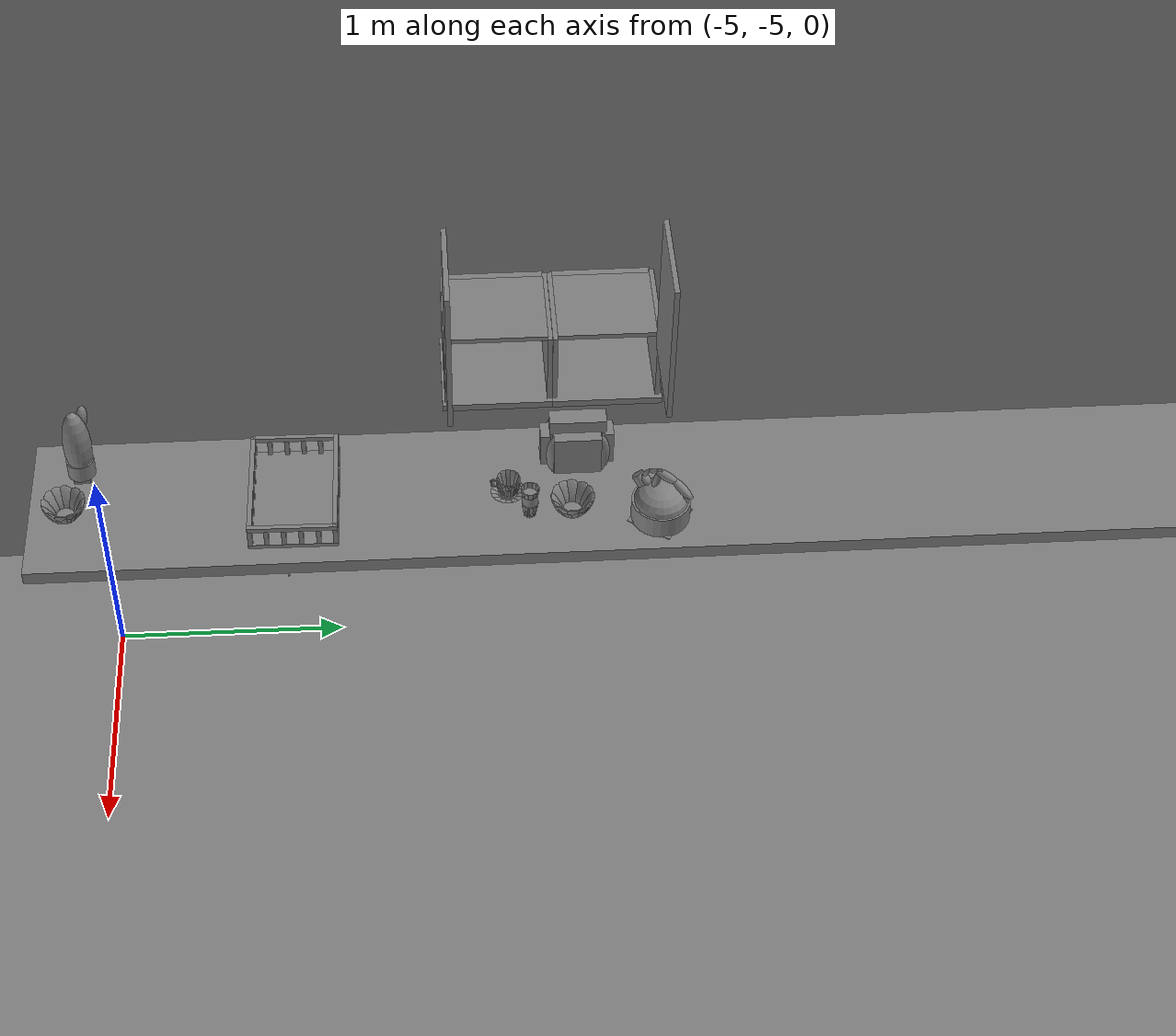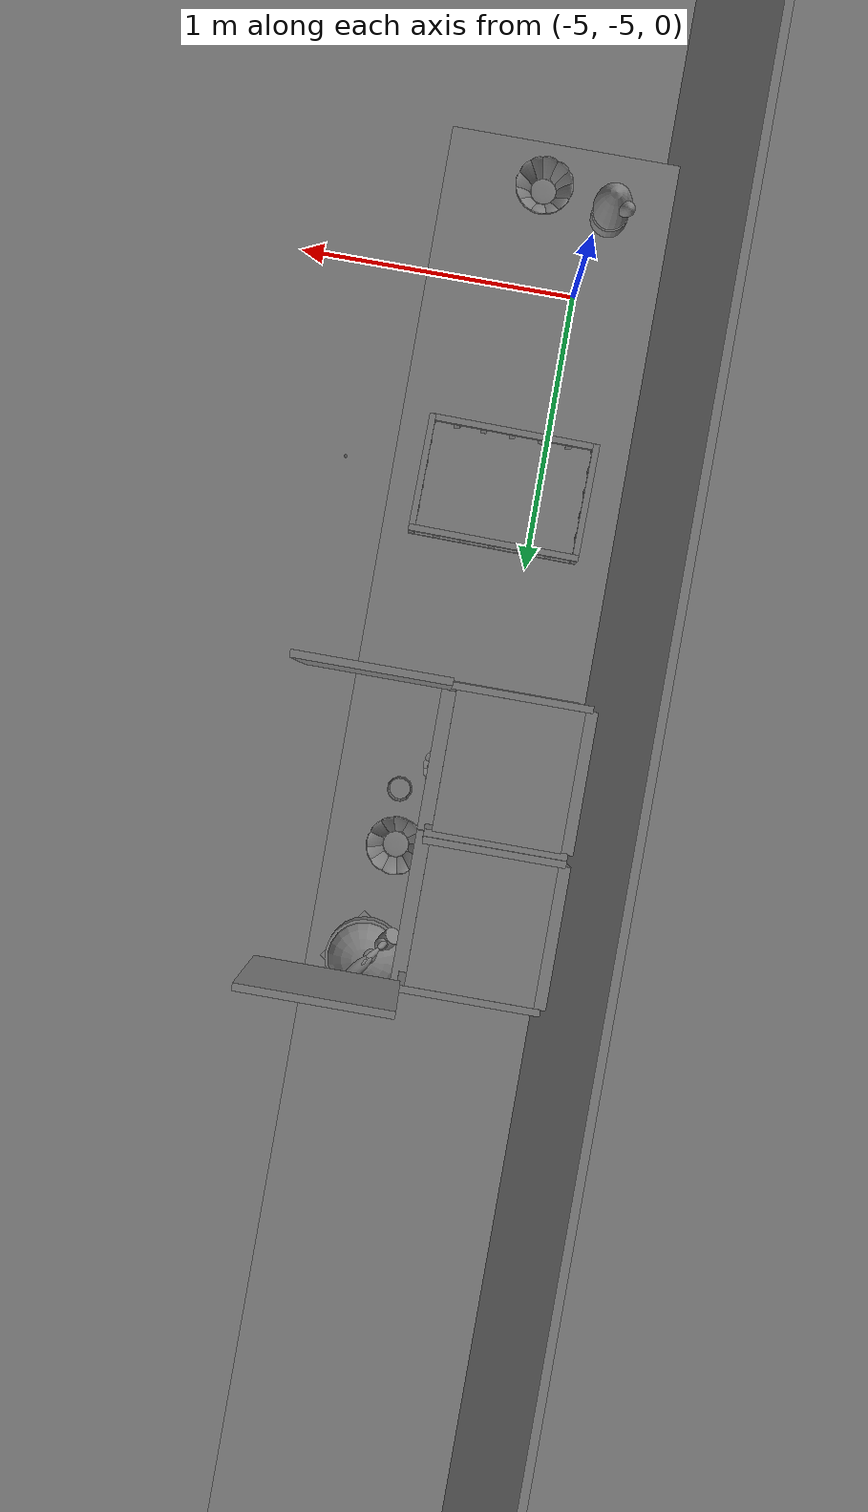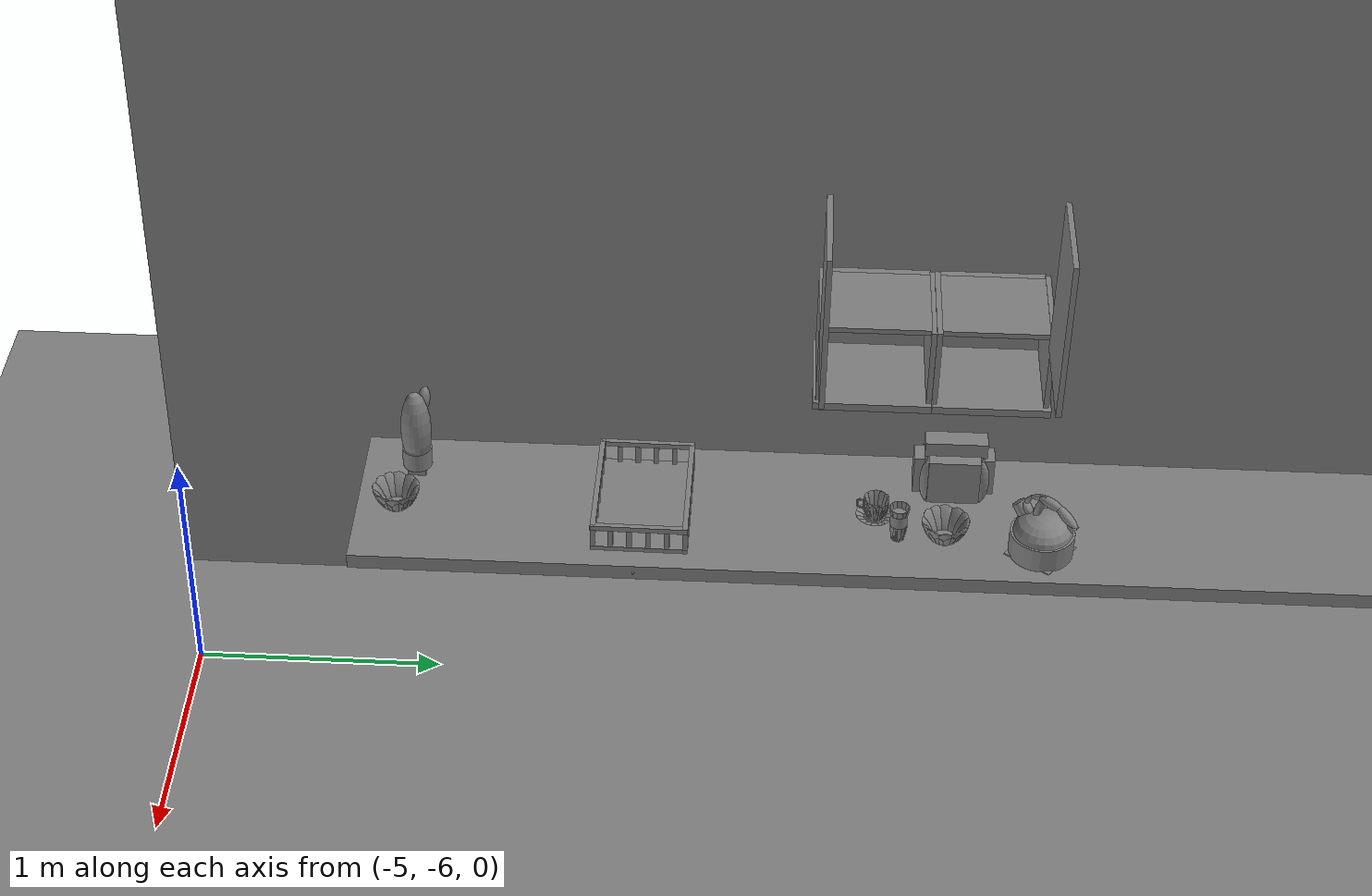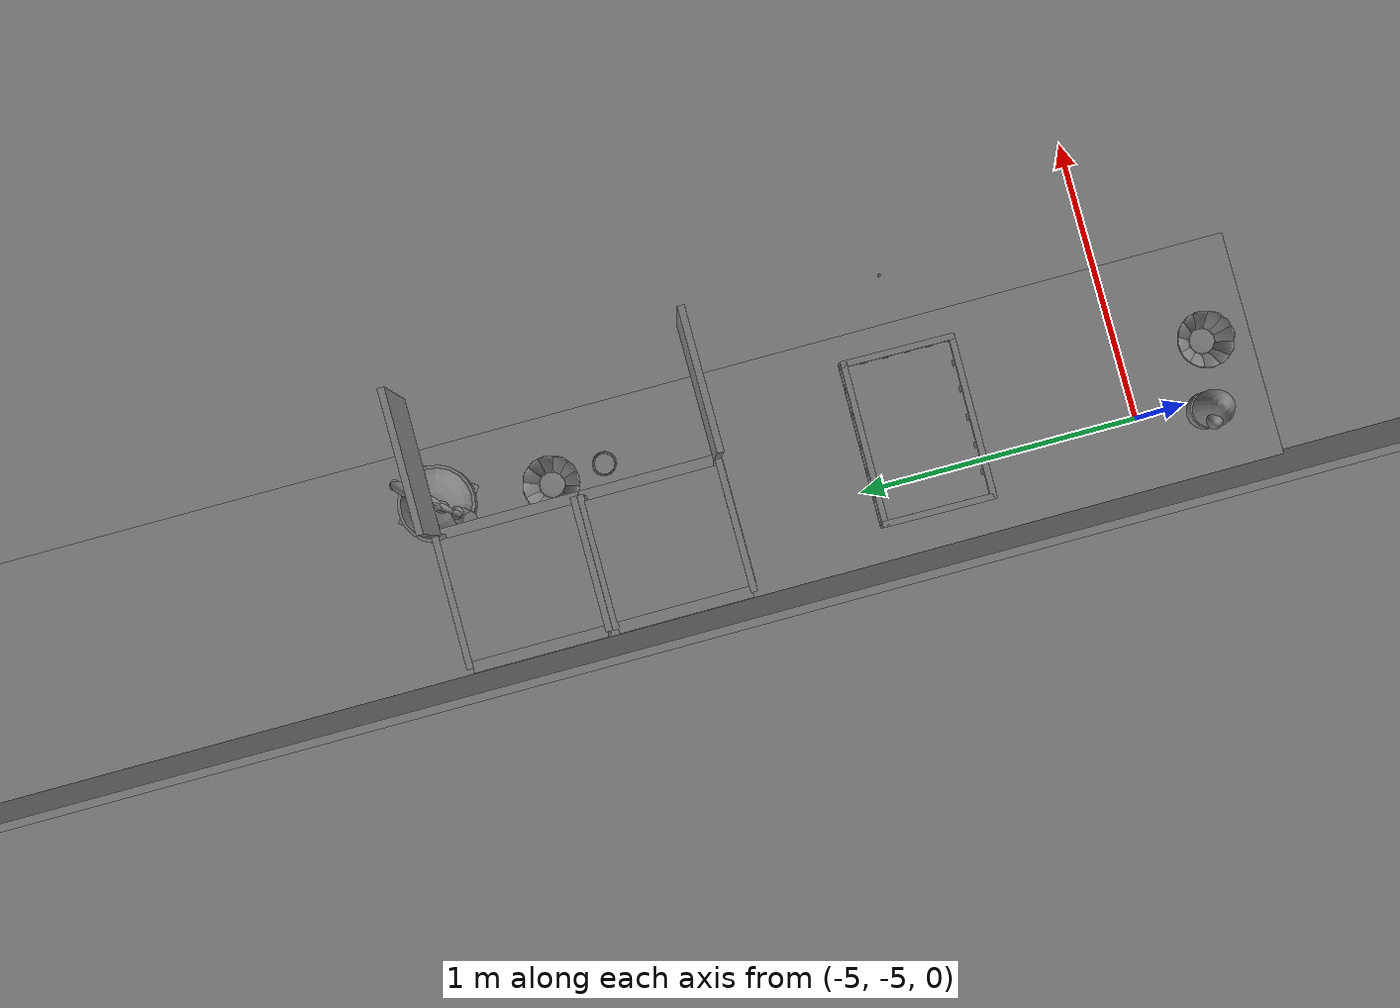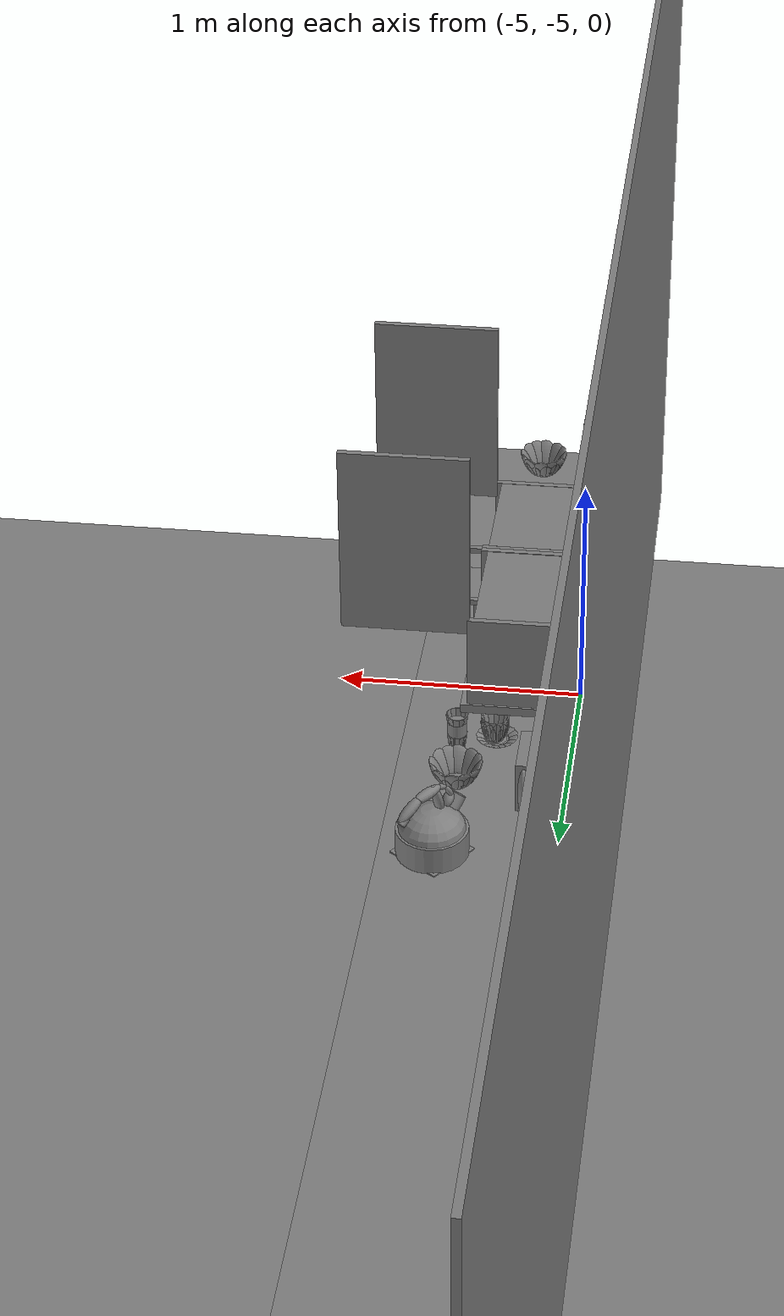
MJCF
<mujoco>
    <option gravity="0.000000000 0.000000000 -9.810000420" timestep="0.0049999999" integrator="implicitfast" density="9.8000002" viscosity="1.8000001e-05" noslip_iterations="10" iterations="100" sdf_iterations="50">
        <flag multiccd="disable"/>
    </option>
    <size memory="1000M"/>
    <compiler coordinate="local"/>
    <worldbody>
        <light cutoff="30" pos="0 1 1" dir="0 -1 -2"/>
        <light cutoff="30" pos="0 -1 1" dir="0 1 -2"/>
        <body pos="0.000000000 0.000000000 0.000000000" euler="0.000000000 0.000000000 0.000000000" name="Static Objcets_Static Objcets">
            <geom contype="1" conaffinity="1" density="1000" type="box" material="" rgba="0.500000000 0.500000000 0.500000000 1.000000000" solimp="0.899999976 0.949999988 0.001000000" friction="1.000000000 0.005000000 0.000100000" solref="0.020000000 1.000000000" margin="0" condim="3" group="0" pos="-4.999745846 -3.087441683 1.763863802" quat="0.707107067 0.707106471 0.000000000 0.000000000" size="0.200000003 0.159999996 0.010000000" name="Static Objcets_geom_169C72E7_15BD_471B_BCB0_6035BAB68BE2"/>
            <geom contype="1" conaffinity="1" density="1000" type="box" material="" rgba="0.500000000 0.500000000 0.500000000 1.000000000" solimp="0.899999976 0.949999988 0.001000000" friction="1.000000000 0.005000000 0.000100000" solref="0.020000000 1.000000000" margin="0" condim="3" group="0" pos="-5.189302921 -3.293644905 1.760152459" quat="0.707107067 0.707106471 0.000000000 0.000000000" size="0.025000000 0.159999996 0.200000003" name="Static Objcets_geom_9CD8E296_316E_4B05_A355_B5493FDEA1F1"/>
            <geom contype="1" conaffinity="1" density="1000" type="box" material="" rgba="0.500000000 0.500000000 0.500000000 1.000000000" solimp="0.899999976 0.949999988 0.001000000" friction="1.000000000 0.005000000 0.000100000" solref="0.020000000 1.000000000" margin="0" condim="3" group="0" pos="-4.979488373 -3.297635794 1.591412544" quat="0.707106829 0.707106709 0.000000000 0.000000000" size="0.200000003 0.015000000 0.219999999" name="Static Objcets_geom_5DC38761_B87A_45CF_829F_8028237B32DD"/>
            <geom contype="1" conaffinity="1" density="1000" type="box" material="" rgba="0.500000000 0.500000000 0.500000000 1.000000000" solimp="0.899999976 0.949999988 0.001000000" friction="1.000000000 0.005000000 0.000100000" solref="0.020000000 1.000000000" margin="0" condim="3" group="0" pos="-4.999745846 -3.497932911 1.764780521" quat="0.707107067 0.707106471 0.000000000 0.000000000" size="0.200000003 0.159999996 0.010000000" name="Static Objcets_geom_574DA9F4_7573_48C5_A95F_B3B58B405D58"/>
            <geom contype="1" conaffinity="1" density="1000" type="box" material="" rgba="0.500000000 0.500000000 0.500000000 1.000000000" solimp="0.899999976 0.949999988 0.001000000" friction="1.000000000 0.005000000 0.000100000" solref="0.020000000 1.000000000" margin="0" condim="3" group="0" pos="-5.000125408 -3.294431210 1.913951039" quat="0.707107067 0.707106471 0.000000000 0.000000000" size="0.180000007 0.010000000 0.200000003" name="Static Objcets_geom_FAA9A526_9F89_4ACA_9928_CA4821580D58"/>
            <geom contype="1" conaffinity="1" density="1000" type="box" material="" rgba="0.500000000 0.500000000 0.500000000 1.000000000" solimp="0.899999976 0.949999988 0.001000000" friction="1.000000000 0.005000000 0.000100000" solref="0.020000000 1.000000000" margin="0" condim="3" group="0" pos="-4.999745846 -3.066934109 1.765979409" quat="0.707107067 0.707106471 0.000000000 0.000000000" size="0.200000003 0.159999996 0.010000000" name="Static Objcets_geom_BE7369D1_95B2_426B_BA42_1232D39E16A1"/>
            <geom contype="1" conaffinity="1" density="1000" type="box" material="" rgba="0.500000000 0.500000000 0.500000000 1.000000000" solimp="0.899999976 0.949999988 0.001000000" friction="1.000000000 0.005000000 0.000100000" solref="0.020000000 1.000000000" margin="0" condim="3" group="0" pos="-5.189302921 -2.861564636 1.760152102" quat="0.707107067 0.707106471 0.000000000 0.000000000" size="0.025000000 0.159999996 0.200000003" name="Static Objcets_geom_070CB292_DAF0_498D_AA50_03D667E1F59F"/>
            <geom contype="1" conaffinity="1" density="1000" type="box" material="" rgba="0.500000000 0.500000000 0.500000000 1.000000000" solimp="0.899999976 0.949999988 0.001000000" friction="1.000000000 0.005000000 0.000100000" solref="0.020000000 1.000000000" margin="0" condim="3" group="0" pos="-5.000125408 -2.861802340 1.913950682" quat="0.707107067 0.707106471 0.000000000 0.000000000" size="0.180000007 0.010000000 0.200000003" name="Static Objcets_geom_B211F159_6C20_41EF_8CC7_501D8F4CCB21"/>
            <geom contype="1" conaffinity="1" density="1000" type="box" material="" rgba="0.500000000 0.500000000 0.500000000 1.000000000" solimp="0.899999976 0.949999988 0.001000000" friction="1.000000000 0.005000000 0.000100000" solref="0.020000000 1.000000000" margin="0" condim="3" group="0" pos="-4.979488373 -2.855390549 1.591412187" quat="0.707106709 0.707106769 0.000000000 0.000000000" size="0.200000003 0.015000000 0.219999999" name="Static Objcets_geom_9E29A637_DDFB_4E31_9BA0_631454E033DB"/>
            <geom contype="1" conaffinity="1" density="1000" type="box" material="" rgba="0.500000000 0.500000000 0.500000000 1.000000000" solimp="0.899999976 0.949999988 0.001000000" friction="1.000000000 0.005000000 0.000100000" solref="0.020000000 1.000000000" margin="0" condim="3" group="0" pos="-4.999745846 -2.653569937 1.764779806" quat="0.707107067 0.707106471 0.000000000 0.000000000" size="0.200000003 0.159999996 0.010000000" name="Static Objcets_geom_E4A3836D_DEA1_4AA9_9557_12902AD71E16"/>
            <geom contype="1" conaffinity="1" density="1000" type="box" material="" rgba="0.500000000 0.500000000 0.500000000 1.000000000" solimp="0.899999976 0.949999988 0.001000000" friction="1.000000000 0.005000000 0.000100000" solref="0.020000000 1.000000000" margin="0" condim="3" group="0" pos="-0.720102787 0.222944975 -1.102830648" quat="0.000000954 1.000000000 0.000000000 0.000000000" size="8.000000000 8.000000000 0.010000000" name="Static Objcets_geom_4E7A83A5_679C_43B1_AC9A_4E5EF40C49FC"/>
            <geom contype="1" conaffinity="1" density="1000" type="box" material="" rgba="0.500000000 0.500000000 0.500000000 1.000000000" solimp="0.899999976 0.949999988 0.001000000" friction="1.000000000 0.005000000 0.000100000" solref="0.020000000 1.000000000" margin="0" condim="3" group="0" pos="-4.873187065 -2.461376429 0.977675021" quat="0.707107067 0.707106471 0.000000000 0.000000000" size="0.370000005 0.029999999 2.799999952" name="Static Objcets_geom_BF1E2800_870C_4189_B744_46900C5692AF"/>
            <geom contype="1" conaffinity="1" density="1000" type="box" material="" rgba="0.500000000 0.500000000 0.500000000 1.000000000" solimp="0.899999976 0.949999988 0.001000000" friction="1.000000000 0.005000000 0.000100000" solref="0.020000000 1.000000000" margin="0" condim="3" group="0" pos="-5.244853973 -2.375543594 1.820221663" quat="0.707107008 0.707106531 0.000000000 0.000000000" size="0.010000000 1.500000000 3.700000048" name="Static Objcets_geom_D219A876_AE69_44C2_90A9_2C7A34F38FFE"/>
        </body>
        <body pos="-4.166503429 -3.863975286 1.876050472" euler="49.652725220 12.717161179 86.015518188" mocap="true" name="spotlight3_SpotLight"/>
        <body pos="1000.000000000 1000.000000000 1.000000000" euler="0.000000000 0.000000000 0.000000000" name="openloong_gripper_2f85_fix_base_usda_jar_01">
            <geom contype="1" conaffinity="1" density="1000" type="box" material="" rgba="0.500000000 0.500000000 0.500000000 1.000000000" solimp="0.899999976 0.949999988 0.001000000" friction="1.000000000 0.005000000 0.000100000" solref="0.020000000 1.000000000" margin="0" condim="3" group="0" pos="0.000000000 0.000000000 0.006158113" quat="1.000000000 0.000000000 0.000000000 0.000000000" size="0.020000000 0.020000000 0.005000000" name="openloong_gripper_2f85_fix_base_usda_geom_EC9A505D_2C2A_43A2_9F2E_37FE04F5C867"/>
            <geom contype="1" conaffinity="1" density="1000" type="cylinder" material="" rgba="0.500000000 0.500000000 0.500000000 1.000000000" solimp="0.899999976 0.949999988 0.001000000" friction="1.000000000 0.005000000 0.000100000" solref="0.020000000 1.000000000" margin="0" condim="3" group="0" pos="0.000000000 0.000000000 0.062744498" quat="1.000000000 0.000000000 0.000000000 0.000000000" size="0.041000001 0.052999999 1.000000000" name="openloong_gripper_2f85_fix_base_usda_geom_93CEC2E4_F27E_4194_83C2_082E218F87E4"/>
            <geom contype="1" conaffinity="1" density="1000" type="ellipsoid" material="" rgba="0.500000000 0.500000000 0.500000000 1.000000000" solimp="0.899999976 0.949999988 0.001000000" friction="1.000000000 0.005000000 0.000100000" solref="0.020000000 1.000000000" margin="0" condim="3" group="0" pos="0.000000000 0.000000000 0.122252703" quat="1.000000000 0.000000000 0.000000000 0.000000000" size="0.035999998 0.035999998 0.010000000" name="openloong_gripper_2f85_fix_base_usda_geom_1A5066F4_9B0C_48E4_BDC9_DF07D1E71706"/>
            <geom contype="1" conaffinity="1" density="1000" type="cylinder" material="" rgba="0.500000000 0.500000000 0.500000000 1.000000000" solimp="0.899999976 0.949999988 0.001000000" friction="1.000000000 0.005000000 0.000100000" solref="0.020000000 1.000000000" margin="0" condim="3" group="0" pos="0.000000000 0.000000000 0.015747190" quat="1.000000000 0.000000000 0.000000000 0.000000000" size="0.035000000 0.010000000 1.000000000" name="openloong_gripper_2f85_fix_base_usda_geom_7E04E6EE_370E_499C_8317_B2FF30001E84"/>
            <geom contype="1" conaffinity="1" density="1000" type="ellipsoid" material="" rgba="0.500000000 0.500000000 0.500000000 1.000000000" solimp="0.899999976 0.949999988 0.001000000" friction="1.000000000 0.005000000 0.000100000" solref="0.020000000 1.000000000" margin="0" condim="3" group="0" pos="0.000000000 0.000000000 0.115815401" quat="1.000000000 0.000000000 0.000000000 0.000000000" size="0.039999999 0.039999999 0.010000000" name="openloong_gripper_2f85_fix_base_usda_geom_606CC68B_55E3_4E3D_B63F_140FA226A96F"/>
            <geom contype="1" conaffinity="1" density="1000" type="cylinder" material="" rgba="0.500000000 0.500000000 0.500000000 1.000000000" solimp="0.899999976 0.949999988 0.001000000" friction="1.000000000 0.005000000 0.000100000" solref="0.020000000 1.000000000" margin="0" condim="3" group="0" pos="0.000000000 0.000000000 0.133183479" quat="1.000000000 0.000000000 0.000000000 0.000000000" size="0.037999999 0.006500000 1.000000000" name="openloong_gripper_2f85_fix_base_usda_geom_0C898C9B_2900_4314_87A0_79402AA7590A"/>
            <freejoint name="openloong_gripper_2f85_fix_base_usda_jar_01_joint"/>
            <site size="0.005000000 0.005000000 0.005000000" rgba="0.500000000 0.500000000 0.500000000 1.000000000" pos="0.000000000 0.000000000 0.000000000" quat="1.000000000 0.000000000 0.000000000 0.000000000" group="0" type="sphere" name="openloong_gripper_2f85_fix_base_usda_jar_01site"/>
        </body>
        <body pos="1000.000000000 1000.000000000 1.000000000" euler="0.000000000 0.000000000 0.000000000" name="openloong_gripper_2f85_fix_base_usda_salt">
            <geom contype="1" conaffinity="1" density="1000" type="box" material="" rgba="0.500000000 0.500000000 0.500000000 1.000000000" solimp="0.899999976 0.949999988 0.001000000" friction="1.000000000 0.005000000 0.000100000" solref="0.020000000 1.000000000" margin="0" condim="3" group="0" pos="0.000305176 0.000000000 0.084862232" quat="1.000000000 0.000000000 0.000000000 0.000000000" size="0.048999999 0.018999999 0.005000000" name="openloong_gripper_2f85_fix_base_usda_geom_F10473A7_46D4_4D1A_8D1C_5B6A637A9A7B"/>
            <geom contype="1" conaffinity="1" density="1000" type="box" material="" rgba="0.500000000 0.500000000 0.500000000 1.000000000" solimp="0.899999976 0.949999988 0.001000000" friction="1.000000000 0.005000000 0.000100000" solref="0.020000000 1.000000000" margin="0" condim="3" group="0" pos="0.000305176 0.000000000 0.104564309" quat="1.000000000 0.000000000 0.000000000 0.000000000" size="0.052000001 0.014000000 0.005000000" name="openloong_gripper_2f85_fix_base_usda_geom_A6576661_04FD_4044_BEAE_ECCA2676DDAB"/>
            <geom contype="1" conaffinity="1" density="1000" type="box" material="" rgba="0.500000000 0.500000000 0.500000000 1.000000000" solimp="0.899999976 0.949999988 0.001000000" friction="1.000000000 0.005000000 0.000100000" solref="0.020000000 1.000000000" margin="0" condim="3" group="0" pos="0.000305176 0.000000000 0.114487171" quat="1.000000000 0.000000000 0.000000000 0.000000000" size="0.054000001 0.011500000 0.005000000" name="openloong_gripper_2f85_fix_base_usda_geom_50B8E8EE_1A14_4A8C_9DB5_F941059DB8DA"/>
            <geom contype="1" conaffinity="1" density="1000" type="box" material="" rgba="0.500000000 0.500000000 0.500000000 1.000000000" solimp="0.899999976 0.949999988 0.001000000" friction="1.000000000 0.005000000 0.000100000" solref="0.020000000 1.000000000" margin="0" condim="3" group="0" pos="0.000305176 0.000000000 0.075103164" quat="1.000000000 0.000000000 0.000000000 0.000000000" size="0.048000000 0.020000000 0.005000000" name="openloong_gripper_2f85_fix_base_usda_geom_9127960F_C638_4139_A7FF_ACA49699C875"/>
            <geom contype="1" conaffinity="1" density="1000" type="box" material="" rgba="0.500000000 0.500000000 0.500000000 1.000000000" solimp="0.899999976 0.949999988 0.001000000" friction="1.000000000 0.005000000 0.000100000" solref="0.020000000 1.000000000" margin="0" condim="3" group="0" pos="0.000305176 0.000000000 0.134892464" quat="1.000000000 0.000000000 0.000000000 0.000000000" size="0.057000000 0.007000000 0.005000000" name="openloong_gripper_2f85_fix_base_usda_geom_C6AC1177_8139_434A_906C_A980F83FDCA2"/>
            <geom contype="1" conaffinity="1" density="1000" type="box" material="" rgba="0.500000000 0.500000000 0.500000000 1.000000000" solimp="0.899999976 0.949999988 0.001000000" friction="1.000000000 0.005000000 0.000100000" solref="0.020000000 1.000000000" margin="0" condim="3" group="0" pos="0.000305176 0.000000000 0.094920278" quat="1.000000000 0.000000000 0.000000000 0.000000000" size="0.050000001 0.017000001 0.005000000" name="openloong_gripper_2f85_fix_base_usda_geom_622B7BE3_44A2_48CA_95B9_A8A4FDF2A101"/>
            <geom contype="1" conaffinity="1" density="1000" type="box" material="" rgba="0.500000000 0.500000000 0.500000000 1.000000000" solimp="0.899999976 0.949999988 0.001000000" friction="1.000000000 0.005000000 0.000100000" solref="0.020000000 1.000000000" margin="0" condim="3" group="0" pos="0.000305176 0.000000000 0.065204859" quat="1.000000000 0.000000000 0.000000000 0.000000000" size="0.045000002 0.021000000 0.005000000" name="openloong_gripper_2f85_fix_base_usda_geom_F27241AE_C454_400F_B598_2DA1FD0D49EA"/>
            <geom contype="1" conaffinity="1" density="1000" type="box" material="" rgba="0.500000000 0.500000000 0.500000000 1.000000000" solimp="0.899999976 0.949999988 0.001000000" friction="1.000000000 0.005000000 0.000100000" solref="0.020000000 1.000000000" margin="0" condim="3" group="0" pos="0.000305176 0.000000000 0.144135714" quat="1.000000000 0.000000000 0.000000000 0.000000000" size="0.059000000 0.005000000 0.004000000" name="openloong_gripper_2f85_fix_base_usda_geom_A2DE3C71_068B_4914_A56A_9B88410BDCAB"/>
            <geom contype="1" conaffinity="1" density="1000" type="box" material="" rgba="0.500000000 0.500000000 0.500000000 1.000000000" solimp="0.899999976 0.949999988 0.001000000" friction="1.000000000 0.005000000 0.000100000" solref="0.020000000 1.000000000" margin="0" condim="3" group="0" pos="0.000000000 0.000000000 0.031593561" quat="1.000000000 0.000000000 0.000000000 0.000000000" size="0.041999999 0.024000000 0.029999999" name="openloong_gripper_2f85_fix_base_usda_geom_BDE14BCE_18E8_429E_A41C_A5035E4020A8"/>
            <geom contype="1" conaffinity="1" density="1000" type="box" material="" rgba="0.500000000 0.500000000 0.500000000 1.000000000" solimp="0.899999976 0.949999988 0.001000000" friction="1.000000000 0.005000000 0.000100000" solref="0.020000000 1.000000000" margin="0" condim="3" group="0" pos="0.000305176 0.000000000 0.124608755" quat="1.000000000 0.000000000 0.000000000 0.000000000" size="0.055000000 0.008000000 0.005000000" name="openloong_gripper_2f85_fix_base_usda_geom_307FBF3D_CCDE_4F92_B983_742D60D3269F"/>
            <freejoint name="openloong_gripper_2f85_fix_base_usda_salt_joint"/>
            <site size="0.005000000 0.005000000 0.005000000" rgba="0.500000000 0.500000000 0.500000000 1.000000000" pos="0.000000000 0.000000000 0.000000000" quat="1.000000000 0.000000000 0.000000000 0.000000000" group="0" type="sphere" name="openloong_gripper_2f85_fix_base_usda_saltsite"/>
        </body>
        <body pos="1000.000000000 1000.000000000 1.000000000" euler="0.000000000 0.000000000 0.000000000" name="openloong_gripper_2f85_fix_base_usda_bow_yellow_kps">
            <geom contype="1" conaffinity="1" density="1000" type="ellipsoid" material="" rgba="0.500000000 0.500000000 0.500000000 1.000000000" solimp="0.899999976 0.949999988 0.001000000" friction="1.000000000 0.005000000 0.000100000" solref="0.020000000 1.000000000" margin="0" condim="3" group="0" pos="-0.052185059 0.040283203 0.044118762" quat="0.919264615 -0.076883033 -0.225593656 -0.313287765" size="0.010000000 0.039999999 0.052000001" name="openloong_gripper_2f85_fix_base_usda_geom_E02DC4F7_19D5_4201_8B59_CAF953362C03"/>
            <geom contype="1" conaffinity="1" density="1000" type="ellipsoid" material="" rgba="0.500000000 0.500000000 0.500000000 1.000000000" solimp="0.899999976 0.949999988 0.001000000" friction="1.000000000 0.005000000 0.000100000" solref="0.020000000 1.000000000" margin="0" condim="3" group="0" pos="-0.000061035 0.065979004 0.044118762" quat="0.687598765 -0.168314874 -0.168741167 -0.685860336" size="0.010000000 0.039999999 0.052000001" name="openloong_gripper_2f85_fix_base_usda_geom_AC41466D_A85E_4889_921D_544FE1408B78"/>
            <geom contype="1" conaffinity="1" density="1000" type="box" material="" rgba="0.500000000 0.500000000 0.500000000 1.000000000" solimp="0.899999976 0.949999988 0.001000000" friction="1.000000000 0.005000000 0.000100000" solref="0.020000000 1.000000000" margin="0" condim="3" group="0" pos="0.000061035 0.000000000 -0.002001643" quat="1.000000000 0.000000000 0.000000000 0.000000000" size="0.029999999 0.029999999 0.002000000" name="openloong_gripper_2f85_fix_base_usda_geom_85FBA765_4C79_48D0_B33A_9C616FFA7DA9"/>
            <geom contype="1" conaffinity="1" density="1000" type="ellipsoid" material="" rgba="0.500000000 0.500000000 0.500000000 1.000000000" solimp="0.899999976 0.949999988 0.001000000" friction="1.000000000 0.005000000 0.000100000" solref="0.020000000 1.000000000" margin="0" condim="3" group="0" pos="0.029418945 -0.059082031 0.044118762" quat="0.825555861 0.125530601 0.202597082 -0.511521280" size="0.010000000 0.039999999 0.052000001" name="openloong_gripper_2f85_fix_base_usda_geom_7DB37E2D_CD0A_416F_AA58_318E9F3444C5"/>
            <geom contype="1" conaffinity="1" density="1000" type="ellipsoid" material="" rgba="0.500000000 0.500000000 0.500000000 1.000000000" solimp="0.899999976 0.949999988 0.001000000" friction="1.000000000 0.005000000 0.000100000" solref="0.020000000 1.000000000" margin="0" condim="3" group="0" pos="0.000244141 -0.065979004 0.044118762" quat="0.687598765 0.168314651 0.168741375 -0.685860336" size="0.010000000 0.039999999 0.052000001" name="openloong_gripper_2f85_fix_base_usda_geom_5D01D43C_84A5_4299_AD4B_15CCB6EC0BC9"/>
            <geom contype="1" conaffinity="1" density="1000" type="ellipsoid" material="" rgba="0.500000000 0.500000000 0.500000000 1.000000000" solimp="0.899999976 0.949999988 0.001000000" friction="1.000000000 0.005000000 0.000100000" solref="0.020000000 1.000000000" margin="0" condim="3" group="0" pos="0.000061035 0.000000000 0.000446677" quat="1.000000000 0.000000000 0.000000000 0.000000000" size="0.039999999 0.039999999 0.002000000" name="openloong_gripper_2f85_fix_base_usda_geom_EEFE425C_D779_4725_A215_EAAE1451859C"/>
            <geom contype="1" conaffinity="1" density="1000" type="ellipsoid" material="" rgba="0.500000000 0.500000000 0.500000000 1.000000000" solimp="0.899999976 0.949999988 0.001000000" friction="1.000000000 0.005000000 0.000100000" solref="0.020000000 1.000000000" margin="0" condim="3" group="0" pos="0.059082031 0.029541016 0.044118762" quat="0.223252773 -0.231952220 -0.054787423 -0.945174456" size="0.010000000 0.039999999 0.052000001" name="openloong_gripper_2f85_fix_base_usda_geom_F35AD1A5_15E3_4B7F_99E7_4F558D7FC90A"/>
            <geom contype="1" conaffinity="1" density="1000" type="ellipsoid" material="" rgba="0.500000000 0.500000000 0.500000000 1.000000000" solimp="0.899999976 0.949999988 0.001000000" friction="1.000000000 0.005000000 0.000100000" solref="0.020000000 1.000000000" margin="0" condim="3" group="0" pos="0.000061035 0.000000000 0.007335305" quat="1.000000000 0.000000000 0.000000000 0.000000000" size="0.039999999 0.039999999 0.002000000" name="openloong_gripper_2f85_fix_base_usda_geom_8317731A_7CF9_423B_80BC_0D60CD643D1E"/>
            <geom contype="1" conaffinity="1" density="1000" type="ellipsoid" material="" rgba="0.500000000 0.500000000 0.500000000 1.000000000" solimp="0.899999976 0.949999988 0.001000000" friction="1.000000000 0.005000000 0.000100000" solref="0.020000000 1.000000000" margin="0" condim="3" group="0" pos="-0.029296875 0.059082031 0.044118762" quat="0.825555861 -0.125530809 -0.202596918 -0.511521280" size="0.010000000 0.039999999 0.052000001" name="openloong_gripper_2f85_fix_base_usda_geom_AB3E534F_CFB0_4DBD_B095_893D9ADE957F"/>
            <geom contype="1" conaffinity="1" density="1000" type="ellipsoid" material="" rgba="0.500000000 0.500000000 0.500000000 1.000000000" solimp="0.899999976 0.949999988 0.001000000" friction="1.000000000 0.005000000 0.000100000" solref="0.020000000 1.000000000" margin="0" condim="3" group="0" pos="0.040222168 0.052368164 0.044118762" quat="0.429593176 -0.213750049 -0.105424821 -0.871002972" size="0.010000000 0.039999999 0.052000001" name="openloong_gripper_2f85_fix_base_usda_geom_65A5ACA3_D3F1_4CD3_BB35_0014913F4882"/>
            <geom contype="1" conaffinity="1" density="1000" type="ellipsoid" material="" rgba="0.500000000 0.500000000 0.500000000 1.000000000" solimp="0.899999976 0.949999988 0.001000000" friction="1.000000000 0.005000000 0.000100000" solref="0.020000000 1.000000000" margin="0" condim="3" group="0" pos="0.066040039 0.000000000 0.044118762" quat="0.971183062 -0.000000156 0.238334835 0.000000030" size="0.010000000 0.039999999 0.052000001" name="openloong_gripper_2f85_fix_base_usda_geom_86321C0A_1AC2_40E7_BCF1_8BF3AE6BAAB7"/>
            <geom contype="1" conaffinity="1" density="1000" type="ellipsoid" material="" rgba="0.500000000 0.500000000 0.500000000 1.000000000" solimp="0.899999976 0.949999988 0.001000000" friction="1.000000000 0.005000000 0.000100000" solref="0.020000000 1.000000000" margin="0" condim="3" group="0" pos="0.052307129 -0.040283203 0.044118762" quat="0.919264674 0.076882750 0.225593731 -0.313287705" size="0.010000000 0.039999999 0.052000001" name="openloong_gripper_2f85_fix_base_usda_geom_117D175A_DFE2_41AF_9EB3_FDC78D4877E9"/>
            <geom contype="1" conaffinity="1" density="1000" type="ellipsoid" material="" rgba="0.500000000 0.500000000 0.500000000 1.000000000" solimp="0.899999976 0.949999988 0.001000000" friction="1.000000000 0.005000000 0.000100000" solref="0.020000000 1.000000000" margin="0" condim="3" group="0" pos="-0.065917969 0.000000000 0.044118762" quat="0.971183062 -0.000000142 -0.238334835 0.000000030" size="0.010000000 0.039999999 0.052000001" name="openloong_gripper_2f85_fix_base_usda_geom_F58EB2E0_CCA7_4133_B7CF_A9E1B7E645AD"/>
            <geom contype="1" conaffinity="1" density="1000" type="ellipsoid" material="" rgba="0.500000000 0.500000000 0.500000000 1.000000000" solimp="0.899999976 0.949999988 0.001000000" friction="1.000000000 0.005000000 0.000100000" solref="0.020000000 1.000000000" margin="0" condim="3" group="0" pos="-0.058898926 -0.029541016 0.044118762" quat="0.223252758 0.231952101 0.054787733 -0.945174575" size="0.010000000 0.039999999 0.052000001" name="openloong_gripper_2f85_fix_base_usda_geom_9EC27D62_ADA7_4D84_80FB_7FCFE76B6A80"/>
            <geom contype="1" conaffinity="1" density="1000" type="ellipsoid" material="" rgba="0.500000000 0.500000000 0.500000000 1.000000000" solimp="0.899999976 0.949999988 0.001000000" friction="1.000000000 0.005000000 0.000100000" solref="0.020000000 1.000000000" margin="0" condim="3" group="0" pos="-0.040100098 -0.052368164 0.044118762" quat="0.429593235 0.213749886 0.105425082 -0.871003032" size="0.010000000 0.039999999 0.052000001" name="openloong_gripper_2f85_fix_base_usda_geom_90098A3E_51DB_44A6_9063_4EB374BE2051"/>
            <freejoint name="openloong_gripper_2f85_fix_base_usda_bow_yellow_kps_joint"/>
            <site size="0.005000000 0.005000000 0.005000000" rgba="0.500000000 0.500000000 0.500000000 1.000000000" pos="0.000000000 0.000000000 0.000000000" quat="0.999961913 0.008726534 0.000000000 0.000000000" group="0" type="sphere" name="openloong_gripper_2f85_fix_base_usda_bow_yellow_kps"/>
        </body>
        <body pos="-4.300420761 -4.434488773 1.831205368" euler="128.035873413 33.222476959 -155.904647827" mocap="true" name="spotlight6_SpotLight"/>
        <body pos="1000.000000000 1000.000000000 1.000000000" euler="0.000000000 0.000000000 0.000000000" name="openloong_gripper_2f85_fix_base_usda_coffeecup_white_kps">
            <geom contype="1" conaffinity="1" density="1000" type="capsule" material="" rgba="0.500000000 0.500000000 0.500000000 1.000000000" solimp="0.899999976 0.949999988 0.001000000" friction="1.000000000 0.005000000 0.000100000" solref="0.020000000 1.000000000" margin="0" condim="3" group="0" pos="-0.000854492 -0.065795898 0.050029993" quat="0.343559504 -0.613204718 0.626912475 0.336047262" size="0.004000000 0.005000000 1.000000000" name="openloong_gripper_2f85_fix_base_usda_geom_3CF1DD22_31E1_48C4_898E_71136DA70DE0"/>
            <geom contype="1" conaffinity="1" density="1000" type="ellipsoid" material="" rgba="0.500000000 0.500000000 0.500000000 1.000000000" solimp="0.899999976 0.949999988 0.001000000" friction="1.000000000 0.005000000 0.000100000" solref="0.020000000 1.000000000" margin="0" condim="3" group="0" pos="-0.000793457 -0.038452148 0.048040152" quat="0.711656272 0.066323131 -0.067805752 0.696095467" size="0.005000000 0.029999999 0.048999999" name="openloong_gripper_2f85_fix_base_usda_geom_E0796B73_D492_4D16_8C95_61E50BFCF023"/>
            <geom contype="1" conaffinity="1" density="1000" type="ellipsoid" material="" rgba="0.500000000 0.500000000 0.500000000 1.000000000" solimp="0.899999976 0.949999988 0.001000000" friction="1.000000000 0.005000000 0.000100000" solref="0.020000000 1.000000000" margin="0" condim="3" group="0" pos="0.037719727 -0.001892090 0.048040152" quat="0.995387912 0.001371633 0.094835162 -0.014391154" size="0.005000000 0.029999999 0.048999999" name="openloong_gripper_2f85_fix_base_usda_geom_A32B5439_30A7_47B6_AF0A_8BA865800FFB"/>
            <geom contype="1" conaffinity="1" density="1000" type="ellipsoid" material="" rgba="0.500000000 0.500000000 0.500000000 1.000000000" solimp="0.899999976 0.949999988 0.001000000" friction="1.000000000 0.005000000 0.000100000" solref="0.020000000 1.000000000" margin="0" condim="3" group="0" pos="0.033996582 0.015502930 0.048040152" quat="0.970659733 -0.021051638 0.092478797 0.220962167" size="0.005000000 0.029999999 0.048999999" name="openloong_gripper_2f85_fix_base_usda_geom_B9EB5AA7_08D4_48E1_8A52_398A39F46D81"/>
            <geom contype="1" conaffinity="1" density="1000" type="box" material="" rgba="0.500000000 0.500000000 0.500000000 1.000000000" solimp="0.899999976 0.949999988 0.001000000" friction="1.000000000 0.005000000 0.000100000" solref="0.020000000 1.000000000" margin="0" condim="3" group="0" pos="0.000793457 -0.000183105 0.000156164" quat="0.714879215 0.000000000 0.000000000 0.699247897" size="0.020000000 0.020000000 0.002000000" name="openloong_gripper_2f85_fix_base_usda_geom_D0E01041_D07B_4918_94F3_61A1A73F5147"/>
            <geom contype="1" conaffinity="1" density="1000" type="ellipsoid" material="" rgba="0.500000000 0.500000000 0.500000000 1.000000000" solimp="0.899999976 0.949999988 0.001000000" friction="1.000000000 0.005000000 0.000100000" solref="0.020000000 1.000000000" margin="0" condim="3" group="0" pos="-0.019409180 -0.033081055 0.048040152" quat="0.866879702 0.046630561 -0.082595348 0.489411235" size="0.005000000 0.029999999 0.048999999" name="openloong_gripper_2f85_fix_base_usda_geom_1DC98578_F5C0_4E7B_9767_7D809C694F53"/>
            <geom contype="1" conaffinity="1" density="1000" type="ellipsoid" material="" rgba="0.500000000 0.500000000 0.500000000 1.000000000" solimp="0.899999976 0.949999988 0.001000000" friction="1.000000000 0.005000000 0.000100000" solref="0.020000000 1.000000000" margin="0" condim="3" group="0" pos="-0.016052246 0.033264160 0.048040152" quat="0.840792537 -0.050782297 -0.080109790 -0.532983541" size="0.005000000 0.029999999 0.048999999" name="openloong_gripper_2f85_fix_base_usda_geom_A4B0778F_10AC_400E_9937_1F4BD7719C51"/>
            <geom contype="1" conaffinity="1" density="1000" type="capsule" material="" rgba="0.500000000 0.500000000 0.500000000 1.000000000" solimp="0.899999976 0.949999988 0.001000000" friction="1.000000000 0.005000000 0.000100000" solref="0.020000000 1.000000000" margin="0" condim="3" group="0" pos="-0.000549316 -0.053527832 0.046825886" quat="0.505496025 -0.494442940 0.505495846 0.494442940" size="0.004000000 0.005000000 1.000000000" name="openloong_gripper_2f85_fix_base_usda_geom_01A6D9E7_0449_49B3_8CEA_479DBC675206"/>
            <geom contype="1" conaffinity="1" density="1000" type="ellipsoid" material="" rgba="0.500000000 0.500000000 0.500000000 1.000000000" solimp="0.899999976 0.949999988 0.001000000" friction="1.000000000 0.005000000 0.000100000" solref="0.020000000 1.000000000" margin="0" condim="3" group="0" pos="-0.032104492 0.018920898 0.048040152" quat="0.958129764 -0.025742561 -0.091288343 -0.270168930" size="0.005000000 0.029999999 0.048999999" name="openloong_gripper_2f85_fix_base_usda_geom_122B95AF_D1B6_4D39_949A_5A67C13A2F81"/>
            <geom contype="1" conaffinity="1" density="1000" type="ellipsoid" material="" rgba="0.500000000 0.500000000 0.500000000 1.000000000" solimp="0.899999976 0.949999988 0.001000000" friction="1.000000000 0.005000000 0.000100000" solref="0.020000000 1.000000000" margin="0" condim="3" group="0" pos="-0.037597656 0.000305176 0.048040152" quat="0.995387554 -0.001371440 -0.094839431 -0.014389008" size="0.005000000 0.029999999 0.048999999" name="openloong_gripper_2f85_fix_base_usda_geom_A75DF9BA_E8F8_49B9_94B8_0368A380EA53"/>
            <geom contype="1" conaffinity="1" density="1000" type="capsule" material="" rgba="0.500000000 0.500000000 0.500000000 1.000000000" solimp="0.899999976 0.949999988 0.001000000" friction="1.000000000 0.005000000 0.000100000" solref="0.020000000 1.000000000" margin="0" condim="3" group="0" pos="-0.000366211 -0.043762207 0.044118762" quat="0.260488123 -0.651174724 0.665731549 0.254792154" size="0.004000000 0.003000000 1.000000000" name="openloong_gripper_2f85_fix_base_usda_geom_6F6BCCC2_B3C5_4274_B6BE_705BF6903C1E"/>
            <geom contype="1" conaffinity="1" density="1000" type="capsule" material="" rgba="0.500000000 0.500000000 0.500000000 1.000000000" solimp="0.899999976 0.949999988 0.001000000" friction="1.000000000 0.005000000 0.000100000" solref="0.020000000 1.000000000" margin="0" condim="3" group="0" pos="-0.000915527 -0.068542480 0.082936406" quat="0.624995589 -0.339446366 0.347034454 0.611329615" size="0.004000000 0.004000000 1.000000000" name="openloong_gripper_2f85_fix_base_usda_geom_90489A80_100B_4D56_AA82_E2BCB5A1A746"/>
            <geom contype="1" conaffinity="1" density="1000" type="ellipsoid" material="" rgba="0.500000000 0.500000000 0.500000000 1.000000000" solimp="0.899999976 0.949999988 0.001000000" friction="1.000000000 0.005000000 0.000100000" solref="0.020000000 1.000000000" margin="0" condim="3" group="0" pos="0.016113281 -0.034851074 0.048040152" quat="0.840793252 0.050779939 0.080106191 -0.532983422" size="0.005000000 0.029999999 0.048999999" name="openloong_gripper_2f85_fix_base_usda_geom_3FDB6320_7E98_4F5C_8606_FA34E1A3DE6B"/>
            <geom contype="1" conaffinity="1" density="1000" type="ellipsoid" material="" rgba="0.500000000 0.500000000 0.500000000 1.000000000" solimp="0.899999976 0.949999988 0.001000000" friction="1.000000000 0.005000000 0.000100000" solref="0.020000000 1.000000000" margin="0" condim="3" group="0" pos="0.000854492 0.036865234 0.048040152" quat="0.711656570 -0.066320375 0.067802906 0.696095705" size="0.005000000 0.029999999 0.048999999" name="openloong_gripper_2f85_fix_base_usda_geom_39D2CF09_BFB2_460C_B5AB_471BB3EAABC4"/>
            <geom contype="1" conaffinity="1" density="1000" type="ellipsoid" material="" rgba="0.500000000 0.500000000 0.500000000 1.000000000" solimp="0.899999976 0.949999988 0.001000000" friction="1.000000000 0.005000000 0.000100000" solref="0.020000000 1.000000000" margin="0" condim="3" group="0" pos="-0.033935547 -0.017089844 0.048040152" quat="0.970659137 0.021052625 -0.092483103 0.220962465" size="0.005000000 0.029999999 0.048999999" name="openloong_gripper_2f85_fix_base_usda_geom_A191B56E_3C73_4565_96D2_D415955B7A4D"/>
            <geom contype="1" conaffinity="1" density="1000" type="ellipsoid" material="" rgba="0.500000000 0.500000000 0.500000000 1.000000000" solimp="0.899999976 0.949999988 0.001000000" friction="1.000000000 0.005000000 0.000100000" solref="0.020000000 1.000000000" margin="0" condim="3" group="0" pos="0.019531250 0.031494141 0.048040152" quat="0.866880119 -0.046628602 0.082591817 0.489411235" size="0.005000000 0.029999999 0.048999999" name="openloong_gripper_2f85_fix_base_usda_geom_AB292DAE_D799_468B_B588_00A0C6B2AF0D"/>
            <geom contype="1" conaffinity="1" density="1000" type="ellipsoid" material="" rgba="0.500000000 0.500000000 0.500000000 1.000000000" solimp="0.899999976 0.949999988 0.001000000" friction="1.000000000 0.005000000 0.000100000" solref="0.020000000 1.000000000" margin="0" condim="3" group="0" pos="0.032165527 -0.020507812 0.048040152" quat="0.958128154 0.025740955 0.091285400 -0.270175666" size="0.005000000 0.029999999 0.048999999" name="openloong_gripper_2f85_fix_base_usda_geom_39F1C1B2_2229_4A48_B464_B0AE95A53AF9"/>
            <geom contype="1" conaffinity="1" density="1000" type="capsule" material="" rgba="0.500000000 0.500000000 0.500000000 1.000000000" solimp="0.899999976 0.949999988 0.001000000" friction="1.000000000 0.005000000 0.000100000" solref="0.020000000 1.000000000" margin="0" condim="3" group="0" pos="-0.000610352 -0.056823730 0.083572865" quat="0.452654332 -0.541215360 0.553313971 0.442756712" size="0.004000000 0.009000000 1.000000000" name="openloong_gripper_2f85_fix_base_usda_geom_DE12C710_40A7_46C8_AE6A_0EB1BEC209FD"/>
            <geom contype="1" conaffinity="1" density="1000" type="ellipsoid" material="" rgba="0.500000000 0.500000000 0.500000000 1.000000000" solimp="0.899999976 0.949999988 0.001000000" friction="1.000000000 0.005000000 0.000100000" solref="0.020000000 1.000000000" margin="0" condim="3" group="0" pos="0.000061035 -0.000183105 0.001848221" quat="0.714879215 0.000000000 0.000000000 0.699247897" size="0.029999999 0.029999999 0.001000000" name="openloong_gripper_2f85_fix_base_usda_geom_3BF0ADD5_0B7E_42AD_8D28_90033596B963"/>
            <geom contype="1" conaffinity="1" density="1000" type="capsule" material="" rgba="0.500000000 0.500000000 0.500000000 1.000000000" solimp="0.899999976 0.949999988 0.001000000" friction="1.000000000 0.005000000 0.000100000" solref="0.020000000 1.000000000" margin="0" condim="3" group="0" pos="-0.000976562 -0.071838379 0.066101432" quat="0.031849027 -0.698553741 0.714169443 0.031152546" size="0.004000000 0.012000000 1.000000000" name="openloong_gripper_2f85_fix_base_usda_geom_FD47F2E1_D53D_46F4_A7C3_86CC4AED88C9"/>
            <freejoint name="openloong_gripper_2f85_fix_base_usda_coffeecup_white_kps_joint"/>
            <site size="0.005000000 0.005000000 0.005000000" rgba="0.500000000 0.500000000 0.500000000 1.000000000" pos="0.000000000 0.000000000 0.000000000" quat="0.999961913 0.008726534 0.000000000 0.000000000" group="0" type="sphere" name="openloong_gripper_2f85_fix_base_usda_coffeecup_white_kps"/>
        </body>
        <body pos="-4.016051769 -3.922484875 1.723455429" euler="-142.959533691 68.369834900 91.963294983" mocap="true" name="spotlight4_SpotLight"/>
        <body pos="1000.000000000 1000.000000000 1.000000000" euler="0.000000000 0.000000000 0.000000000" name="openloong_gripper_2f85_fix_base_usda_bottle_red">
            <geom contype="1" conaffinity="1" density="1000" type="ellipsoid" material="" rgba="0.500000000 0.500000000 0.500000000 1.000000000" solimp="0.899999976 0.949999988 0.001000000" friction="1.000000000 0.005000000 0.000100000" solref="0.020000000 1.000000000" margin="0" condim="3" group="0" pos="0.000000000 0.000000000 0.144284487" quat="1.000000000 0.000000000 0.000000000 0.000000000" size="0.021000000 0.021000000 0.079999998" name="openloong_gripper_2f85_fix_base_usda_geom_A97A4AA1_25E2_47AE_8CBE_97524F573198"/>
            <geom contype="1" conaffinity="1" density="1000" type="cylinder" material="" rgba="0.500000000 0.500000000 0.500000000 1.000000000" solimp="0.899999976 0.949999988 0.001000000" friction="1.000000000 0.005000000 0.000100000" solref="0.020000000 1.000000000" margin="0" condim="3" group="0" pos="0.000000000 0.000000000 0.220618963" quat="1.000000000 0.000000000 0.000000000 0.000000000" size="0.016000001 0.010000000 1.000000000" name="openloong_gripper_2f85_fix_base_usda_geom_AAE984E7_347F_42EE_AE76_05D03A6DAB76"/>
            <geom contype="1" conaffinity="1" density="1000" type="ellipsoid" material="" rgba="0.500000000 0.500000000 0.500000000 1.000000000" solimp="0.899999976 0.949999988 0.001000000" friction="1.000000000 0.005000000 0.000100000" solref="0.020000000 1.000000000" margin="0" condim="3" group="0" pos="0.000000000 0.000000000 0.118945479" quat="1.000000000 0.000000000 0.000000000 0.000000000" size="0.030999999 0.030999999 0.029999999" name="openloong_gripper_2f85_fix_base_usda_geom_82AAAFC7_6FD3_4227_8C79_464F90CCE03A"/>
            <geom contype="1" conaffinity="1" density="1000" type="box" material="" rgba="0.500000000 0.500000000 0.500000000 1.000000000" solimp="0.899999976 0.949999988 0.001000000" friction="1.000000000 0.005000000 0.000100000" solref="0.020000000 1.000000000" margin="0" condim="3" group="0" pos="0.000000000 0.000000000 0.002189159" quat="1.000000000 0.000000000 0.000000000 0.000000000" size="0.020000000 0.020000000 0.003000000" name="openloong_gripper_2f85_fix_base_usda_geom_40768FE8_6B65_4D8F_AD9E_6933A3B9D95B"/>
            <geom contype="1" conaffinity="1" density="1000" type="cylinder" material="" rgba="0.500000000 0.500000000 0.500000000 1.000000000" solimp="0.899999976 0.949999988 0.001000000" friction="1.000000000 0.005000000 0.000100000" solref="0.020000000 1.000000000" margin="0" condim="3" group="0" pos="0.000000000 -0.000366211 0.060884237" quat="1.000000000 0.000000000 0.000000000 0.000000000" size="0.030999999 0.057999998 1.000000000" name="openloong_gripper_2f85_fix_base_usda_geom_C2A8AA04_28DC_48AD_BC99_ACA888D3F01A"/>
            <freejoint name="openloong_gripper_2f85_fix_base_usda_bottle_red_joint"/>
            <site size="0.005000000 0.005000000 0.005000000" rgba="0.500000000 0.500000000 0.500000000 1.000000000" pos="0.000000000 0.000000000 0.000000000" quat="0.999961913 0.008726535 0.000000000 0.000000000" group="0" type="sphere" name="openloong_gripper_2f85_fix_base_usda_bottle_redsite"/>
        </body>
        <body pos="-4.860558510 -4.149443150 1.004824519" euler="0.000000000 0.000000000 -90.691101074" name="openloong_gripper_2f85_fix_base_usda_Basket_Kitchen_01">
            <geom contype="1" conaffinity="1" density="1000" type="box" material="" rgba="0.500000000 0.500000000 0.500000000 1.000000000" solimp="0.899999976 0.949999988 0.001000000" friction="1.000000000 0.005000000 0.000100000" solref="0.020000000 1.000000000" margin="0" condim="3" group="0" pos="-0.175679624 -0.000001907 0.109079957" quat="0.707106948 0.000000000 0.000000000 0.707106292" size="0.268999994 0.010000000 0.010500000" name="openloong_gripper_2f85_fix_base_usda_geom_56866F57_917C_46E4_BE44_F7C717BB76B1"/>
            <geom contype="1" conaffinity="1" density="1000" type="box" material="" rgba="0.500000000 0.500000000 0.500000000 1.000000000" solimp="0.899999976 0.949999988 0.001000000" friction="1.000000000 0.005000000 0.000100000" solref="0.020000000 1.000000000" margin="0" condim="3" group="0" pos="-0.176020086 0.002991676 0.059861541" quat="0.707106948 0.000000000 0.000000000 0.707106292" size="0.009500000 0.009500000 0.039999999" name="openloong_gripper_2f85_fix_base_usda_geom_4329AC00_B413_4924_AE7C_4C07183ECD8A"/>
            <geom contype="1" conaffinity="1" density="1000" type="box" material="" rgba="0.500000000 0.500000000 0.500000000 1.000000000" solimp="0.899999976 0.949999988 0.001000000" friction="1.000000000 0.005000000 0.000100000" solref="0.020000000 1.000000000" margin="0" condim="3" group="0" pos="0.176000476 0.002991199 0.059860587" quat="0.707106948 0.000000000 0.000000000 0.707106292" size="0.009500000 0.009500000 0.039999999" name="openloong_gripper_2f85_fix_base_usda_geom_7CE5D035_3A28_4C29_9405_5CF4D76EC000"/>
            <geom contype="1" conaffinity="1" density="1000" type="box" material="" rgba="0.500000000 0.500000000 0.500000000 1.000000000" solimp="0.899999976 0.949999988 0.001000000" friction="1.000000000 0.005000000 0.000100000" solref="0.020000000 1.000000000" margin="0" condim="3" group="0" pos="0.176003337 0.259475470 0.059859991" quat="0.707106948 0.000000000 0.000000000 0.707106292" size="0.009500000 0.009500000 0.039999999" name="openloong_gripper_2f85_fix_base_usda_geom_63FA69AA_F55F_4586_8803_87E61271AF67"/>
            <geom contype="1" conaffinity="1" density="1000" type="box" material="" rgba="0.500000000 0.500000000 0.500000000 1.000000000" solimp="0.899999976 0.949999988 0.001000000" friction="1.000000000 0.005000000 0.000100000" solref="0.020000000 1.000000000" margin="0" condim="3" group="0" pos="-0.176020086 -0.088696003 0.059861422" quat="0.707106948 0.000000000 0.000000000 0.707106292" size="0.009500000 0.009500000 0.039999999" name="openloong_gripper_2f85_fix_base_usda_geom_25510DF9_37EC_4976_9FA1_5D9CD7E58A29"/>
            <geom contype="1" conaffinity="1" density="1000" type="box" material="" rgba="0.500000000 0.500000000 0.500000000 1.000000000" solimp="0.899999976 0.949999988 0.001000000" friction="1.000000000 0.005000000 0.000100000" solref="0.020000000 1.000000000" margin="0" condim="3" group="0" pos="0.000000000 0.259647608 0.109079957" quat="0.707106948 0.000000000 0.000000000 0.707106292" size="0.010000000 0.185000002 0.010500000" name="openloong_gripper_2f85_fix_base_usda_geom_C2A28FDE_00DE_4D63_8DB0_45760D5C1BD9"/>
            <geom contype="1" conaffinity="1" density="1000" type="box" material="" rgba="0.500000000 0.500000000 0.500000000 1.000000000" solimp="0.899999976 0.949999988 0.001000000" friction="1.000000000 0.005000000 0.000100000" solref="0.020000000 1.000000000" margin="0" condim="3" group="0" pos="0.176001906 -0.259545803 0.059860349" quat="0.707106948 0.000000000 0.000000000 0.707106292" size="0.009500000 0.009500000 0.039999999" name="openloong_gripper_2f85_fix_base_usda_geom_7BB1D4D9_5943_437F_8279_F80B9FFDEF72"/>
            <geom contype="1" conaffinity="1" density="1000" type="box" material="" rgba="0.500000000 0.500000000 0.500000000 1.000000000" solimp="0.899999976 0.949999988 0.001000000" friction="1.000000000 0.005000000 0.000100000" solref="0.020000000 1.000000000" margin="0" condim="3" group="0" pos="0.036305428 -0.259545326 0.059860587" quat="0.707106948 0.000000000 0.000000000 0.707106292" size="0.009500000 0.009500000 0.039999999" name="openloong_gripper_2f85_fix_base_usda_geom_DCE94316_908F_4BC0_8B9C_48ADB49B81C9"/>
            <geom contype="1" conaffinity="1" density="1000" type="box" material="" rgba="0.500000000 0.500000000 0.500000000 1.000000000" solimp="0.899999976 0.949999988 0.001000000" friction="1.000000000 0.005000000 0.000100000" solref="0.020000000 1.000000000" margin="0" condim="3" group="0" pos="0.000000119 -0.259647369 0.109079957" quat="0.707106948 0.000000000 0.000000000 0.707106292" size="0.010000000 0.185000002 0.010500000" name="openloong_gripper_2f85_fix_base_usda_geom_34B09900_C5DE_4924_8B3A_454F48782F60"/>
            <geom contype="1" conaffinity="1" density="1000" type="box" material="" rgba="0.500000000 0.500000000 0.500000000 1.000000000" solimp="0.899999976 0.949999988 0.001000000" friction="1.000000000 0.005000000 0.000100000" solref="0.020000000 1.000000000" margin="0" condim="3" group="0" pos="-0.034950614 -0.259546280 0.059860826" quat="0.707106948 0.000000000 0.000000000 0.707106292" size="0.009500000 0.009500000 0.039999999" name="openloong_gripper_2f85_fix_base_usda_geom_A2937257_7D4B_46D4_A843_F264732A76E4"/>
            <geom contype="1" conaffinity="1" density="1000" type="box" material="" rgba="0.500000000 0.500000000 0.500000000 1.000000000" solimp="0.899999976 0.949999988 0.001000000" friction="1.000000000 0.005000000 0.000100000" solref="0.020000000 1.000000000" margin="0" condim="3" group="0" pos="0.108178139 0.259475708 0.059860229" quat="0.707106948 0.000000000 0.000000000 0.707106292" size="0.009500000 0.009500000 0.039999999" name="openloong_gripper_2f85_fix_base_usda_geom_AC5AE36E_FBE3_4272_BCD7_B2790EFB5C3E"/>
            <geom contype="1" conaffinity="1" density="1000" type="box" material="" rgba="0.500000000 0.500000000 0.500000000 1.000000000" solimp="0.899999976 0.949999988 0.001000000" friction="1.000000000 0.005000000 0.000100000" solref="0.020000000 1.000000000" margin="0" condim="3" group="0" pos="-0.106845737 0.259474993 0.059860826" quat="0.707106948 0.000000000 0.000000000 0.707106292" size="0.009500000 0.009500000 0.039999999" name="openloong_gripper_2f85_fix_base_usda_geom_57503CBA_8423_4327_A13A_E4A69726E2CC"/>
            <geom contype="1" conaffinity="1" density="1000" type="box" material="" rgba="0.500000000 0.500000000 0.500000000 1.000000000" solimp="0.899999976 0.949999988 0.001000000" friction="1.000000000 0.005000000 0.000100000" solref="0.020000000 1.000000000" margin="0" condim="3" group="0" pos="-0.176020563 0.179505825 0.059861779" quat="0.707106948 0.000000000 0.000000000 0.707106292" size="0.009500000 0.009500000 0.039999999" name="openloong_gripper_2f85_fix_base_usda_geom_4941A9F9_8B9D_4A99_AB83_C1E4CA3437A3"/>
            <geom contype="1" conaffinity="1" density="1000" type="box" material="" rgba="0.500000000 0.500000000 0.500000000 1.000000000" solimp="0.899999976 0.949999988 0.001000000" friction="1.000000000 0.005000000 0.000100000" solref="0.020000000 1.000000000" margin="0" condim="3" group="0" pos="-0.034949303 0.259475708 0.059860587" quat="0.707106948 0.000000000 0.000000000 0.707106292" size="0.009500000 0.009500000 0.039999999" name="openloong_gripper_2f85_fix_base_usda_geom_98F29B9D_E7C6_498C_8A73_8E5432ABE800"/>
            <geom contype="1" conaffinity="1" density="1000" type="box" material="" rgba="0.500000000 0.500000000 0.500000000 1.000000000" solimp="0.899999976 0.949999988 0.001000000" friction="1.000000000 0.005000000 0.000100000" solref="0.020000000 1.000000000" margin="0" condim="3" group="0" pos="0.175792098 -0.000002384 0.109079838" quat="0.707106948 0.000000000 0.000000000 0.707106292" size="0.268999994 0.010000000 0.010500000" name="openloong_gripper_2f85_fix_base_usda_geom_011EC2C6_2A22_430F_A4A6_F9EB79EF0C3D"/>
            <geom contype="1" conaffinity="1" density="1000" type="box" material="" rgba="0.500000000 0.500000000 0.500000000 1.000000000" solimp="0.899999976 0.949999988 0.001000000" friction="1.000000000 0.005000000 0.000100000" solref="0.020000000 1.000000000" margin="0" condim="3" group="0" pos="-0.000015259 0.000000000 0.010667920" quat="0.707106948 0.000000000 0.000000000 0.707106292" size="0.268999994 0.186000004 0.010500000" name="openloong_gripper_2f85_fix_base_usda_geom_AED0229C_B1F5_4D2C_8E44_F13EAC17A548"/>
            <geom contype="1" conaffinity="1" density="1000" type="box" material="" rgba="0.500000000 0.500000000 0.500000000 1.000000000" solimp="0.899999976 0.949999988 0.001000000" friction="1.000000000 0.005000000 0.000100000" solref="0.020000000 1.000000000" margin="0" condim="3" group="0" pos="-0.176020026 0.094224930 0.059861660" quat="0.707106948 0.000000000 0.000000000 0.707106292" size="0.009500000 0.009500000 0.039999999" name="openloong_gripper_2f85_fix_base_usda_geom_368B8A8D_7014_4955_B686_0EDAC08363BA"/>
            <geom contype="1" conaffinity="1" density="1000" type="box" material="" rgba="0.500000000 0.500000000 0.500000000 1.000000000" solimp="0.899999976 0.949999988 0.001000000" friction="1.000000000 0.005000000 0.000100000" solref="0.020000000 1.000000000" margin="0" condim="3" group="0" pos="0.108177185 -0.259545326 0.059860349" quat="0.707106948 0.000000000 0.000000000 0.707106292" size="0.009500000 0.009500000 0.039999999" name="openloong_gripper_2f85_fix_base_usda_geom_85852708_239B_46D8_A873_B8587D36B96C"/>
            <geom contype="1" conaffinity="1" density="1000" type="box" material="" rgba="0.500000000 0.500000000 0.500000000 1.000000000" solimp="0.899999976 0.949999988 0.001000000" friction="1.000000000 0.005000000 0.000100000" solref="0.020000000 1.000000000" margin="0" condim="3" group="0" pos="-0.176020026 -0.177031994 0.059861183" quat="0.707106948 0.000000000 0.000000000 0.707106292" size="0.009500000 0.009500000 0.039999999" name="openloong_gripper_2f85_fix_base_usda_geom_C693BD78_65F5_4F6A_8C0A_079DE547115B"/>
            <geom contype="1" conaffinity="1" density="1000" type="box" material="" rgba="0.500000000 0.500000000 0.500000000 1.000000000" solimp="0.899999976 0.949999988 0.001000000" friction="1.000000000 0.005000000 0.000100000" solref="0.020000000 1.000000000" margin="0" condim="3" group="0" pos="-0.176020086 -0.259545803 0.059861183" quat="0.707106948 0.000000000 0.000000000 0.707106292" size="0.009500000 0.009500000 0.039999999" name="openloong_gripper_2f85_fix_base_usda_geom_F6337294_7E9F_4E99_B432_D9EB4EF39880"/>
            <geom contype="1" conaffinity="1" density="1000" type="box" material="" rgba="0.500000000 0.500000000 0.500000000 1.000000000" solimp="0.899999976 0.949999988 0.001000000" friction="1.000000000 0.005000000 0.000100000" solref="0.020000000 1.000000000" margin="0" condim="3" group="0" pos="-0.106846333 -0.259545803 0.059861064" quat="0.707106948 0.000000000 0.000000000 0.707106292" size="0.009500000 0.009500000 0.039999999" name="openloong_gripper_2f85_fix_base_usda_geom_977EEEB9_3B2B_4F6A_ACC9_6136CF129CAA"/>
            <geom contype="1" conaffinity="1" density="1000" type="box" material="" rgba="0.500000000 0.500000000 0.500000000 1.000000000" solimp="0.899999976 0.949999988 0.001000000" friction="1.000000000 0.005000000 0.000100000" solref="0.020000000 1.000000000" margin="0" condim="3" group="0" pos="0.176000595 0.094224453 0.059860826" quat="0.707106948 0.000000000 0.000000000 0.707106292" size="0.009500000 0.009500000 0.039999999" name="openloong_gripper_2f85_fix_base_usda_geom_AC478424_59AE_4F09_A37B_AFC0BC390154"/>
            <geom contype="1" conaffinity="1" density="1000" type="box" material="" rgba="0.500000000 0.500000000 0.500000000 1.000000000" solimp="0.899999976 0.949999988 0.001000000" friction="1.000000000 0.005000000 0.000100000" solref="0.020000000 1.000000000" margin="0" condim="3" group="0" pos="0.176001072 -0.088696480 0.059860587" quat="0.707106948 0.000000000 0.000000000 0.707106292" size="0.009500000 0.009500000 0.039999999" name="openloong_gripper_2f85_fix_base_usda_geom_79DCC274_54B1_476C_BC8B_4DE1F6F2E8DC"/>
            <geom contype="1" conaffinity="1" density="1000" type="box" material="" rgba="0.500000000 0.500000000 0.500000000 1.000000000" solimp="0.899999976 0.949999988 0.001000000" friction="1.000000000 0.005000000 0.000100000" solref="0.020000000 1.000000000" margin="0" condim="3" group="0" pos="0.036306858 0.259475946 0.059860349" quat="0.707106948 0.000000000 0.000000000 0.707106292" size="0.009500000 0.009500000 0.039999999" name="openloong_gripper_2f85_fix_base_usda_geom_F528D576_4B8D_449C_BDAA_DD91260870A0"/>
            <geom contype="1" conaffinity="1" density="1000" type="box" material="" rgba="0.500000000 0.500000000 0.500000000 1.000000000" solimp="0.899999976 0.949999988 0.001000000" friction="1.000000000 0.005000000 0.000100000" solref="0.020000000 1.000000000" margin="0" condim="3" group="0" pos="0.176001430 -0.177032471 0.059860349" quat="0.707106948 0.000000000 0.000000000 0.707106292" size="0.009500000 0.009500000 0.039999999" name="openloong_gripper_2f85_fix_base_usda_geom_7EA162A6_4DA8_4171_949E_FC4BC704C0EA"/>
            <geom contype="1" conaffinity="1" density="1000" type="box" material="" rgba="0.500000000 0.500000000 0.500000000 1.000000000" solimp="0.899999976 0.949999988 0.001000000" friction="1.000000000 0.005000000 0.000100000" solref="0.020000000 1.000000000" margin="0" condim="3" group="0" pos="0.175999999 0.179504871 0.059860945" quat="0.707106948 0.000000000 0.000000000 0.707106292" size="0.009500000 0.009500000 0.039999999" name="openloong_gripper_2f85_fix_base_usda_geom_458861BC_9DEF_40C2_8190_5B3CED629EA8"/>
            <geom contype="1" conaffinity="1" density="1000" type="box" material="" rgba="0.500000000 0.500000000 0.500000000 1.000000000" solimp="0.899999976 0.949999988 0.001000000" friction="1.000000000 0.005000000 0.000100000" solref="0.020000000 1.000000000" margin="0" condim="3" group="0" pos="-0.176020026 0.259474516 0.059860945" quat="0.707106948 0.000000000 0.000000000 0.707106292" size="0.009500000 0.009500000 0.039999999" name="openloong_gripper_2f85_fix_base_usda_geom_1E2C68B5_86E6_4F94_8CD1_94E24B132DEB"/>
            <freejoint name="openloong_gripper_2f85_fix_base_usda_Basket_Kitchen_01_joint"/>
        </body>
        <body pos="-4.827295780 -3.287638187 1.074643731" euler="0.000000000 0.000000000 89.999992371" name="Interactive Objcets_coffeecup_01">
            <geom contype="1" conaffinity="1" density="1000" type="ellipsoid" material="" rgba="0.500000000 0.500000000 0.500000000 1.000000000" solimp="0.899999976 0.949999988 0.001000000" friction="1.000000000 0.005000000 0.000100000" solref="0.020000000 1.000000000" margin="0" condim="3" group="0" pos="0.068445444 0.017385960 0.002976775" quat="0.228377223 -0.092319682 -0.021759447 -0.968941331" size="0.005000000 0.029999999 0.048999999" name="Interactive Objcets_geom_E5ADDAFE_B8BE_44C4_A6B0_BBFB39CE249F"/>
            <geom contype="1" conaffinity="1" density="1000" type="capsule" material="" rgba="0.500000000 0.500000000 0.500000000 1.000000000" solimp="0.899999976 0.949999988 0.001000000" friction="1.000000000 0.005000000 0.000100000" solref="0.020000000 1.000000000" margin="0" condim="3" group="0" pos="-0.008219719 0.000000000 -0.000944734" quat="0.364379913 0.000000063 0.931250274 -0.000000063" size="0.004000000 0.003000000 1.000000000" name="Interactive Objcets_geom_382048B1_49D2_4290_96AB_A142AA138C68"/>
            <geom contype="1" conaffinity="1" density="1000" type="ellipsoid" material="" rgba="0.500000000 0.500000000 0.500000000 1.000000000" solimp="0.899999976 0.949999988 0.001000000" friction="1.000000000 0.005000000 0.000100000" solref="0.020000000 1.000000000" margin="0" condim="3" group="0" pos="0.001010895 -0.016271591 0.002976775" quat="0.228377163 0.092315644 0.021758538 -0.968941689" size="0.005000000 0.029999999 0.048999999" name="Interactive Objcets_geom_9BE2C44E_DD4F_4320_8B1C_DB3A4324B2D8"/>
            <geom contype="1" conaffinity="1" density="1000" type="ellipsoid" material="" rgba="0.500000000 0.500000000 0.500000000 1.000000000" solimp="0.899999976 0.949999988 0.001000000" friction="1.000000000 0.005000000 0.000100000" solref="0.020000000 1.000000000" margin="0" condim="3" group="0" pos="0.034471050 -0.037125111 0.002976775" quat="0.701517045 0.067293778 0.066836871 -0.706313014" size="0.005000000 0.029999999 0.048999999" name="Interactive Objcets_geom_C0ABBA1C_E2DA_40D8_9977_969DBF9A3EA3"/>
            <geom contype="1" conaffinity="1" density="1000" type="ellipsoid" material="" rgba="0.500000000 0.500000000 0.500000000 1.000000000" solimp="0.899999976 0.949999988 0.001000000" friction="1.000000000 0.005000000 0.000100000" solref="0.020000000 1.000000000" margin="0" condim="3" group="0" pos="0.035336256 0.000558376 -0.045152068" quat="0.999999881 0.000000000 0.000000000 0.000000000" size="0.029999999 0.029999999 0.001000000" name="Interactive Objcets_geom_CE505961_578D_4BFE_B8D0_2FB1022C51B0"/>
            <geom contype="1" conaffinity="1" density="1000" type="capsule" material="" rgba="0.500000000 0.500000000 0.500000000 1.000000000" solimp="0.899999976 0.949999988 0.001000000" friction="1.000000000 0.005000000 0.000100000" solref="0.020000000 1.000000000" margin="0" condim="3" group="0" pos="-0.033022881 0.000000000 0.037873149" quat="0.874267220 0.000000042 0.485444903 -0.000000084" size="0.004000000 0.004000000 1.000000000" name="Interactive Objcets_geom_E95CEA0A_B83F_4DA1_A565_1EEDDC76A3E2"/>
            <geom contype="1" conaffinity="1" density="1000" type="capsule" material="" rgba="0.500000000 0.500000000 0.500000000 1.000000000" solimp="0.899999976 0.949999988 0.001000000" friction="1.000000000 0.005000000 0.000100000" solref="0.020000000 1.000000000" margin="0" condim="3" group="0" pos="-0.018014431 0.000000000 0.001762271" quat="0.707106769 -0.000000004 0.707106709 -0.000000088" size="0.004000000 0.005000000 1.000000000" name="Interactive Objcets_geom_C85B8FAE_B7D2_49A0_8769_358DD16E6DCD"/>
            <geom contype="1" conaffinity="1" density="1000" type="capsule" material="" rgba="0.500000000 0.500000000 0.500000000 1.000000000" solimp="0.899999976 0.949999988 0.001000000" friction="1.000000000 0.005000000 0.000100000" solref="0.020000000 1.000000000" margin="0" condim="3" group="0" pos="-0.021276474 0.000000000 0.038509369" quat="0.633189917 0.000000000 0.773996413 0.000000000" size="0.004000000 0.009000000 1.000000000" name="Interactive Objcets_geom_FEE355B8_0F68_41E2_9817_ED5AA5A6F384"/>
            <geom contype="1" conaffinity="1" density="1000" type="ellipsoid" material="" rgba="0.500000000 0.500000000 0.500000000 1.000000000" solimp="0.899999976 0.949999988 0.001000000" friction="1.000000000 0.005000000 0.000100000" solref="0.020000000 1.000000000" margin="0" condim="3" group="0" pos="0.002039194 0.019308567 0.002976775" quat="0.961933970 -0.024419386 -0.091652036 -0.256293654" size="0.005000000 0.029999999 0.048999999" name="Interactive Objcets_geom_9B4B8FDC_EF99_40AD_8E64_21DC494BA311"/>
            <geom contype="1" conaffinity="1" density="1000" type="ellipsoid" material="" rgba="0.500000000 0.500000000 0.500000000 1.000000000" solimp="0.899999976 0.949999988 0.001000000" friction="1.000000000 0.005000000 0.000100000" solref="0.020000000 1.000000000" margin="0" condim="3" group="0" pos="0.034984604 0.038240910 0.002976775" quat="0.701516926 -0.067296736 -0.066839755 -0.706312656" size="0.005000000 0.029999999 0.048999999" name="Interactive Objcets_geom_71AF25FF_EDAA_4252_8805_29F0300B527D"/>
            <geom contype="1" conaffinity="1" density="1000" type="ellipsoid" material="" rgba="0.500000000 0.500000000 0.500000000 1.000000000" solimp="0.899999976 0.949999988 0.001000000" friction="1.000000000 0.005000000 0.000100000" solref="0.020000000 1.000000000" margin="0" condim="3" group="0" pos="-0.002956629 0.000558376 0.002976775" quat="0.995491505 0.000000004 -0.094849378 -0.000000089" size="0.005000000 0.029999999 0.048999999" name="Interactive Objcets_geom_BAAE29C6_D166_4655_A778_E6245C60E157"/>
            <geom contype="1" conaffinity="1" density="1000" type="ellipsoid" material="" rgba="0.500000000 0.500000000 0.500000000 1.000000000" solimp="0.899999976 0.949999988 0.001000000" friction="1.000000000 0.005000000 0.000100000" solref="0.020000000 1.000000000" margin="0" condim="3" group="0" pos="0.067416430 -0.018191338 0.002976775" quat="0.961934388 0.024418317 0.091648072 -0.256293803" size="0.005000000 0.029999999 0.048999999" name="Interactive Objcets_geom_74F2929C_3D71_417B_B553_0056BD687953"/>
            <geom contype="1" conaffinity="1" density="1000" type="ellipsoid" material="" rgba="0.500000000 0.500000000 0.500000000 1.000000000" solimp="0.899999976 0.949999988 0.001000000" friction="1.000000000 0.005000000 0.000100000" solref="0.020000000 1.000000000" margin="0" condim="3" group="0" pos="0.051787138 -0.033043861 0.002976775" quat="0.848411202 0.049616337 0.080832161 -0.520771146" size="0.005000000 0.029999999 0.048999999" name="Interactive Objcets_geom_61F00237_5CC3_4526_84C2_08BD0167DC7B"/>
            <geom contype="1" conaffinity="1" density="1000" type="ellipsoid" material="" rgba="0.500000000 0.500000000 0.500000000 1.000000000" solimp="0.899999976 0.949999988 0.001000000" friction="1.000000000 0.005000000 0.000100000" solref="0.020000000 1.000000000" margin="0" condim="3" group="0" pos="0.017669693 0.034160614 0.002976775" quat="0.848410904 -0.049618516 -0.080835648 -0.520770907" size="0.005000000 0.029999999 0.048999999" name="Interactive Objcets_geom_AC1D07ED_0CC1_4B8A_83A4_CE946368C648"/>
            <geom contype="1" conaffinity="1" density="1000" type="capsule" material="" rgba="0.500000000 0.500000000 0.500000000 1.000000000" solimp="0.899999976 0.949999988 0.001000000" friction="1.000000000 0.005000000 0.000100000" solref="0.020000000 1.000000000" margin="0" condim="3" group="0" pos="-0.030251026 0.000000000 0.004966617" quat="0.480583906 -0.000000000 0.876948774 -0.000000126" size="0.004000000 0.005000000 1.000000000" name="Interactive Objcets_geom_D83DB2F6_FCF8_4826_889B_022D10D4C873"/>
            <geom contype="1" conaffinity="1" density="1000" type="capsule" material="" rgba="0.500000000 0.500000000 0.500000000 1.000000000" solimp="0.899999976 0.949999988 0.001000000" friction="1.000000000 0.005000000 0.000100000" solref="0.020000000 1.000000000" margin="0" condim="3" group="0" pos="-0.036300898 0.000000000 0.021037936" quat="0.044551343 -0.000000000 0.999007046 -0.000000126" size="0.004000000 0.012000000 1.000000000" name="Interactive Objcets_geom_80BB6B34_E762_4494_A17E_7053140FA9D8"/>
            <geom contype="1" conaffinity="1" density="1000" type="ellipsoid" material="" rgba="0.500000000 0.500000000 0.500000000 1.000000000" solimp="0.899999976 0.949999988 0.001000000" friction="1.000000000 0.005000000 0.000100000" solref="0.020000000 1.000000000" margin="0" condim="3" group="0" pos="0.053700209 0.033117294 0.002976775" quat="0.496025741 -0.082236379 -0.047260769 -0.863111615" size="0.005000000 0.029999999 0.048999999" name="Interactive Objcets_geom_74FC1A12_718F_4EAB_8A89_A37B5D8C3562"/>
            <geom contype="1" conaffinity="1" density="1000" type="ellipsoid" material="" rgba="0.500000000 0.500000000 0.500000000 1.000000000" solimp="0.899999976 0.949999988 0.001000000" friction="1.000000000 0.005000000 0.000100000" solref="0.020000000 1.000000000" margin="0" condim="3" group="0" pos="0.035336256 0.000558376 -0.043215394" quat="0.999999881 0.000000000 0.000000000 0.000000000" size="0.029999999 0.029999999 0.001000000" name="Interactive Objcets_geom_8A0A7BBA_039F_401F_9CE8_2AF0F6DCD0DE"/>
            <geom contype="1" conaffinity="1" density="1000" type="ellipsoid" material="" rgba="0.500000000 0.500000000 0.500000000 1.000000000" solimp="0.899999976 0.949999988 0.001000000" friction="1.000000000 0.005000000 0.000100000" solref="0.020000000 1.000000000" margin="0" condim="3" group="0" pos="0.015755907 -0.032001972 0.002976775" quat="0.496025920 0.082232773 0.047258731 -0.863112032" size="0.005000000 0.029999999 0.048999999" name="Interactive Objcets_geom_041A5F6A_C875_44EA_9C32_2D150F43B600"/>
            <geom contype="1" conaffinity="1" density="1000" type="ellipsoid" material="" rgba="0.500000000 0.500000000 0.500000000 1.000000000" solimp="0.899999976 0.949999988 0.001000000" friction="1.000000000 0.005000000 0.000100000" solref="0.020000000 1.000000000" margin="0" condim="3" group="0" pos="0.072411790 0.000558376 0.002976775" quat="0.995491922 -0.000000019 0.094845265 -0.000000089" size="0.005000000 0.029999999 0.048999999" name="Interactive Objcets_geom_1AEA09FA_1B12_453B_AE52_ED774284C9FE"/>
            <freejoint name="Interactive Objcets_coffeecup_01"/>
        </body>
        <body pos="-4.705342293 -3.169416904 1.103703976" euler="0.000000000 0.000000000 0.000000000" name="Interactive Objcets_cup_02">
            <geom contype="1" conaffinity="1" density="1000" type="box" material="" rgba="0.500000000 0.500000000 0.500000000 1.000000000" solimp="0.899999976 0.949999988 0.001000000" friction="1.000000000 0.005000000 0.000100000" solref="0.020000000 1.000000000" margin="0" condim="3" group="0" pos="-0.034549713 0.000000000 0.062637210" quat="0.704941988 0.055288255 -0.055288251 -0.704942048" size="0.010000000 0.001000000 0.015000000" name="Interactive Objcets_geom_E18E2A9E_73A9_4A14_A0D2_DC6EA932944B"/>
            <geom contype="1" conaffinity="1" density="1000" type="box" material="" rgba="0.500000000 0.500000000 0.500000000 1.000000000" solimp="0.899999976 0.949999988 0.001000000" friction="1.000000000 0.005000000 0.000100000" solref="0.020000000 1.000000000" margin="0" condim="3" group="0" pos="0.022285938 0.016949892 -0.037281752" quat="0.893179297 -0.070051625 0.034732576 -0.442851186" size="0.010000000 0.001000000 0.035000000" name="Interactive Objcets_geom_6F7A3663_8FF0_41FF_8B72_8BA0C549613C"/>
            <geom contype="1" conaffinity="1" density="1000" type="box" material="" rgba="0.500000000 0.500000000 0.500000000 1.000000000" solimp="0.899999976 0.949999988 0.001000000" friction="1.000000000 0.005000000 0.000100000" solref="0.020000000 1.000000000" margin="0" condim="3" group="0" pos="-0.018181324 -0.029377937 0.062637210" quat="0.958910167 0.075206861 -0.021389510 -0.272722572" size="0.010000000 0.001000000 0.015000000" name="Interactive Objcets_geom_43645E94_40B6_495E_A6BC_22F9FD3EAB7D"/>
            <geom contype="1" conaffinity="1" density="1000" type="box" material="" rgba="0.500000000 0.500000000 0.500000000 1.000000000" solimp="0.899999976 0.949999988 0.001000000" friction="1.000000000 0.005000000 0.000100000" solref="0.020000000 1.000000000" margin="0" condim="3" group="0" pos="0.000000000 -0.027877331 -0.037281752" quat="0.996938646 0.078187965 0.000000000 0.000000000" size="0.010000000 0.001000000 0.035000000" name="Interactive Objcets_geom_ED1FA5E4_85E5_43C2_98A9_935C53759486"/>
            <geom contype="1" conaffinity="1" density="1000" type="cylinder" material="" rgba="0.500000000 0.500000000 0.500000000 1.000000000" solimp="0.899999976 0.949999988 0.001000000" friction="1.000000000 0.005000000 0.000100000" solref="0.020000000 1.000000000" margin="0" condim="3" group="0" pos="0.000000000 0.000000000 0.022491097" quat="1.000000000 0.000000030 0.000000000 0.000000000" size="0.033000000 0.025000000 1.000000000" name="Interactive Objcets_geom_6E8EF82E_0733_4F1F_9DA4_576F3D491BB5"/>
            <geom contype="1" conaffinity="1" density="1000" type="box" material="" rgba="0.500000000 0.500000000 0.500000000 1.000000000" solimp="0.899999976 0.949999988 0.001000000" friction="1.000000000 0.005000000 0.000100000" solref="0.020000000 1.000000000" margin="0" condim="3" group="0" pos="0.000000000 0.034549713 0.062637210" quat="0.996938646 -0.078187965 0.000000000 0.000000000" size="0.010000000 0.001000000 0.015000000" name="Interactive Objcets_geom_400BF328_E567_4A2C_8D19_9529976FCC7F"/>
            <geom contype="1" conaffinity="1" density="1000" type="box" material="" rgba="0.500000000 0.500000000 0.500000000 1.000000000" solimp="0.899999976 0.949999988 0.001000000" friction="1.000000000 0.005000000 0.000100000" solref="0.020000000 1.000000000" margin="0" condim="3" group="0" pos="0.034549713 0.000000000 0.062637210" quat="0.704941988 -0.055288255 0.055288251 -0.704942048" size="0.010000000 0.001000000 0.015000000" name="Interactive Objcets_geom_6F0B4DC2_B95C_4A98_9423_D8706AFAF9EF"/>
            <geom contype="1" conaffinity="1" density="1000" type="box" material="" rgba="0.500000000 0.500000000 0.500000000 1.000000000" solimp="0.899999976 0.949999988 0.001000000" friction="1.000000000 0.005000000 0.000100000" solref="0.020000000 1.000000000" margin="0" condim="3" group="0" pos="-0.025214195 0.011891127 -0.037281752" quat="0.841975451 -0.066034243 -0.041866414 0.533820212" size="0.010000000 0.001000000 0.035000000" name="Interactive Objcets_geom_C919C9B7_6831_41E9_889D_3B7F57CA6658"/>
            <geom contype="1" conaffinity="1" density="1000" type="box" material="" rgba="0.500000000 0.500000000 0.500000000 1.000000000" solimp="0.899999976 0.949999988 0.001000000" friction="1.000000000 0.005000000 0.000100000" solref="0.020000000 1.000000000" margin="0" condim="3" group="0" pos="0.025214195 -0.011892319 -0.037281752" quat="0.841975451 0.066034243 0.041866414 0.533820212" size="0.010000000 0.001000000 0.035000000" name="Interactive Objcets_geom_ECC3EA3F_9733_4F3B_9458_EF62245ADBB2"/>
            <geom contype="1" conaffinity="1" density="1000" type="box" material="" rgba="0.500000000 0.500000000 0.500000000 1.000000000" solimp="0.899999976 0.949999988 0.001000000" friction="1.000000000 0.005000000 0.000100000" solref="0.020000000 1.000000000" margin="0" condim="3" group="0" pos="0.018182278 0.029379368 0.062637210" quat="0.958910167 -0.075206861 0.021389510 -0.272722572" size="0.010000000 0.001000000 0.015000000" name="Interactive Objcets_geom_75427CAF_27B0_4875_877B_BF7319D0A394"/>
            <geom contype="1" conaffinity="1" density="1000" type="box" material="" rgba="0.500000000 0.500000000 0.500000000 1.000000000" solimp="0.899999976 0.949999988 0.001000000" friction="1.000000000 0.005000000 0.000100000" solref="0.020000000 1.000000000" margin="0" condim="3" group="0" pos="0.029378891 -0.018181801 0.062637210" quat="0.870895982 0.068302706 0.038053915 0.485208035" size="0.010000000 0.001000000 0.015000000" name="Interactive Objcets_geom_35BA67E7_96C4_46FA_AB42_5C608BD3786F"/>
            <geom contype="1" conaffinity="1" density="1000" type="box" material="" rgba="0.500000000 0.500000000 0.500000000 1.000000000" solimp="0.899999976 0.949999988 0.001000000" friction="1.000000000 0.005000000 0.000100000" solref="0.020000000 1.000000000" margin="0" condim="3" group="0" pos="0.017436981 -0.029826880 0.062637210" quat="0.962265730 0.075468659 0.020441191 0.260636479" size="0.010000000 0.001000000 0.015000000" name="Interactive Objcets_geom_F6555FA2_E415_4CB2_B21B_556190CD4115"/>
            <geom contype="1" conaffinity="1" density="1000" type="box" material="" rgba="0.500000000 0.500000000 0.500000000 1.000000000" solimp="0.899999976 0.949999988 0.001000000" friction="1.000000000 0.005000000 0.000100000" solref="0.020000000 1.000000000" margin="0" condim="3" group="0" pos="-0.016875744 0.022189617 -0.037281752" quat="0.944716334 -0.074092269 -0.024973858 0.318430305" size="0.010000000 0.001000000 0.035000000" name="Interactive Objcets_geom_04D5C5DC_F456_41F7_909B_19C15FE99170"/>
            <geom contype="1" conaffinity="1" density="1000" type="box" material="" rgba="0.500000000 0.500000000 0.500000000 1.000000000" solimp="0.899999976 0.949999988 0.001000000" friction="1.000000000 0.005000000 0.000100000" solref="0.020000000 1.000000000" margin="0" condim="3" group="0" pos="0.000000000 -0.034549713 0.062637210" quat="0.996938646 0.078187965 0.000000000 0.000000000" size="0.010000000 0.001000000 0.015000000" name="Interactive Objcets_geom_A071393C_4ECB_4D7F_B78A_BDFB1FA42CF3"/>
            <geom contype="1" conaffinity="1" density="1000" type="box" material="" rgba="0.500000000 0.500000000 0.500000000 1.000000000" solimp="0.899999976 0.949999988 0.001000000" friction="1.000000000 0.005000000 0.000100000" solref="0.020000000 1.000000000" margin="0" condim="3" group="0" pos="0.016875744 -0.022189379 -0.037281752" quat="0.944716334 0.074092269 0.024973858 0.318430305" size="0.010000000 0.001000000 0.035000000" name="Interactive Objcets_geom_0260561D_8229_4E91_A773_75C0276DBC92"/>
            <geom contype="1" conaffinity="1" density="1000" type="box" material="" rgba="0.500000000 0.500000000 0.500000000 1.000000000" solimp="0.899999976 0.949999988 0.001000000" friction="1.000000000 0.005000000 0.000100000" solref="0.020000000 1.000000000" margin="0" condim="3" group="0" pos="0.000000000 0.000000000 -0.075536966" quat="1.000000000 0.000000000 0.000000000 0.000000000" size="0.015000000 0.015000000 0.002000000" name="Interactive Objcets_geom_395EBFE0_F239_4DAD_A87A_E93DA24C5A78"/>
            <geom contype="1" conaffinity="1" density="1000" type="box" material="" rgba="0.500000000 0.500000000 0.500000000 1.000000000" solimp="0.899999976 0.949999988 0.001000000" friction="1.000000000 0.005000000 0.000100000" solref="0.020000000 1.000000000" margin="0" condim="3" group="0" pos="0.000000000 0.027877331 -0.037281752" quat="0.996938646 -0.078187965 0.000000000 0.000000000" size="0.010000000 0.001000000 0.035000000" name="Interactive Objcets_geom_8149AF8F_E8CD_412D_BD26_9C2F613C8F33"/>
            <geom contype="1" conaffinity="1" density="1000" type="box" material="" rgba="0.500000000 0.500000000 0.500000000 1.000000000" solimp="0.899999976 0.949999988 0.001000000" friction="1.000000000 0.005000000 0.000100000" solref="0.020000000 1.000000000" margin="0" condim="3" group="0" pos="0.011943817 0.025323629 -0.037281752" quat="0.972834349 -0.076298930 0.017089661 -0.217898533" size="0.010000000 0.001000000 0.035000000" name="Interactive Objcets_geom_98C87E12_E33E_47ED_B78C_7A547D1E94E0"/>
            <geom contype="1" conaffinity="1" density="1000" type="box" material="" rgba="0.500000000 0.500000000 0.500000000 1.000000000" solimp="0.899999976 0.949999988 0.001000000" friction="1.000000000 0.005000000 0.000100000" solref="0.020000000 1.000000000" margin="0" condim="3" group="0" pos="-0.022286415 -0.016949654 -0.037281752" quat="0.893179297 0.070051625 -0.034732576 -0.442851186" size="0.010000000 0.001000000 0.035000000" name="Interactive Objcets_geom_F0083CC8_C804_49E7_BD87_B0D3CCC02409"/>
            <geom contype="1" conaffinity="1" density="1000" type="box" material="" rgba="0.500000000 0.500000000 0.500000000 1.000000000" solimp="0.899999976 0.949999988 0.001000000" friction="1.000000000 0.005000000 0.000100000" solref="0.020000000 1.000000000" margin="0" condim="3" group="0" pos="-0.029377937 0.018182278 0.062637210" quat="0.870895982 -0.068302706 -0.038053915 0.485208035" size="0.010000000 0.001000000 0.015000000" name="Interactive Objcets_geom_5F7EB2E5_5CFA_41B8_B57D_91D485DA971D"/>
            <geom contype="1" conaffinity="1" density="1000" type="box" material="" rgba="0.500000000 0.500000000 0.500000000 1.000000000" solimp="0.899999976 0.949999988 0.001000000" friction="1.000000000 0.005000000 0.000100000" solref="0.020000000 1.000000000" margin="0" condim="3" group="0" pos="0.029827118 0.017437220 0.062637210" quat="0.864722252 -0.067819774 0.038910985 -0.496126890" size="0.010000000 0.001000000 0.015000000" name="Interactive Objcets_geom_D25B53ED_1893_4B96_BB41_E4FEB2B6C1FB"/>
            <geom contype="1" conaffinity="1" density="1000" type="box" material="" rgba="0.500000000 0.500000000 0.500000000 1.000000000" solimp="0.899999976 0.949999988 0.001000000" friction="1.000000000 0.005000000 0.000100000" solref="0.020000000 1.000000000" margin="0" condim="3" group="0" pos="-0.027999878 0.000000000 -0.037281752" quat="0.704941988 0.055288255 -0.055288251 -0.704942048" size="0.010000000 0.001000000 0.035000000" name="Interactive Objcets_geom_88AE6D4C_AE8B_4497_A6E3_2EB9F283669C"/>
            <geom contype="1" conaffinity="1" density="1000" type="box" material="" rgba="0.500000000 0.500000000 0.500000000 1.000000000" solimp="0.899999976 0.949999988 0.001000000" friction="1.000000000 0.005000000 0.000100000" solref="0.020000000 1.000000000" margin="0" condim="3" group="0" pos="0.027999878 0.000000000 -0.037281752" quat="0.704941988 -0.055288255 0.055288251 -0.704942048" size="0.010000000 0.001000000 0.035000000" name="Interactive Objcets_geom_326A286F_7415_4408_95A3_D1CE564CF3DD"/>
            <geom contype="1" conaffinity="1" density="1000" type="box" material="" rgba="0.500000000 0.500000000 0.500000000 1.000000000" solimp="0.899999976 0.949999988 0.001000000" friction="1.000000000 0.005000000 0.000100000" solref="0.020000000 1.000000000" margin="0" condim="3" group="0" pos="-0.017436504 0.029826880 0.062637210" quat="0.962265730 -0.075468659 -0.020441191 0.260636479" size="0.010000000 0.001000000 0.015000000" name="Interactive Objcets_geom_5387C814_E393_43FA_B3E1_016A5AF52057"/>
            <geom contype="1" conaffinity="1" density="1000" type="box" material="" rgba="0.500000000 0.500000000 0.500000000 1.000000000" solimp="0.899999976 0.949999988 0.001000000" friction="1.000000000 0.005000000 0.000100000" solref="0.020000000 1.000000000" margin="0" condim="3" group="0" pos="-0.029826641 -0.017436504 0.062637210" quat="0.864722252 0.067819774 -0.038910985 -0.496126890" size="0.010000000 0.001000000 0.015000000" name="Interactive Objcets_geom_CD36F288_FE4B_46F8_B5A0_D51FBE89654E"/>
            <freejoint name="Interactive Objcets_cup_02"/>
        </body>
        <body pos="-5.046103477 -5.051773071 1.001502514" euler="0.000000000 0.000000000 0.000000000" name="Interactive Objcets_huapen">
            <geom contype="1" conaffinity="1" density="1000" type="ellipsoid" material="" rgba="0.500000000 0.500000000 0.500000000 1.000000000" solimp="0.899999976 0.949999988 0.001000000" friction="1.000000000 0.005000000 0.000100000" solref="0.020000000 1.000000000" margin="0" condim="3" group="0" pos="0.008062840 0.004346371 0.205056787" quat="1.000000000 0.000000000 0.000000000 0.000000000" size="0.059999999 0.059999999 0.180000007" name="Interactive Objcets_huapen_hua_C753F2EE_9CE4_49D8_8666_A7EEABA9A0FD"/>
            <geom contype="1" conaffinity="1" density="1000" type="box" material="" rgba="0.500000000 0.500000000 0.500000000 1.000000000" solimp="0.899999976 0.949999988 0.001000000" friction="1.000000000 0.005000000 0.000100000" solref="0.020000000 1.000000000" margin="0" condim="3" group="0" pos="0.008062840 0.003952503 0.020566106" quat="1.000000000 0.000000000 0.000000000 0.000000000" size="0.035000000 0.035000000 0.020000000" name="Interactive Objcets_huapen_hua_B8E92985_D7CC_497B_B610_B2C08304D6E7"/>
            <geom contype="1" conaffinity="1" density="1000" type="cylinder" material="" rgba="0.500000000 0.500000000 0.500000000 1.000000000" solimp="0.899999976 0.949999988 0.001000000" friction="1.000000000 0.005000000 0.000100000" solref="0.020000000 1.000000000" margin="0" condim="3" group="0" pos="0.008062840 0.003952026 0.080107450" quat="1.000000000 0.000000000 0.000000000 0.000000000" size="0.057999998 0.039999999 1.000000000" name="Interactive Objcets_huapen_hua_2CD92C3F_6CED_4759_997C_3DEBAEFA3E6B"/>
            <geom contype="1" conaffinity="1" density="1000" type="ellipsoid" material="" rgba="0.500000000 0.500000000 0.500000000 1.000000000" solimp="0.899999976 0.949999988 0.001000000" friction="1.000000000 0.005000000 0.000100000" solref="0.020000000 1.000000000" margin="0" condim="3" group="0" pos="-0.029900074 0.033599377 0.321917295" quat="0.992658079 -0.083605267 -0.087364964 0.002748166" size="0.025000000 0.025000000 0.059999999" name="Interactive Objcets_huapen_hua_3CDB88EC_3C1B_4CBA_9094_3C5B852A7500"/>
            <freejoint name="Interactive Objcets_huapen"/>
        </body>
        <body pos="-4.685121059 -2.618872881 1.139834642" euler="-89.999885559 -75.046211243 -179.999633789" name="Interactive Objcets_shuihu">
            <geom contype="1" conaffinity="1" density="1000" type="ellipsoid" material="" rgba="0.500000000 0.500000000 0.500000000 1.000000000" solimp="0.899999976 0.949999988 0.001000000" friction="1.000000000 0.005000000 0.000100000" solref="0.020000000 1.000000000" margin="0" condim="3" group="0" pos="-0.012925148 0.115441918 -0.008463383" quat="0.573223114 -0.617213011 0.363985062 0.397464871" size="0.020000000 0.059999999 0.017999999" name="Interactive Objcets_geom_C712336C_D78F_45AA_B2DD_370D33292925"/>
            <geom contype="1" conaffinity="1" density="1000" type="cylinder" material="" rgba="0.500000000 0.500000000 0.500000000 1.000000000" solimp="0.899999976 0.949999988 0.001000000" friction="1.000000000 0.005000000 0.000100000" solref="0.020000000 1.000000000" margin="0" condim="3" group="0" pos="0.097564876 0.019223809 0.042538166" quat="0.757945418 -0.330064029 0.507527351 0.242883876" size="0.027000001 0.032499999 1.000000000" name="Interactive Objcets_geom_D3088276_0E29_4084_86A3_E18D81C75885"/>
            <geom contype="1" conaffinity="1" density="1000" type="ellipsoid" material="" rgba="0.500000000 0.500000000 0.500000000 1.000000000" solimp="0.899999976 0.949999988 0.001000000" friction="1.000000000 0.005000000 0.000100000" solref="0.020000000 1.000000000" margin="0" condim="3" group="0" pos="0.076839805 0.041928887 0.028444767" quat="0.777403057 0.260122687 0.543099582 -0.181723833" size="0.020000000 0.029999999 0.015000000" name="Interactive Objcets_geom_65FC850F_48D8_4B4F_8E85_9EC16BF2DCF5"/>
            <geom contype="1" conaffinity="1" density="1000" type="cylinder" material="" rgba="0.500000000 0.500000000 0.500000000 1.000000000" solimp="0.899999976 0.949999988 0.001000000" friction="1.000000000 0.005000000 0.000100000" solref="0.020000000 1.000000000" margin="0" condim="3" group="0" pos="0.006719470 -0.083229184 -0.000185013" quat="0.579664290 -0.579662681 0.404957741 0.404956520" size="0.123000003 0.050000001 1.000000000" name="Interactive Objcets_geom_B9E8CA2A_3575_44B1_80E8_B9242B1EFB0E"/>
            <geom contype="1" conaffinity="1" density="1000" type="ellipsoid" material="" rgba="0.500000000 0.500000000 0.500000000 1.000000000" solimp="0.899999976 0.949999988 0.001000000" friction="1.000000000 0.005000000 0.000100000" solref="0.020000000 1.000000000" margin="0" condim="3" group="0" pos="0.079775751 0.074323297 0.032407284" quat="0.807211578 -0.212389767 0.536951303 0.122406662" size="0.011000000 0.029999999 0.010000000" name="Interactive Objcets_geom_BDE49CEF_1CB5_4480_9A44_6B53C847EB14"/>
            <geom contype="1" conaffinity="1" density="1000" type="cylinder" material="" rgba="0.500000000 0.500000000 0.500000000 1.000000000" solimp="0.899999976 0.949999988 0.001000000" friction="1.000000000 0.005000000 0.000100000" solref="0.020000000 1.000000000" margin="0" condim="3" group="0" pos="-0.109747589 0.061178923 -0.054180622" quat="0.791120291 -0.252390862 0.522301614 0.193980843" size="0.017000001 0.015000000 1.000000000" name="Interactive Objcets_geom_30CF26C7_CA36_4469_9689_7EB75AE91D15"/>
            <geom contype="1" conaffinity="1" density="1000" type="ellipsoid" material="" rgba="0.500000000 0.500000000 0.500000000 1.000000000" solimp="0.899999976 0.949999988 0.001000000" friction="1.000000000 0.005000000 0.000100000" solref="0.020000000 1.000000000" margin="0" condim="3" group="0" pos="0.036164403 0.116219044 0.012343884" quat="0.691036344 -0.468154669 0.465933800 0.293608427" size="0.011000000 0.039999999 0.010000000" name="Interactive Objcets_geom_0536E31B_87FE_48AF_B0D4_ECEED4AC02EF"/>
            <geom contype="1" conaffinity="1" density="1000" type="box" material="" rgba="0.500000000 0.500000000 0.500000000 1.000000000" solimp="0.899999976 0.949999988 0.001000000" friction="1.000000000 0.005000000 0.000100000" solref="0.020000000 1.000000000" margin="0" condim="3" group="0" pos="0.006720424 -0.132364750 -0.000183582" quat="0.579664230 -0.579662681 0.404957652 0.404956520" size="0.100000001 0.100000001 0.005000000" name="Interactive Objcets_geom_DB7C2E66_3F8C_4D6D_8947_04A8BEBCE974"/>
            <geom contype="1" conaffinity="1" density="1000" type="ellipsoid" material="" rgba="0.500000000 0.500000000 0.500000000 1.000000000" solimp="0.899999976 0.949999988 0.001000000" friction="1.000000000 0.005000000 0.000100000" solref="0.020000000 1.000000000" margin="0" condim="3" group="0" pos="0.006307602 -0.038442492 -0.000561237" quat="0.579664290 -0.579662681 0.404957741 0.404956520" size="0.115000002 0.115000002 0.079999998" name="Interactive Objcets_geom_CE196CDF_B5B3_47AE_8C02_ED51AC9176E5"/>
            <geom contype="1" conaffinity="1" density="1000" type="ellipsoid" material="" rgba="0.500000000 0.500000000 0.500000000 1.000000000" solimp="0.899999976 0.949999988 0.001000000" friction="1.000000000 0.005000000 0.000100000" solref="0.020000000 1.000000000" margin="0" condim="3" group="0" pos="-0.081469536 0.090929627 -0.040654182" quat="0.423473954 -0.728255510 0.250199795 0.477193654" size="0.020000000 0.059999999 0.017999999" name="Interactive Objcets_geom_483A0E3C_4FB9_45A8_80CE_4080628B9619"/>
            <geom contype="1" conaffinity="1" density="1000" type="ellipsoid" material="" rgba="0.500000000 0.500000000 0.500000000 1.000000000" solimp="0.899999976 0.949999988 0.001000000" friction="1.000000000 0.005000000 0.000100000" solref="0.020000000 1.000000000" margin="0" condim="3" group="0" pos="0.031587839 0.066336274 0.011863232" quat="0.813834965 -0.098448642 0.568551302 0.068776846" size="0.020000000 0.059999999 0.015000000" name="Interactive Objcets_geom_72AFBEC6_1478_46C5_BAA0_76BC27EF2F8E"/>
            <freejoint name="Interactive Objcets_shuihu"/>
        </body>
        <body pos="-4.821335316 -5.105734825 1.007418752" euler="0.000000000 0.000000000 89.999946594" name="Interactive Objcets_bow_04">
            <geom contype="1" conaffinity="1" density="1000" type="ellipsoid" material="" rgba="0.500000000 0.500000000 0.500000000 1.000000000" solimp="0.899999976 0.949999988 0.001000000" friction="1.000000000 0.005000000 0.000100000" solref="0.020000000 1.000000000" margin="0" condim="3" group="0" pos="0.000082970 0.000000000 0.000446677" quat="1.000000000 0.000000000 0.000000000 0.000000000" size="0.039999999 0.039999999 0.002000000" name="Interactive Objcets_geom_8CCD0267_00DC_402C_AD87_B6B52B65A5D5"/>
            <geom contype="1" conaffinity="1" density="1000" type="ellipsoid" material="" rgba="0.500000000 0.500000000 0.500000000 1.000000000" solimp="0.899999976 0.949999988 0.001000000" friction="1.000000000 0.005000000 0.000100000" solref="0.020000000 1.000000000" margin="0" condim="3" group="0" pos="-0.040080309 -0.052354813 0.044118762" quat="0.429593146 0.213749856 0.105425127 -0.871003032" size="0.010000000 0.039999999 0.052000001" name="Interactive Objcets_geom_1103DA56_F949_4884_B583_E6C550C256C4"/>
            <geom contype="1" conaffinity="1" density="1000" type="ellipsoid" material="" rgba="0.500000000 0.500000000 0.500000000 1.000000000" solimp="0.899999976 0.949999988 0.001000000" friction="1.000000000 0.005000000 0.000100000" solref="0.020000000 1.000000000" margin="0" condim="3" group="0" pos="0.000082970 0.000000000 0.003118873" quat="1.000000000 0.000000000 0.000000000 0.000000000" size="0.039999999 0.039999999 0.002000000" name="Interactive Objcets_geom_C06160EA_E3FF_45D0_A162_728D05A6CAE6"/>
            <geom contype="1" conaffinity="1" density="1000" type="ellipsoid" material="" rgba="0.500000000 0.500000000 0.500000000 1.000000000" solimp="0.899999976 0.949999988 0.001000000" friction="1.000000000 0.005000000 0.000100000" solref="0.020000000 1.000000000" margin="0" condim="3" group="0" pos="0.059080124 0.029511929 0.044118762" quat="0.223252952 -0.231952190 -0.054787360 -0.945174456" size="0.010000000 0.039999999 0.052000001" name="Interactive Objcets_geom_D42FA723_DE4D_4987_80D3_A3DE9609DF9D"/>
            <geom contype="1" conaffinity="1" density="1000" type="ellipsoid" material="" rgba="0.500000000 0.500000000 0.500000000 1.000000000" solimp="0.899999976 0.949999988 0.001000000" friction="1.000000000 0.005000000 0.000100000" solref="0.020000000 1.000000000" margin="0" condim="3" group="0" pos="-0.065898657 -0.000007629 0.044118762" quat="0.971183062 -0.000000142 -0.238334835 0.000000030" size="0.010000000 0.039999999 0.052000001" name="Interactive Objcets_geom_6DDFAADF_9E7F_4196_B988_63CBC55CE673"/>
            <geom contype="1" conaffinity="1" density="1000" type="ellipsoid" material="" rgba="0.500000000 0.500000000 0.500000000 1.000000000" solimp="0.899999976 0.949999988 0.001000000" friction="1.000000000 0.005000000 0.000100000" solref="0.020000000 1.000000000" margin="0" condim="3" group="0" pos="0.052321672 -0.040297985 0.044118762" quat="0.919264674 0.076882720 0.225593746 -0.313287675" size="0.010000000 0.039999999 0.052000001" name="Interactive Objcets_geom_7321991B_8B15_4D47_A111_6697C13A03C4"/>
            <geom contype="1" conaffinity="1" density="1000" type="ellipsoid" material="" rgba="0.500000000 0.500000000 0.500000000 1.000000000" solimp="0.899999976 0.949999988 0.001000000" friction="1.000000000 0.005000000 0.000100000" solref="0.020000000 1.000000000" margin="0" condim="3" group="0" pos="-0.029293537 0.059069157 0.044118762" quat="0.825556040 -0.125530839 -0.202596709 -0.511521041" size="0.010000000 0.039999999 0.052000001" name="Interactive Objcets_geom_6A39B63B_1DAD_490B_9C5A_0455C0726D81"/>
            <geom contype="1" conaffinity="1" density="1000" type="ellipsoid" material="" rgba="0.500000000 0.500000000 0.500000000 1.000000000" solimp="0.899999976 0.949999988 0.001000000" friction="1.000000000 0.005000000 0.000100000" solref="0.020000000 1.000000000" margin="0" condim="3" group="0" pos="0.040234327 0.052339077 0.044118762" quat="0.429593533 -0.213750005 -0.105424747 -0.871002972" size="0.010000000 0.039999999 0.052000001" name="Interactive Objcets_geom_B5BD54C6_9922_481B_83AE_6EE52CA55D21"/>
            <geom contype="1" conaffinity="1" density="1000" type="ellipsoid" material="" rgba="0.500000000 0.500000000 0.500000000 1.000000000" solimp="0.899999976 0.949999988 0.001000000" friction="1.000000000 0.005000000 0.000100000" solref="0.020000000 1.000000000" margin="0" condim="3" group="0" pos="0.066051960 -0.000007629 0.044118762" quat="0.971183062 -0.000000156 0.238334835 0.000000030" size="0.010000000 0.039999999 0.052000001" name="Interactive Objcets_geom_63AB637A_82E4_48B9_9EB5_820DBF8EF07C"/>
            <geom contype="1" conaffinity="1" density="1000" type="ellipsoid" material="" rgba="0.500000000 0.500000000 0.500000000 1.000000000" solimp="0.899999976 0.949999988 0.001000000" friction="1.000000000 0.005000000 0.000100000" solref="0.020000000 1.000000000" margin="0" condim="3" group="0" pos="0.000243664 -0.065983295 0.044118762" quat="0.687598884 0.168314576 0.168741226 -0.685860336" size="0.010000000 0.039999999 0.052000001" name="Interactive Objcets_geom_BB0476DA_36F4_48B2_BDE5_DE7B56AB1B32"/>
            <geom contype="1" conaffinity="1" density="1000" type="ellipsoid" material="" rgba="0.500000000 0.500000000 0.500000000 1.000000000" solimp="0.899999976 0.949999988 0.001000000" friction="1.000000000 0.005000000 0.000100000" solref="0.020000000 1.000000000" margin="0" condim="3" group="0" pos="-0.058925867 -0.029528618 0.044118762" quat="0.223252863 0.231952116 0.054787725 -0.945174456" size="0.010000000 0.039999999 0.052000001" name="Interactive Objcets_geom_05A27EB6_1F83_4E7C_AC77_293AC3796718"/>
            <geom contype="1" conaffinity="1" density="1000" type="ellipsoid" material="" rgba="0.500000000 0.500000000 0.500000000 1.000000000" solimp="0.899999976 0.949999988 0.001000000" friction="1.000000000 0.005000000 0.000100000" solref="0.020000000 1.000000000" margin="0" condim="3" group="0" pos="-0.052167892 0.040281773 0.044118762" quat="0.919264615 -0.076883025 -0.225593626 -0.313287735" size="0.010000000 0.039999999 0.052000001" name="Interactive Objcets_geom_6B98FA96_9483_4BE9_8A26_C35EB453E6DA"/>
            <geom contype="1" conaffinity="1" density="1000" type="ellipsoid" material="" rgba="0.500000000 0.500000000 0.500000000 1.000000000" solimp="0.899999976 0.949999988 0.001000000" friction="1.000000000 0.005000000 0.000100000" solref="0.020000000 1.000000000" margin="0" condim="3" group="0" pos="0.029448032 -0.059085369 0.044118762" quat="0.825555801 0.125530601 0.202597082 -0.511521280" size="0.010000000 0.039999999 0.052000001" name="Interactive Objcets_geom_F0B2B2A0_7B98_4994_B512_8D0DBF84B53F"/>
            <geom contype="1" conaffinity="1" density="1000" type="ellipsoid" material="" rgba="0.500000000 0.500000000 0.500000000 1.000000000" solimp="0.899999976 0.949999988 0.001000000" friction="1.000000000 0.005000000 0.000100000" solref="0.020000000 1.000000000" margin="0" condim="3" group="0" pos="-0.000090122 0.065967083 0.044118762" quat="0.687598825 -0.168314755 -0.168741047 -0.685860395" size="0.010000000 0.039999999 0.052000001" name="Interactive Objcets_geom_323A8052_CDCF_4E1A_B4F0_893442A518BD"/>
            <freejoint name="Interactive Objcets_bow_04"/>
        </body>
        <body pos="-4.721817970 -2.990536690 1.027358174" euler="0.000000000 0.000000000 89.999946594" name="Interactive Objcets_bow_02">
            <geom contype="1" conaffinity="1" density="1000" type="ellipsoid" material="" rgba="0.500000000 0.500000000 0.500000000 1.000000000" solimp="0.899999976 0.949999988 0.001000000" friction="1.000000000 0.005000000 0.000100000" solref="0.020000000 1.000000000" margin="0" condim="3" group="0" pos="-0.029293532 0.059069633 0.044118762" quat="0.825555801 -0.125530809 -0.202596903 -0.511521280" size="0.010000000 0.039999999 0.052000001" name="Interactive Objcets_geom_434579B5_FCF6_4D5F_8D44_0959AD6320F6"/>
            <geom contype="1" conaffinity="1" density="1000" type="ellipsoid" material="" rgba="0.500000000 0.500000000 0.500000000 1.000000000" solimp="0.899999976 0.949999988 0.001000000" friction="1.000000000 0.005000000 0.000100000" solref="0.020000000 1.000000000" margin="0" condim="3" group="0" pos="0.029448029 -0.059084892 0.044118762" quat="0.825555801 0.125530601 0.202597082 -0.511521280" size="0.010000000 0.039999999 0.052000001" name="Interactive Objcets_geom_9447614A_319D_4C63_B5BC_008BB3A2EA9F"/>
            <geom contype="1" conaffinity="1" density="1000" type="ellipsoid" material="" rgba="0.500000000 0.500000000 0.500000000 1.000000000" solimp="0.899999976 0.949999988 0.001000000" friction="1.000000000 0.005000000 0.000100000" solref="0.020000000 1.000000000" margin="0" condim="3" group="0" pos="0.052321676 -0.040297508 0.044118762" quat="0.919264674 0.076882742 0.225593731 -0.313287675" size="0.010000000 0.039999999 0.052000001" name="Interactive Objcets_geom_3FE60AEA_AD72_4CDC_AFD7_3012C5AE3F10"/>
            <geom contype="1" conaffinity="1" density="1000" type="ellipsoid" material="" rgba="0.500000000 0.500000000 0.500000000 1.000000000" solimp="0.899999976 0.949999988 0.001000000" friction="1.000000000 0.005000000 0.000100000" solref="0.020000000 1.000000000" margin="0" condim="3" group="0" pos="0.040234569 0.052338600 0.044118762" quat="0.429593176 -0.213750035 -0.105424814 -0.871002913" size="0.010000000 0.039999999 0.052000001" name="Interactive Objcets_geom_37F41EE4_317E_40CC_8B09_10F7018A0E7D"/>
            <geom contype="1" conaffinity="1" density="1000" type="ellipsoid" material="" rgba="0.500000000 0.500000000 0.500000000 1.000000000" solimp="0.899999976 0.949999988 0.001000000" friction="1.000000000 0.005000000 0.000100000" solref="0.020000000 1.000000000" margin="0" condim="3" group="0" pos="0.000082973 0.000000000 0.000446677" quat="1.000000000 0.000000000 0.000000000 0.000000000" size="0.039999999 0.039999999 0.002000000" name="Interactive Objcets_geom_AC91226A_09C5_41E0_B09D_E5DB657EE37B"/>
            <geom contype="1" conaffinity="1" density="1000" type="ellipsoid" material="" rgba="0.500000000 0.500000000 0.500000000 1.000000000" solimp="0.899999976 0.949999988 0.001000000" friction="1.000000000 0.005000000 0.000100000" solref="0.020000000 1.000000000" margin="0" condim="3" group="0" pos="-0.040080305 -0.052354336 0.044118762" quat="0.429593205 0.213749886 0.105425082 -0.871003032" size="0.010000000 0.039999999 0.052000001" name="Interactive Objcets_geom_47353EA3_A321_4B08_B241_6C4486A31618"/>
            <geom contype="1" conaffinity="1" density="1000" type="ellipsoid" material="" rgba="0.500000000 0.500000000 0.500000000 1.000000000" solimp="0.899999976 0.949999988 0.001000000" friction="1.000000000 0.005000000 0.000100000" solref="0.020000000 1.000000000" margin="0" condim="3" group="0" pos="-0.065898418 -0.000007629 0.044118762" quat="0.971183062 -0.000000142 -0.238334835 0.000000030" size="0.010000000 0.039999999 0.052000001" name="Interactive Objcets_geom_037657DB_9961_4B22_A5F7_49445249D4F8"/>
            <geom contype="1" conaffinity="1" density="1000" type="ellipsoid" material="" rgba="0.500000000 0.500000000 0.500000000 1.000000000" solimp="0.899999976 0.949999988 0.001000000" friction="1.000000000 0.005000000 0.000100000" solref="0.020000000 1.000000000" margin="0" condim="3" group="0" pos="-0.000090118 0.065967560 0.044118762" quat="0.687598705 -0.168314859 -0.168741152 -0.685860336" size="0.010000000 0.039999999 0.052000001" name="Interactive Objcets_geom_F733F87D_28D5_4822_BFC7_80E228E97847"/>
            <geom contype="1" conaffinity="1" density="1000" type="ellipsoid" material="" rgba="0.500000000 0.500000000 0.500000000 1.000000000" solimp="0.899999976 0.949999988 0.001000000" friction="1.000000000 0.005000000 0.000100000" solref="0.020000000 1.000000000" margin="0" condim="3" group="0" pos="-0.058925860 -0.029528141 0.044118762" quat="0.223252773 0.231952101 0.054787740 -0.945174515" size="0.010000000 0.039999999 0.052000001" name="Interactive Objcets_geom_F570ABCF_2BE6_49F9_BB52_E144DED50919"/>
            <geom contype="1" conaffinity="1" density="1000" type="ellipsoid" material="" rgba="0.500000000 0.500000000 0.500000000 1.000000000" solimp="0.899999976 0.949999988 0.001000000" friction="1.000000000 0.005000000 0.000100000" solref="0.020000000 1.000000000" margin="0" condim="3" group="0" pos="-0.052167647 0.040282249 0.044118762" quat="0.919264615 -0.076883025 -0.225593641 -0.313287735" size="0.010000000 0.039999999 0.052000001" name="Interactive Objcets_geom_9714198D_9240_441E_A6BE_CB48B41AD829"/>
            <geom contype="1" conaffinity="1" density="1000" type="ellipsoid" material="" rgba="0.500000000 0.500000000 0.500000000 1.000000000" solimp="0.899999976 0.949999988 0.001000000" friction="1.000000000 0.005000000 0.000100000" solref="0.020000000 1.000000000" margin="0" condim="3" group="0" pos="0.059080135 0.029512405 0.044118762" quat="0.223252743 -0.231952220 -0.054787420 -0.945174456" size="0.010000000 0.039999999 0.052000001" name="Interactive Objcets_geom_5232CDE1_4475_4BEB_B985_DD2A84AD8ACA"/>
            <geom contype="1" conaffinity="1" density="1000" type="ellipsoid" material="" rgba="0.500000000 0.500000000 0.500000000 1.000000000" solimp="0.899999976 0.949999988 0.001000000" friction="1.000000000 0.005000000 0.000100000" solref="0.020000000 1.000000000" margin="0" condim="3" group="0" pos="0.000082973 0.000000000 0.005656481" quat="1.000000000 0.000000000 0.000000000 0.000000000" size="0.039999999 0.039999999 0.002000000" name="Interactive Objcets_geom_5069F7B4_51AF_423C_94A5_012FC8936315"/>
            <geom contype="1" conaffinity="1" density="1000" type="ellipsoid" material="" rgba="0.500000000 0.500000000 0.500000000 1.000000000" solimp="0.899999976 0.949999988 0.001000000" friction="1.000000000 0.005000000 0.000100000" solref="0.020000000 1.000000000" margin="0" condim="3" group="0" pos="0.000243668 -0.065982819 0.044118762" quat="0.687598705 0.168314636 0.168741375 -0.685860336" size="0.010000000 0.039999999 0.052000001" name="Interactive Objcets_geom_C4E846AC_8CE4_4F89_89D1_8F03071F3C38"/>
            <geom contype="1" conaffinity="1" density="1000" type="ellipsoid" material="" rgba="0.500000000 0.500000000 0.500000000 1.000000000" solimp="0.899999976 0.949999988 0.001000000" friction="1.000000000 0.005000000 0.000100000" solref="0.020000000 1.000000000" margin="0" condim="3" group="0" pos="0.066052437 -0.000007629 0.044118762" quat="0.971183062 -0.000000156 0.238334835 0.000000030" size="0.010000000 0.039999999 0.052000001" name="Interactive Objcets_geom_40581377_EF7C_463A_B7B0_B82BA6E06BF4"/>
            <freejoint name="Interactive Objcets_bow_02"/>
        </body>
        <body pos="-4.802892208 -3.488179445 1.876015186" euler="89.999992371 -89.999946594 0.000000000" name="Interactive Objcets_guimen_01">
            <geom contype="1" conaffinity="1" density="1000" type="box" material="" rgba="0.500000000 0.500000000 0.500000000 1.000000000" solimp="0.899999976 0.949999988 0.001000000" friction="1.000000000 0.005000000 0.000100000" solref="0.020000000 1.000000000" margin="0" condim="3" group="0" pos="0.006727934 0.314709902 -0.203009605" quat="1.000000000 0.000000119 -0.000000119 0.000000000" size="0.010000000 0.317999989 0.204999998" name="Interactive Objcets_geom_08ED746F_93C1_4C37_ABBE_3E9CFF2C573B"/>
            <joint armature="0" stiffness="0" damping="1" axis="0.000000 1.000000 0.000000" type="hinge" name="Interactive Objcets_guimen_01"/>
        </body>
        <body pos="-4.835184574 -3.254794121 1.033557892" euler="0.000000000 0.000000000 0.000000000" name="Interactive Objcets_cupplate_01">
            <geom contype="1" conaffinity="1" density="1000" type="ellipsoid" material="" rgba="0.500000000 0.500000000 0.500000000 1.000000000" solimp="0.899999976 0.949999988 0.001000000" friction="1.000000000 0.005000000 0.000100000" solref="0.020000000 1.000000000" margin="0" condim="3" group="0" pos="0.022432804 0.052464008 0.000154614" quat="0.455865860 -0.467545629 -0.308059722 -0.691871881" size="0.002000000 0.020000000 0.017000001" name="Interactive Objcets_geom_DEA2BD68_8DF5_4152_A023_086C0FEE0F9C"/>
            <geom contype="1" conaffinity="1" density="1000" type="ellipsoid" material="" rgba="0.500000000 0.500000000 0.500000000 1.000000000" solimp="0.899999976 0.949999988 0.001000000" friction="1.000000000 0.005000000 0.000100000" solref="0.020000000 1.000000000" margin="0" condim="3" group="0" pos="-0.041719437 -0.039082766 0.000000000" quat="0.304989874 0.520597219 0.206102297 -0.770377457" size="0.002000000 0.020000000 0.017000001" name="Interactive Objcets_geom_875C1C33_B5AB_4DDC_ADF1_416AA56BC24B"/>
            <geom contype="1" conaffinity="1" density="1000" type="ellipsoid" material="" rgba="0.500000000 0.500000000 0.500000000 1.000000000" solimp="0.899999976 0.949999988 0.001000000" friction="1.000000000 0.005000000 0.000100000" solref="0.020000000 1.000000000" margin="0" condim="3" group="0" pos="0.000000000 0.000000000 -0.007192612" quat="1.000000000 0.000000000 0.000000000 0.000000000" size="0.039999999 0.039999999 0.001000000" name="Interactive Objcets_geom_A52E333D_2AB2_4746_A008_74352234937A"/>
            <geom contype="1" conaffinity="1" density="1000" type="ellipsoid" material="" rgba="0.500000000 0.500000000 0.500000000 1.000000000" solimp="0.899999976 0.949999988 0.001000000" friction="1.000000000 0.005000000 0.000100000" solref="0.020000000 1.000000000" margin="0" condim="3" group="0" pos="-0.057191849 0.000000477 0.000154614" quat="0.828553081 0.000000000 -0.559910476 0.000000000" size="0.002000000 0.020000000 0.017000001" name="Interactive Objcets_geom_E7536D5C_FC74_4F0B_ADBB_9339BB5BB051"/>
            <geom contype="1" conaffinity="1" density="1000" type="ellipsoid" material="" rgba="0.500000000 0.500000000 0.500000000 1.000000000" solimp="0.899999976 0.949999988 0.001000000" friction="1.000000000 0.005000000 0.000100000" solref="0.020000000 1.000000000" margin="0" condim="3" group="0" pos="-0.052522659 0.022613287 0.000154614" quat="0.811438143 -0.113215551 -0.548344791 -0.167535841" size="0.002000000 0.020000000 0.017000001" name="Interactive Objcets_geom_A7B86C8D_C5F2_49E8_A898_C917A30C60AC"/>
            <geom contype="1" conaffinity="1" density="1000" type="ellipsoid" material="" rgba="0.500000000 0.500000000 0.500000000 1.000000000" solimp="0.899999976 0.949999988 0.001000000" friction="1.000000000 0.005000000 0.000100000" solref="0.020000000 1.000000000" margin="0" condim="3" group="0" pos="0.057000160 0.000000477 0.000000000" quat="0.828553081 0.000000000 0.559910476 0.000000000" size="0.002000000 0.020000000 0.017000001" name="Interactive Objcets_geom_ED9D7000_E409_41A4_ACA6_709C4D41132B"/>
            <geom contype="1" conaffinity="1" density="1000" type="ellipsoid" material="" rgba="0.500000000 0.500000000 0.500000000 1.000000000" solimp="0.899999976 0.949999988 0.001000000" friction="1.000000000 0.005000000 0.000100000" solref="0.020000000 1.000000000" margin="0" condim="3" group="0" pos="-0.000003815 -0.057095528 0.000000000" quat="0.586347640 0.395597160 0.396235406 -0.585402966" size="0.002000000 0.020000000 0.017000001" name="Interactive Objcets_geom_0B1EB8C6_4B20_40FB_AEBF_17201C1836C6"/>
            <geom contype="1" conaffinity="1" density="1000" type="ellipsoid" material="" rgba="0.500000000 0.500000000 0.500000000 1.000000000" solimp="0.899999976 0.949999988 0.001000000" friction="1.000000000 0.005000000 0.000100000" solref="0.020000000 1.000000000" margin="0" condim="3" group="0" pos="0.052457333 0.022318602 0.000154614" quat="0.165263638 -0.548659503 -0.111679509 -0.811904132" size="0.002000000 0.020000000 0.017000001" name="Interactive Objcets_geom_1AA855F5_D080_49E4_9146_85DEA8631E43"/>
            <geom contype="1" conaffinity="1" density="1000" type="ellipsoid" material="" rgba="0.500000000 0.500000000 0.500000000 1.000000000" solimp="0.899999976 0.949999988 0.001000000" friction="1.000000000 0.005000000 0.000100000" solref="0.020000000 1.000000000" margin="0" condim="3" group="0" pos="-0.000187874 0.057096481 0.000154614" quat="0.586347640 -0.395597160 -0.396235406 -0.585402966" size="0.002000000 0.020000000 0.017000001" name="Interactive Objcets_geom_5159C7F7_8950_461D_88F2_62B35EC93E64"/>
            <geom contype="1" conaffinity="1" density="1000" type="ellipsoid" material="" rgba="0.500000000 0.500000000 0.500000000 1.000000000" solimp="0.899999976 0.949999988 0.001000000" friction="1.000000000 0.005000000 0.000100000" solref="0.020000000 1.000000000" margin="0" condim="3" group="0" pos="0.041527748 0.039082766 0.000154614" quat="0.304989874 -0.520597219 -0.206102297 -0.770377457" size="0.002000000 0.020000000 0.017000001" name="Interactive Objcets_geom_9F60A3BA_DFB5_4F5C_9FC3_D3772DCC42EF"/>
            <geom contype="1" conaffinity="1" density="1000" type="ellipsoid" material="" rgba="0.500000000 0.500000000 0.500000000 1.000000000" solimp="0.899999976 0.949999988 0.001000000" friction="1.000000000 0.005000000 0.000100000" solref="0.020000000 1.000000000" margin="0" condim="3" group="0" pos="0.022139072 -0.052588940 0.000000119" quat="0.690592766 0.309367865 0.466681093 -0.457801163" size="0.002000000 0.020000000 0.017000001" name="Interactive Objcets_geom_FB00A61D_E23F_4B18_ABA7_A729F37B092D"/>
            <geom contype="1" conaffinity="1" density="1000" type="ellipsoid" material="" rgba="0.500000000 0.500000000 0.500000000 1.000000000" solimp="0.899999976 0.949999988 0.001000000" friction="1.000000000 0.005000000 0.000100000" solref="0.020000000 1.000000000" margin="0" condim="3" group="0" pos="-0.022329807 0.052588463 0.000154614" quat="0.690592766 -0.309367865 -0.466681093 -0.457801163" size="0.002000000 0.020000000 0.017000001" name="Interactive Objcets_geom_B7B93B91_057D_470E_B9FE_9F8928AA0C71"/>
            <geom contype="1" conaffinity="1" density="1000" type="ellipsoid" material="" rgba="0.500000000 0.500000000 0.500000000 1.000000000" solimp="0.899999976 0.949999988 0.001000000" friction="1.000000000 0.005000000 0.000100000" solref="0.020000000 1.000000000" margin="0" condim="3" group="0" pos="-0.022624493 -0.052463770 0.000000000" quat="0.455865860 0.467545629 0.308059722 -0.691871881" size="0.002000000 0.020000000 0.017000001" name="Interactive Objcets_geom_6317E556_1747_488D_B616_B74289732A40"/>
            <geom contype="1" conaffinity="1" density="1000" type="ellipsoid" material="" rgba="0.500000000 0.500000000 0.500000000 1.000000000" solimp="0.899999976 0.949999988 0.001000000" friction="1.000000000 0.005000000 0.000100000" solref="0.020000000 1.000000000" margin="0" condim="3" group="0" pos="0.038919926 -0.041685820 0.000000000" quat="0.760133922 0.222795680 0.513674736 -0.329691947" size="0.002000000 0.020000000 0.017000001" name="Interactive Objcets_geom_532BAD47_AE86_4ADC_AC64_D5C0831E5B24"/>
            <geom contype="1" conaffinity="1" density="1000" type="ellipsoid" material="" rgba="0.500000000 0.500000000 0.500000000 1.000000000" solimp="0.899999976 0.949999988 0.001000000" friction="1.000000000 0.005000000 0.000100000" solref="0.020000000 1.000000000" margin="0" condim="3" group="0" pos="0.052331448 -0.022612572 0.000000000" quat="0.811438143 0.113215551 0.548344791 -0.167535841" size="0.002000000 0.020000000 0.017000001" name="Interactive Objcets_geom_4732820E_3697_48BE_BC4F_D1E6D1A3D40B"/>
            <geom contype="1" conaffinity="1" density="1000" type="ellipsoid" material="" rgba="0.500000000 0.500000000 0.500000000 1.000000000" solimp="0.899999976 0.949999988 0.001000000" friction="1.000000000 0.005000000 0.000100000" solref="0.020000000 1.000000000" margin="0" condim="3" group="0" pos="-0.052649021 -0.022319317 0.000000119" quat="0.165263638 0.548659503 0.111679509 -0.811904132" size="0.002000000 0.020000000 0.017000001" name="Interactive Objcets_geom_C3AF6198_459D_47CC_87D3_C9DD8F9DC962"/>
            <geom contype="1" conaffinity="1" density="1000" type="ellipsoid" material="" rgba="0.500000000 0.500000000 0.500000000 1.000000000" solimp="0.899999976 0.949999988 0.001000000" friction="1.000000000 0.005000000 0.000100000" solref="0.020000000 1.000000000" margin="0" condim="3" group="0" pos="0.000000000 0.000000000 -0.006308794" quat="1.000000000 0.000000000 0.000000000 0.000000000" size="0.035000000 0.035000000 0.001000000" name="Interactive Objcets_geom_80C40291_40B7_4DC2_B180_0418877F20A5"/>
            <geom contype="1" conaffinity="1" density="1000" type="ellipsoid" material="" rgba="0.500000000 0.500000000 0.500000000 1.000000000" solimp="0.899999976 0.949999988 0.001000000" friction="1.000000000 0.005000000 0.000100000" solref="0.020000000 1.000000000" margin="0" condim="3" group="0" pos="-0.039110661 0.041686535 0.000154614" quat="0.760133922 -0.222795680 -0.513674736 -0.329691947" size="0.002000000 0.020000000 0.017000001" name="Interactive Objcets_geom_5AFFF33A_A715_4E8B_A8AD_98ACF0DAF60A"/>
            <freejoint name="Interactive Objcets_cupplate_01"/>
        </body>
        <body pos="-4.805274963 -2.665403366 1.876015186" euler="89.999877930 89.999969482 0.000000000" name="Interactive Objcets_guimen_02">
            <geom contype="1" conaffinity="1" density="1000" type="box" material="" rgba="0.500000000 0.500000000 0.500000000 1.000000000" solimp="0.899999976 0.949999988 0.001000000" friction="1.000000000 0.005000000 0.000100000" solref="0.020000000 1.000000000" margin="0" condim="3" group="0" pos="0.006727815 0.314709663 0.203009367" quat="0.999999940 0.000000000 0.000000000 0.000000000" size="0.010000000 0.317999989 0.204999998" name="Interactive Objcets_geom_7B004240_C13C_402E_95DD_D582C84EEB87"/>
            <joint armature="0" stiffness="0" damping="1" axis="0.000000 1.000000 0.000000" type="hinge" name="Interactive Objcets_guimen_02"/>
        </body>
        <body pos="-5.020127296 -2.953741550 1.135127425" euler="89.999946594 0.000000000 0.000000000" name="Interactive Objcets_Bread">
            <geom contype="1" conaffinity="1" density="1000" type="box" material="" rgba="0.500000000 0.500000000 0.500000000 1.000000000" solimp="0.899999976 0.949999988 0.001000000" friction="1.000000000 0.005000000 0.000100000" solref="0.020000000 1.000000000" margin="0" condim="3" group="0" pos="0.033925056 -0.123201847 0.086778767" quat="0.707107067 -0.707106471 0.000000021 -0.000000021" size="0.020000000 0.020000000 0.005000000" name="Interactive Objcets_geom_0F6C30F7_3A9C_472A_89FE_6045D0AA5A2D"/>
            <geom contype="1" conaffinity="1" density="1000" type="ellipsoid" material="" rgba="0.500000000 0.500000000 0.500000000 1.000000000" solimp="0.899999976 0.949999988 0.001000000" friction="1.000000000 0.005000000 0.000100000" solref="0.020000000 1.000000000" margin="0" condim="3" group="0" pos="0.052222252 -0.026057363 0.101459242" quat="0.707107067 -0.707106471 0.000000021 -0.000000021" size="0.020000000 0.029999999 0.094999999" name="Interactive Objcets_geom_3DDA398C_2266_4080_A6A5_ACCD16E3F2B7"/>
            <geom contype="1" conaffinity="1" density="1000" type="ellipsoid" material="" rgba="0.500000000 0.500000000 0.500000000 1.000000000" solimp="0.899999976 0.949999988 0.001000000" friction="1.000000000 0.005000000 0.000100000" solref="0.020000000 1.000000000" margin="0" condim="3" group="0" pos="0.052222252 -0.026057243 -0.106481344" quat="0.707107067 -0.707106471 0.000000021 -0.000000021" size="0.020000000 0.029999999 0.094999999" name="Interactive Objcets_geom_9C65D9AA_8DB6_449F_B30C_F713D3FB9A41"/>
            <geom contype="1" conaffinity="1" density="1000" type="box" material="" rgba="0.500000000 0.500000000 0.500000000 1.000000000" solimp="0.899999976 0.949999988 0.001000000" friction="1.000000000 0.005000000 0.000100000" solref="0.020000000 1.000000000" margin="0" condim="3" group="0" pos="-0.008702755 -0.016588926 0.000174277" quat="0.707107067 -0.707106471 0.000000021 -0.000000021" size="0.090000004 0.100000001 0.094999999" name="Interactive Objcets_geom_0D1D9F8A_8A09_4C76_9BC8_B2FF0388C1BB"/>
            <geom contype="1" conaffinity="1" density="1000" type="box" material="" rgba="0.500000000 0.500000000 0.500000000 1.000000000" solimp="0.899999976 0.949999988 0.001000000" friction="1.000000000 0.005000000 0.000100000" solref="0.020000000 1.000000000" margin="0" condim="3" group="0" pos="-0.050020695 -0.123201847 0.086778767" quat="0.707107067 -0.707106471 0.000000021 -0.000000021" size="0.020000000 0.020000000 0.005000000" name="Interactive Objcets_geom_25A42DC3_F06F_4471_9231_A5CF321D578E"/>
            <geom contype="1" conaffinity="1" density="1000" type="box" material="" rgba="0.500000000 0.500000000 0.500000000 1.000000000" solimp="0.899999976 0.949999988 0.001000000" friction="1.000000000 0.005000000 0.000100000" solref="0.020000000 1.000000000" margin="0" condim="3" group="0" pos="0.033925056 -0.123201728 -0.092369899" quat="0.707107067 -0.707106471 0.000000021 -0.000000021" size="0.020000000 0.020000000 0.005000000" name="Interactive Objcets_geom_7C02AE59_3F11_4704_AD57_04AC87E01ACD"/>
            <geom contype="1" conaffinity="1" density="1000" type="box" material="" rgba="0.500000000 0.500000000 0.500000000 1.000000000" solimp="0.899999976 0.949999988 0.001000000" friction="1.000000000 0.005000000 0.000100000" solref="0.020000000 1.000000000" margin="0" condim="3" group="0" pos="-0.008702755 0.104617000 -0.003706597" quat="0.707107067 -0.707106471 0.000000021 -0.000000021" size="0.039999999 0.119999997 0.030999999" name="Interactive Objcets_geom_2D438FF7_72BB_4A60_8DA4_BD47392B21A0"/>
            <geom contype="1" conaffinity="1" density="1000" type="box" material="" rgba="0.500000000 0.500000000 0.500000000 1.000000000" solimp="0.899999976 0.949999988 0.001000000" friction="1.000000000 0.005000000 0.000100000" solref="0.020000000 1.000000000" margin="0" condim="3" group="0" pos="-0.008702755 -0.017670155 0.134585604" quat="0.707107067 -0.707106471 0.000000021 -0.000000021" size="0.045000002 0.020000000 0.079999998" name="Interactive Objcets_geom_94C93029_9B59_4A0B_B32C_E448E4E1274D"/>
            <geom contype="1" conaffinity="1" density="1000" type="box" material="" rgba="0.500000000 0.500000000 0.500000000 1.000000000" solimp="0.899999976 0.949999988 0.001000000" friction="1.000000000 0.005000000 0.000100000" solref="0.020000000 1.000000000" margin="0" condim="3" group="0" pos="-0.008702755 -0.017670274 -0.135069147" quat="0.707107067 -0.707106471 0.000000021 -0.000000021" size="0.045000002 0.020000000 0.079999998" name="Interactive Objcets_geom_1A9E0617_D9CF_4118_9435_7F44D4424E32"/>
            <geom contype="1" conaffinity="1" density="1000" type="ellipsoid" material="" rgba="0.500000000 0.500000000 0.500000000 1.000000000" solimp="0.899999976 0.949999988 0.001000000" friction="1.000000000 0.005000000 0.000100000" solref="0.020000000 1.000000000" margin="0" condim="3" group="0" pos="-0.069190502 -0.026057363 0.101458766" quat="0.707107067 -0.707106471 0.000000021 -0.000000021" size="0.020000000 0.029999999 0.094999999" name="Interactive Objcets_geom_D2784D25_670D_4976_A273_FC6F4A455964"/>
            <geom contype="1" conaffinity="1" density="1000" type="box" material="" rgba="0.500000000 0.500000000 0.500000000 1.000000000" solimp="0.899999976 0.949999988 0.001000000" friction="1.000000000 0.005000000 0.000100000" solref="0.020000000 1.000000000" margin="0" condim="3" group="0" pos="-0.050020695 -0.123201728 -0.092370376" quat="0.707107067 -0.707106471 0.000000021 -0.000000021" size="0.020000000 0.020000000 0.005000000" name="Interactive Objcets_geom_990F67E1_F3C5_4A81_B6F0_CED887D12222"/>
            <geom contype="1" conaffinity="1" density="1000" type="ellipsoid" material="" rgba="0.500000000 0.500000000 0.500000000 1.000000000" solimp="0.899999976 0.949999988 0.001000000" friction="1.000000000 0.005000000 0.000100000" solref="0.020000000 1.000000000" margin="0" condim="3" group="0" pos="-0.067312241 -0.026057482 -0.101716787" quat="0.707107067 -0.707106471 0.000000021 -0.000000021" size="0.020000000 0.029999999 0.094999999" name="Interactive Objcets_geom_375153DA_21B5_4798_B941_3B2B418167E4"/>
            <freejoint name="Interactive Objcets_Bread"/>
        </body>
        <body pos="-4.356668472 -4.161190033 -0.097664952" euler="0.000000000 0.000000000 180.000000000" mocap="true" name="openloong_gripper_2f85_fix_base_usda_leftHandMocap"/>
        <body pos="-4.356668472 -4.161190033 -0.097664952" euler="0.000000000 0.000000000 180.000000000" mocap="true" name="openloong_gripper_2f85_fix_base_usda_rightHandMocap"/>
        <body pos="-4.356668472 -4.161190033 1.102335095" euler="0.000000000 0.000000000 180.000000000" name="openloong_gripper_2f85_fix_base_usda_base_link">
            <geom contype="1" conaffinity="1" density="1000" type="mesh" material="" rgba="0.783999979 0.783999979 0.783999979 1.000000000" solimp="0.899999976 0.949999988 0.001000000" friction="1.000000000 0.005000000 0.000100000" solref="0.020000000 1.000000000" margin="0" condim="3" group="3" mesh="base_link" pos="0.000000000 0.000000000 0.000000000" quat="1.000000000 0.000000000 0.000000000 0.000000000" size="1.000000000 1.000000000 1.000000000" name="openloong_gripper_2f85_fix_base_usda__geom_7_B0654766_2097_47D1_9535_3FC6D270BCF2"/>
            <site size="0.005000000 0.005000000 0.005000000" rgba="0.500000000 0.500000000 0.500000000 1.000000000" pos="0.000000000 0.000000000 0.000000000" quat="1.000000000 0.000000000 0.000000000 0.000000000" group="0" type="sphere" name="openloong_gripper_2f85_fix_base_usda_imu"/>
            <inertial mass="22.447001" pos="-0.005664100 -0.001336700 0.238289997" diaginertia="0.374352545 0.277180195 0.220617250" quat="0.999247074 0.035235517 -0.015086859 0.006023135"/>
            <body pos="0.000000000 0.000000000 0.300000072" euler="0.000000000 0.000000000 0.000000000" name="openloong_gripper_2f85_fix_base_usda_dummy_body">
                <geom contype="1" conaffinity="1" density="1000" type="sphere" material="" rgba="0.783999979 0.783999979 0.783999979 1.000000000" solimp="0.899999976 0.949999988 0.001000000" friction="1.000000000 0.005000000 0.000100000" solref="0.020000000 1.000000000" margin="0" condim="3" group="3" pos="0.000000000 0.000000000 0.000000000" quat="1.000000000 0.000000000 0.000000000 0.000000000" size="0.010000000 0.000000000 0.000000000" name="openloong_gripper_2f85_fix_base_usda__geom_8_B5236C15_9A63_459E_B0D0_4D893885B89F"/>
                <joint armature="0.0099999998" stiffness="0" damping="0.1" axis="0.000000 0.000000 1.000000" type="hinge" name="openloong_gripper_2f85_fix_base_usda_dummy_joint"/>
                <site size="0.010000000 0.005000000 0.005000000" rgba="0.500000000 0.500000000 0.500000000 1.000000000" pos="0.000000000 0.000000000 0.000000000" quat="1.000000000 0.000000000 0.000000000 0.000000000" group="3" type="sphere" name="openloong_gripper_2f85_fix_base_usda_dummy_site"/>
            </body>
            <body pos="0.009000063 0.000000000 0.406399965" euler="0.000000000 0.000000000 0.000000000" name="openloong_gripper_2f85_fix_base_usda_Link_head_yaw">
                <geom contype="1" conaffinity="1" density="1000" type="mesh" material="" rgba="0.783999979 0.783999979 0.783999979 1.000000000" solimp="0.899999976 0.949999988 0.001000000" friction="1.000000000 0.005000000 0.000100000" solref="0.020000000 1.000000000" margin="0" condim="3" group="3" mesh="Link_head_yaw" pos="0.000000000 0.000000000 0.000000000" quat="1.000000000 0.000000000 0.000000000 0.000000000" size="1.000000000 1.000000000 1.000000000" name="openloong_gripper_2f85_fix_base_usda__geom_10_32FC6C22_65AB_41F7_BA17_C52A4E9274D3"/>
                <inertial mass="0.84249002" pos="0.000000000 -0.002081400 0.044801001" diaginertia="0.000700588 0.000629000 0.000553812" quat="0.706933022 -0.015675601 0.015677100 0.706933022"/>
                <body pos="0.000000000 -0.034600019 0.048499942" euler="0.000000000 0.000000000 0.000000000" name="openloong_gripper_2f85_fix_base_usda_Link_head_pitch">
                    <geom contype="1" conaffinity="1" density="1000" type="mesh" material="" rgba="0.783999979 0.783999979 0.783999979 1.000000000" solimp="0.899999976 0.949999988 0.001000000" friction="1.000000000 0.005000000 0.000100000" solref="0.020000000 1.000000000" margin="0" condim="3" group="3" mesh="Link_head_pitch" pos="0.000000000 0.000000000 0.000000000" quat="1.000000000 0.000000000 0.000000000 0.000000000" size="1.000000000 1.000000000 1.000000000" name="openloong_gripper_2f85_fix_base_usda__geom_12_AB8BCA11_B085_48A4_A9CA_754540D72DE1"/>
                    <inertial mass="1.3943" pos="0.020569000 0.033004001 0.125000000" diaginertia="0.006381400 0.006289940 0.004481460" quat="0.973390222 0.008406822 0.228157058 0.019624906"/>
                    <body pos="0.000000000 0.029999971 0.000000000" euler="0.000000000 0.000000000 0.000000000" name="openloong_gripper_2f85_fix_base_usda_neck_center_body">
                        <site size="0.010000000 0.005000000 0.005000000" rgba="0.500000000 0.500000000 0.500000000 1.000000000" pos="0.000000000 0.000000000 0.000000000" quat="1.000000000 0.000000000 0.000000000 0.000000000" group="3" type="sphere" name="openloong_gripper_2f85_fix_base_usda_neck_center_site"/>
                        <body pos="0.019999981 0.000000000 0.149999976" euler="-0.000002229 39.998176575 -90.000205994" name="openloong_gripper_2f85_fix_base_usda_camera_head">
                            <site size="0.010000000 0.005000000 0.005000000" rgba="0.500000000 0.500000000 0.500000000 1.000000000" pos="0.000000000 0.000000000 0.000000000" quat="1.000000000 0.000000000 0.000000000 0.000000000" group="3" type="sphere" name="openloong_gripper_2f85_fix_base_usda_camera_head_site"/>
                        </body>
                    </body>
                </body>
            </body>
            <body pos="0.003999949 -0.161599994 0.392199993" euler="0.000000000 0.000000000 0.000000000" name="openloong_gripper_2f85_fix_base_usda_Link_arm_r_01">
                <geom contype="1" conaffinity="1" density="1000" type="mesh" material="" rgba="0.783999979 0.783999979 0.783999979 1.000000000" solimp="0.899999976 0.949999988 0.001000000" friction="1.000000000 0.005000000 0.000100000" solref="0.020000000 1.000000000" margin="0" condim="3" group="3" mesh="Link_arm_r_01" pos="0.000000000 0.000000000 0.000000000" quat="1.000000000 0.000000000 0.000000000 0.000000000" size="1.000000000 1.000000000 1.000000000" name="openloong_gripper_2f85_fix_base_usda__geom_14_3F8D8E86_B4E0_477B_9B8B_A43F295D102A"/>
                <joint armature="0.0099999998" stiffness="0" damping="1" axis="0.000000 -1.000000 0.000000" limited="true" range="-170.000015259 170.000015259" type="hinge" name="openloong_gripper_2f85_fix_base_usda_J_arm_r_01"/>
                <inertial mass="0.75641" pos="0.004494600 -0.038293999 -0.000001874" diaginertia="0.000842990 0.000803050 0.000587120" quat="-0.000163502 0.707098067 0.000812463 0.707115054"/>
                <body pos="-0.042000055 -0.041000009 0.000000000" euler="0.000000000 0.000000000 0.000000000" name="openloong_gripper_2f85_fix_base_usda_Link_arm_r_02">
                    <geom contype="1" conaffinity="1" density="1000" type="mesh" material="" rgba="0.783999979 0.783999979 0.783999979 1.000000000" solimp="0.899999976 0.949999988 0.001000000" friction="1.000000000 0.005000000 0.000100000" solref="0.020000000 1.000000000" margin="0" condim="3" group="3" mesh="Link_arm_r_02" pos="0.000000000 0.000000000 0.000000000" quat="1.000000000 0.000000000 0.000000000 0.000000000" size="1.000000000 1.000000000 1.000000000" name="openloong_gripper_2f85_fix_base_usda__geom_16_40D62721_E72C_4D1F_8C7D_74F3603840E9"/>
                    <joint armature="0.0099999998" stiffness="0" damping="1" axis="-1.000000 0.000000 0.000000" limited="true" range="-105.000244141 105.000244141" type="hinge" name="openloong_gripper_2f85_fix_base_usda_J_arm_r_02"/>
                    <inertial mass="0.98500001" pos="0.041999999 -0.067430697 0.000000000" diaginertia="0.002262690 0.001730990 0.001154020" quat="0.500000000 0.500000000 -0.500000000 0.500000000"/>
                    <body pos="0.042000055 -0.122600019 0.000000000" euler="0.000000000 0.000000000 0.000000000" name="openloong_gripper_2f85_fix_base_usda_Link_arm_r_03">
                        <geom contype="1" conaffinity="1" density="1000" type="mesh" material="" rgba="0.783999979 0.783999979 0.783999979 1.000000000" solimp="0.899999976 0.949999988 0.001000000" friction="1.000000000 0.005000000 0.000100000" solref="0.020000000 1.000000000" margin="0" condim="3" group="3" mesh="Link_arm_r_03" pos="0.000000000 0.000000000 0.000000000" quat="1.000000000 0.000000000 0.000000000 0.000000000" size="1.000000000 1.000000000 1.000000000" name="openloong_gripper_2f85_fix_base_usda__geom_18_D819DADD_CA1D_4A11_BF21_7C8D80B415B8"/>
                        <joint armature="0.0099999998" stiffness="0" damping="1" axis="0.000000 -1.000000 0.000000" limited="true" range="-170.000015259 170.000015259" type="hinge" name="openloong_gripper_2f85_fix_base_usda_J_arm_r_03"/>
                        <inertial mass="0.95899999" pos="-0.001413580 -0.164663002 0.020757901" diaginertia="0.002101340 0.002064590 0.000754802" quat="0.560480952 0.454391927 -0.443732947 0.531497955"/>
                        <body pos="0.035300016 -0.177399993 0.024000049" euler="0.000000000 0.000000000 0.000000000" name="openloong_gripper_2f85_fix_base_usda_Link_arm_r_04">
                            <geom contype="1" conaffinity="1" density="1000" type="mesh" material="" rgba="0.783999979 0.783999979 0.783999979 1.000000000" solimp="0.899999976 0.949999988 0.001000000" friction="1.000000000 0.005000000 0.000100000" solref="0.020000000 1.000000000" margin="0" condim="3" group="3" mesh="Link_arm_r_04" pos="0.000000000 0.000000000 0.000000000" quat="1.000000000 0.000000000 0.000000000 0.000000000" size="1.000000000 1.000000000 1.000000000" name="openloong_gripper_2f85_fix_base_usda__geom_20_38838A62_E106_418E_B264_03EE4EFAB5E7"/>
                            <joint armature="0.0099999998" stiffness="0" damping="1" axis="-1.000000 0.000000 0.000000" limited="true" range="0.000000000 170.000015259" type="hinge" name="openloong_gripper_2f85_fix_base_usda_J_arm_r_04"/>
                            <inertial mass="0.60000002" pos="-0.038727000 -0.060766999 -0.021003000" diaginertia="0.001092610 0.000712422 0.000645102" quat="0.327701002 0.632602990 -0.467366993 0.523443997"/>
                            <body pos="-0.035300016 -0.103500009 -0.024000049" euler="0.000000000 0.000000000 0.000000000" name="openloong_gripper_2f85_fix_base_usda_Link_arm_r_05">
                                <geom contype="1" conaffinity="1" density="1000" type="mesh" material="" rgba="0.783999979 0.783999979 0.783999979 1.000000000" solimp="0.899999976 0.949999988 0.001000000" friction="1.000000000 0.005000000 0.000100000" solref="0.020000000 1.000000000" margin="0" condim="3" group="3" mesh="Link_arm_r_05" pos="0.000000000 0.000000000 0.000000000" quat="1.000000000 0.000000000 0.000000000 0.000000000" size="1.000000000 1.000000000 1.000000000" name="openloong_gripper_2f85_fix_base_usda__geom_22_1F061DDF_8FC2_41CE_BD32_1340D9877554"/>
                                <joint armature="0.0099999998" stiffness="0" damping="1" axis="0.000000 -1.000000 0.000000" limited="true" range="-170.000015259 170.000015259" type="hinge" name="openloong_gripper_2f85_fix_base_usda_J_arm_r_05"/>
                                <inertial mass="0.68976003" pos="0.000032712 -0.068658002 -0.000111780" diaginertia="0.002522510 0.002411100 0.000448695" quat="0.707660973 0.706543028 -0.002603360 0.002470550"/>
                                <body pos="-0.026499987 -0.196500003 0.000000000" euler="0.000000000 0.000000000 0.000000000" name="openloong_gripper_2f85_fix_base_usda_Link_arm_r_06">
                                    <geom contype="1" conaffinity="1" density="1000" type="mesh" material="" rgba="0.783999979 0.783999979 0.783999979 1.000000000" solimp="0.899999976 0.949999988 0.001000000" friction="1.000000000 0.005000000 0.000100000" solref="0.020000000 1.000000000" margin="0" condim="3" group="3" mesh="Link_arm_r_06" pos="0.000000000 0.000000000 0.000000000" quat="1.000000000 0.000000000 0.000000000 0.000000000" size="1.000000000 1.000000000 1.000000000" name="openloong_gripper_2f85_fix_base_usda__geom_24_BD898144_FEED_44D4_8A2D_76EFF1F3EC2E"/>
                                    <joint armature="0.0099999998" stiffness="0" damping="1" axis="1.000000 0.000000 0.000000" limited="true" range="-105.000244141 105.000244141" type="hinge" name="openloong_gripper_2f85_fix_base_usda_J_arm_r_06"/>
                                    <inertial mass="0.28" pos="0.026078001 -0.000000896 0.001663700" diaginertia="0.000156930 0.000145601 0.000104979" quat="0.707080841 0.001851080 0.001883810 0.707127810"/>
                                    <body pos="0.026499987 0.000000000 0.031800032" euler="0.000000000 0.000000000 0.000000000" name="openloong_gripper_2f85_fix_base_usda_Link_arm_r_07">
                                        <geom contype="1" conaffinity="1" density="1000" type="mesh" material="" rgba="0.783999979 0.783999979 0.783999979 1.000000000" solimp="0.899999976 0.949999988 0.001000000" friction="1.000000000 0.005000000 0.000100000" solref="0.020000000 1.000000000" margin="0" condim="3" group="3" mesh="Link_arm_r_07" pos="0.000000000 0.000000000 0.000000000" quat="1.000000000 0.000000000 0.000000000 0.000000000" size="1.000000000 1.000000000 1.000000000" name="openloong_gripper_2f85_fix_base_usda__geom_26_09A9D9EB_A174_4861_85C4_2CAB3BAB9C8A"/>
                                        <joint armature="0.0099999998" stiffness="0" damping="1" axis="0.000000 0.000000 1.000000" limited="true" range="-60.000133514 60.000133514" type="hinge" name="openloong_gripper_2f85_fix_base_usda_J_arm_r_07"/>
                                        <inertial mass="0.61353999" pos="-0.007859000 -0.158170000 -0.027736001" diaginertia="0.003037610 0.002570910 0.000729379" quat="0.427542925 0.443532884 -0.553093910 0.560867906"/>
                                        <body pos="0.000000000 0.287000000 -0.269999981" euler="150.000350952 0.000000000 0.000000000" name="openloong_gripper_2f85_fix_base_usda_camera_wrist_r">
                                            <site size="0.010000000 0.005000000 0.005000000" rgba="0.500000000 0.500000000 0.500000000 1.000000000" pos="0.000000000 0.000000000 0.000000000" quat="1.000000000 0.000000000 0.000000000 0.000000000" group="3" type="sphere" name="openloong_gripper_2f85_fix_base_usda_camera_wrist_r_site"/>
                                        </body>
                                        <body pos="0.000000000 -0.219999999 -0.032999992" euler="0.000000000 0.000000000 179.999969482" name="openloong_gripper_2f85_fix_base_usda_ee_center_body_r">
                                            <site size="0.010000000 0.005000000 0.005000000" rgba="0.500000000 0.500000000 0.500000000 1.000000000" pos="0.000000000 0.000000000 0.000000000" quat="1.000000000 0.000000000 0.000000000 0.000000000" group="3" type="sphere" name="openloong_gripper_2f85_fix_base_usda_ee_center_site_r"/>
                                        </body>
                                        <body pos="0.000000000 -0.065999985 -0.031000018" euler="89.999984741 0.000000000 180.000000000" name="openloong_gripper_2f85_fix_base_usda_zbr_base_link">
                                            <geom contype="1" conaffinity="1" density="1000" type="mesh" material="" rgba="0.783999979 0.783999979 0.783999979 1.000000000" solimp="0.899999976 0.949999988 0.001000000" friction="1.000000000 0.005000000 0.000100000" solref="0.020000000 1.000000000" margin="0" condim="3" group="3" mesh="base" pos="0.000000238 0.000000000 0.000000000" quat="1.000000000 0.000000000 0.000000000 0.000000000" size="1.000000238 1.000000238 1.000000238" name="openloong_gripper_2f85_fix_base_usda__geom_30_69041AF0_1C85_45F0_A8BB_6741E3B08FE6"/>
                                            <inertial mass="0.77744102" pos="0.000000000 -0.000027039 0.035467502" diaginertia="0.000260285 0.000225381 0.000152708" quat="0.999998808 -0.001528488 0.000000000 0.000000000"/>
                                            <body pos="-0.030600794 0.004750014 0.065704525" euler="-89.999977112 0.000000000 0.000000000" name="openloong_gripper_2f85_fix_base_usda_r_left_driver">
                                                <geom contype="1" conaffinity="1" density="1000" type="mesh" material="" rgba="0.783999979 0.783999979 0.783999979 1.000000000" solimp="0.899999976 0.949999988 0.001000000" friction="1.000000000 0.005000000 0.000100000" solref="0.020000000 1.000000000" margin="0" condim="3" group="3" mesh="driver" pos="0.030601032 0.054904506 -0.004699946" quat="0.707106709 0.707106590 0.000000000 0.000000000" size="1.000000238 1.000000238 1.000000238" name="openloong_gripper_2f85_fix_base_usda__geom_32_0E6AF6CB_06BE_472F_8405_5379481BD7DB"/>
                                                <joint armature="0.0049999999" stiffness="0" damping="0.1" axis="0.000000 0.000000 1.000000" limited="true" range="0.000000000 51.566200256" type="hinge" name="openloong_gripper_2f85_fix_base_usda_r_left_driver_joint"/>
                                                <inertial mass="0.0089956298" pos="0.000000000 0.017754700 0.001073140" diaginertia="0.000001724 0.000001609 0.000000322" quat="0.681301236 0.732003212 0.000000000 0.000000000"/>
                                                <body pos="-0.031425007 0.004532234 -0.010199907" euler="0.000000000 0.000000000 180.000000000" name="openloong_gripper_2f85_fix_base_usda_r_left_coupler">
                                                    <geom contype="1" conaffinity="1" density="1000" type="mesh" material="" rgba="0.783999979 0.783999979 0.783999979 1.000000000" solimp="0.899999976 0.949999988 0.001000000" friction="1.000000000 0.005000000 0.000100000" solref="0.020000000 1.000000000" margin="0" condim="3" group="3" mesh="coupler" pos="-0.062026039 -0.050372269 0.005499841" quat="0.707106709 -0.707106590 0.000000000 0.000000000" size="1.000000238 1.000000238 1.000000238" name="openloong_gripper_2f85_fix_base_usda__geom_34_893E74D3_350F_4C0C_A487_936B2EBF1A47"/>
                                                    <inertial mass="0.0140974" pos="0.000000000 0.003012090 0.023217499" diaginertia="0.000004162 0.000003522 0.000000888" quat="0.705635548 -0.045590367 0.045590367 0.705635548"/>
                                                </body>
                                            </body>
                                            <body pos="-0.012699845 -0.011999848 0.072220027" euler="-89.999977112 0.000000000 0.000000000" name="openloong_gripper_2f85_fix_base_usda_r_left_spring_link">
                                                <geom contype="1" conaffinity="1" density="1000" type="mesh" material="" rgba="0.783999979 0.783999979 0.783999979 1.000000000" solimp="0.899999976 0.949999988 0.001000000" friction="1.000000000 0.005000000 0.000100000" solref="0.020000000 1.000000000" margin="0" condim="3" group="3" mesh="spring_link" pos="0.012700084 0.061420009 0.012049797" quat="0.707106709 0.707106590 0.000000000 0.000000000" size="1.000000238 1.000000238 1.000000238" name="openloong_gripper_2f85_fix_base_usda__geom_36_5B924ABC_C2E6_44A2_806C_B979835CE079"/>
                                                <joint armature="0.001" stiffness="0.050000001" damping="0.00125" axis="0.000000 0.000000 1.000000" limited="true" range="-17.000000000 51.566200256" type="hinge" name="openloong_gripper_2f85_fix_base_usda_r_left_spring_link_joint"/>
                                                <inertial mass="0.0221642" pos="-0.000000009 0.018162400 0.021265799" diaginertia="0.000008969 0.000006717 0.000002639" quat="0.663403213 -0.244737089 0.244737089 0.663403213"/>
                                                <body pos="-0.038208015 -0.042500284 0.002949954" euler="180.000000000 0.000000000 -0.002179886" name="openloong_gripper_2f85_fix_base_usda_r_left_follower">
                                                    <geom contype="1" conaffinity="1" density="1000" type="mesh" material="" rgba="0.783999979 0.783999979 0.783999979 1.000000000" solimp="0.899999976 0.949999988 0.001000000" friction="1.000000000 0.005000000 0.000100000" solref="0.020000000 1.000000000" margin="0" condim="3" group="3" mesh="follower" pos="0.050908100 -0.103919990 -0.009099843" quat="0.707106709 -0.707106590 0.000000000 -0.000000000" size="1.000000238 1.000000238 1.000000238" name="openloong_gripper_2f85_fix_base_usda__geom_39_6BD01573_B0DB_4AB9_9C3E_6DE47E2D7A96"/>
                                                    <geom contype="1" conaffinity="1" density="1000" type="mesh" material="" rgba="0.783999979 0.783999979 0.783999979 1.000000000" solimp="0.899999976 0.949999988 0.001000000" friction="1.000000000 0.005000000 0.000100000" solref="0.020000000 1.000000000" margin="0" condim="3" group="3" mesh="tongue" pos="0.050908100 -0.103919990 -0.009099843" quat="0.707106709 -0.707106590 0.000000000 -0.000000000" size="1.000000238 1.000000238 1.000000238" name="openloong_gripper_2f85_fix_base_usda__geom_40_1B0B2A09_B9DF_464D_8EAE_D49A65441BDF"/>
                                                    <joint armature="0.001" stiffness="0" damping="0.1" axis="0.000000 0.000000 1.000000" limited="true" range="-49.999961853 51.566200256" type="hinge" name="openloong_gripper_2f85_fix_base_usda_r_left_follower"/>
                                                    <inertial mass="0.0125222" pos="0.000000000 -0.011046000 0.012478600" diaginertia="0.000002674 0.000002456 0.000000602" quat="0.986436546 0.164143041 0.000000000 0.000000000"/>
                                                    <body pos="-0.037789591 -0.103915967 -0.009099843" euler="-89.999961853 0.000000000 -0.000000000" name="openloong_gripper_2f85_fix_base_usda_r_left_pad">
                                                        <geom contype="1" conaffinity="1" density="1000" type="box" material="" rgba="0.449999988 0.449999988 0.449999988 1.000000000" solimp="0.949999988 0.990000010 0.001000000" friction="0.600000024 0.005000000 0.000100000" solref="0.020000000 1.000000000" margin="0" condim="3" group="3" mass="1e-06" pos="0.043258201 0.000000000 0.138750002" quat="0.999999821 0.000000000 0.000000000 0.000000000" size="0.002000001 0.011000003 0.009375002" name="openloong_gripper_2f85_fix_base_usda_r_left_pad2_8C9E0130_C03D_4EB4_ACFC_996ADC2BB5C8"/>
                                                        <geom contype="1" conaffinity="1" density="1000" type="box" material="" rgba="0.550000012 0.550000012 0.550000012 1.000000000" solimp="0.949999988 0.990000010 0.001000000" friction="0.699999988 0.005000000 0.000100000" solref="0.020000000 1.000000000" margin="0" condim="3" group="3" mass="1e-06" pos="0.043258440 0.000000000 0.120000005" quat="0.999999821 0.000000000 0.000000000 0.000000000" size="0.002000001 0.011000003 0.009375002" name="openloong_gripper_2f85_fix_base_usda_r_left_pad1_30FA6140_BB62_4A10_A2DA_0C323E6C180F"/>
                                                    </body>
                                                </body>
                                            </body>
                                            <body pos="0.030601032 -0.004749895 0.065704525" euler="89.999984741 0.000000000 180.000000000" name="openloong_gripper_2f85_fix_base_usda_r_right_driver">
                                                <geom contype="1" conaffinity="1" density="1000" type="mesh" material="" rgba="0.783999979 0.783999979 0.783999979 1.000000000" solimp="0.899999976 0.949999988 0.001000000" friction="1.000000000 0.005000000 0.000100000" solref="0.020000000 1.000000000" margin="0" condim="3" group="3" mesh="driver" pos="0.030601032 0.054904506 -0.004699946" quat="0.707106829 0.707106709 0.000000000 0.000000000" size="1.000000238 1.000000238 1.000000238" name="openloong_gripper_2f85_fix_base_usda__geom_42_B57944AF_5299_4F79_8AAF_E3B976D1BED3"/>
                                                <joint armature="0.0049999999" stiffness="0" damping="0.1" axis="0.000000 0.000000 1.000000" limited="true" range="0.000000000 51.566200256" type="hinge" name="openloong_gripper_2f85_fix_base_usda_r_right_driver_joint"/>
                                                <inertial mass="0.0089956298" pos="0.000000000 0.017754700 0.001073140" diaginertia="0.000001724 0.000001609 0.000000322" quat="0.681301236 0.732003212 0.000000000 0.000000000"/>
                                                <body pos="-0.031425007 0.004532234 -0.010200026" euler="0.000000000 0.000000000 180.000000000" name="openloong_gripper_2f85_fix_base_usda_r_right_coupler">
                                                    <geom contype="1" conaffinity="1" density="1000" type="mesh" material="" rgba="0.783999979 0.783999979 0.783999979 1.000000000" solimp="0.899999976 0.949999988 0.001000000" friction="1.000000000 0.005000000 0.000100000" solref="0.020000000 1.000000000" margin="0" condim="3" group="3" mesh="coupler" pos="-0.062026039 -0.050372299 0.005499960" quat="0.707106829 -0.707106709 0.000000000 0.000000000" size="1.000000238 1.000000238 1.000000238" name="openloong_gripper_2f85_fix_base_usda__geom_44_93692A61_9E85_4D25_A436_93F703A78A32"/>
                                                    <inertial mass="0.0140974" pos="0.000000000 0.003012090 0.023217499" diaginertia="0.000004162 0.000003522 0.000000888" quat="0.705635548 -0.045590367 0.045590367 0.705635548"/>
                                                </body>
                                            </body>
                                            <body pos="0.012700084 0.012000087 0.072220027" euler="89.999984741 0.000000000 180.000000000" name="openloong_gripper_2f85_fix_base_usda_r_right_spring_link">
                                                <geom contype="1" conaffinity="1" density="1000" type="mesh" material="" rgba="0.783999979 0.783999979 0.783999979 1.000000000" solimp="0.899999976 0.949999988 0.001000000" friction="1.000000000 0.005000000 0.000100000" solref="0.020000000 1.000000000" margin="0" condim="3" group="3" mesh="spring_link" pos="0.012700084 0.061420009 0.012050035" quat="0.707106829 0.707106709 0.000000000 0.000000000" size="1.000000238 1.000000238 1.000000238" name="openloong_gripper_2f85_fix_base_usda__geom_46_9183B995_D79A_4183_943A_E2BCED5E68B6"/>
                                                <joint armature="0.001" stiffness="0.050000001" damping="0.00125" axis="0.000000 0.000000 1.000000" limited="true" range="-17.000000000 51.566200256" type="hinge" name="openloong_gripper_2f85_fix_base_usda_r_right_spring_link_joint"/>
                                                <inertial mass="0.0221642" pos="-0.000000009 0.018162400 0.021265799" diaginertia="0.000008969 0.000006717 0.000002639" quat="0.663403213 -0.244737089 0.244737089 0.663403213"/>
                                                <body pos="-0.038208015 -0.042500298 0.002949954" euler="180.000000000 0.000000000 0.000000000" name="openloong_gripper_2f85_fix_base_usda_r_right_follower">
                                                    <geom contype="1" conaffinity="1" density="1000" type="mesh" material="" rgba="0.783999979 0.783999979 0.783999979 1.000000000" solimp="0.899999976 0.949999988 0.001000000" friction="1.000000000 0.005000000 0.000100000" solref="0.020000000 1.000000000" margin="0" condim="3" group="3" mesh="tongue" pos="0.050907861 -0.103920005 -0.009099962" quat="0.707106829 -0.707106709 0.000000000 0.000000000" size="1.000000238 1.000000238 1.000000238" name="openloong_gripper_2f85_fix_base_usda__geom_49_DD2CEB96_DE4D_4325_BC8F_DCE2AE4B4536"/>
                                                    <geom contype="1" conaffinity="1" density="1000" type="mesh" material="" rgba="0.783999979 0.783999979 0.783999979 1.000000000" solimp="0.899999976 0.949999988 0.001000000" friction="1.000000000 0.005000000 0.000100000" solref="0.020000000 1.000000000" margin="0" condim="3" group="3" mesh="follower" pos="0.050907861 -0.103920005 -0.009099962" quat="0.707106829 -0.707106709 0.000000000 0.000000000" size="1.000000238 1.000000238 1.000000238" name="openloong_gripper_2f85_fix_base_usda__geom_50_322649E5_2844_466C_84B0_320315CA6D95"/>
                                                    <joint armature="0.001" stiffness="0" damping="0.1" axis="0.000000 0.000000 1.000000" limited="true" range="-49.999961853 51.566200256" type="hinge" name="openloong_gripper_2f85_fix_base_usda_r_right_follower_joint"/>
                                                    <inertial mass="0.0125222" pos="0.000000000 -0.011046000 0.012478600" diaginertia="0.000002674 0.000002456 0.000000602" quat="0.986436546 0.164143041 0.000000000 0.000000000"/>
                                                    <body pos="-0.037789829 -0.103916012 -0.009099962" euler="-89.999984741 0.000000000 0.000000000" name="openloong_gripper_2f85_fix_base_usda_r_right_pad">
                                                        <geom contype="1" conaffinity="1" density="1000" type="box" material="" rgba="0.449999988 0.449999988 0.449999988 1.000000000" solimp="0.949999988 0.990000010 0.001000000" friction="0.600000024 0.005000000 0.000100000" solref="0.020000000 1.000000000" margin="0" condim="3" group="3" mass="1e-06" pos="0.043257963 0.000000000 0.138750046" quat="1.000000000 0.000000000 0.000000000 0.000000000" size="0.002000001 0.011000003 0.009375002" name="openloong_gripper_2f85_fix_base_usda_r_right_pad2_21372AFE_662E_4BF1_A91A_C75E32F86BF7"/>
                                                        <geom contype="1" conaffinity="1" density="1000" type="box" material="" rgba="0.550000012 0.550000012 0.550000012 1.000000000" solimp="0.949999988 0.990000010 0.001000000" friction="0.699999988 0.005000000 0.000100000" solref="0.020000000 1.000000000" margin="0" condim="3" group="3" mass="1e-06" pos="0.043257963 0.000000000 0.119999975" quat="1.000000000 0.000000000 0.000000000 0.000000000" size="0.002000001 0.011000003 0.009375002" name="openloong_gripper_2f85_fix_base_usda_r_right_pad1_2E7F418D_D1E8_43E2_A0DB_641B0B359F56"/>
                                                    </body>
                                                </body>
                                            </body>
                                        </body>
                                    </body>
                                </body>
                            </body>
                        </body>
                    </body>
                </body>
            </body>
            <body pos="0.003999949 0.161599994 0.392199993" euler="0.000000000 0.000000000 0.000000000" name="openloong_gripper_2f85_fix_base_usda_Link_arm_l_01">
                <geom contype="1" conaffinity="1" density="1000" type="mesh" material="" rgba="0.783999979 0.783999979 0.783999979 1.000000000" solimp="0.899999976 0.949999988 0.001000000" friction="1.000000000 0.005000000 0.000100000" solref="0.020000000 1.000000000" margin="0" condim="3" group="3" mesh="Link_arm_l_01" pos="0.000000000 0.000000000 0.000000000" quat="1.000000000 0.000000000 0.000000000 0.000000000" size="1.000000000 1.000000000 1.000000000" name="openloong_gripper_2f85_fix_base_usda__geom_52_3ECD4605_3D6D_497A_8914_3971528A5AA5"/>
                <joint armature="0.0099999998" stiffness="0" damping="1" axis="0.000000 1.000000 0.000000" limited="true" range="-170.000015259 170.000015259" type="hinge" name="openloong_gripper_2f85_fix_base_usda_J_arm_l_01"/>
                <inertial mass="0.75640601" pos="-0.004494650 0.038294200 -0.000001874" diaginertia="0.000842986 0.000803053 0.000587115" quat="-0.000812496 0.707115054 0.000163424 0.707098067"/>
                <body pos="0.042000055 0.041000009 0.000000000" euler="0.000000000 0.000000000 0.000000000" name="openloong_gripper_2f85_fix_base_usda_Link_arm_l_02">
                    <geom contype="1" conaffinity="1" density="1000" type="mesh" material="" rgba="0.783999979 0.783999979 0.783999979 1.000000000" solimp="0.899999976 0.949999988 0.001000000" friction="1.000000000 0.005000000 0.000100000" solref="0.020000000 1.000000000" margin="0" condim="3" group="3" mesh="Link_arm_l_02" pos="0.000000000 0.000000000 0.000000000" quat="1.000000000 0.000000000 0.000000000 0.000000000" size="1.000000000 1.000000000 1.000000000" name="openloong_gripper_2f85_fix_base_usda__geom_54_8726D54D_3C77_4B53_83CA_04D3F5C88674"/>
                    <joint armature="0.0099999998" stiffness="0" damping="1" axis="-1.000000 0.000000 0.000000" limited="true" range="-105.000244141 105.000244141" type="hinge" name="openloong_gripper_2f85_fix_base_usda_J_arm_l_02"/>
                    <inertial mass="0.98500001" pos="-0.041999999 0.067430697 0.000000000" diaginertia="0.002262690 0.001730990 0.001154020" quat="0.500000000 0.500000000 -0.500000000 0.500000000"/>
                    <body pos="-0.042000055 0.122599959 0.000000000" euler="0.000000000 0.000000000 0.000000000" name="openloong_gripper_2f85_fix_base_usda_Link_arm_l_03">
                        <geom contype="1" conaffinity="1" density="1000" type="mesh" material="" rgba="0.783999979 0.783999979 0.783999979 1.000000000" solimp="0.899999976 0.949999988 0.001000000" friction="1.000000000 0.005000000 0.000100000" solref="0.020000000 1.000000000" margin="0" condim="3" group="3" mesh="Link_arm_l_03" pos="0.000000000 0.000000000 0.000000000" quat="1.000000000 0.000000000 0.000000000 0.000000000" size="1.000000000 1.000000000 1.000000000" name="openloong_gripper_2f85_fix_base_usda__geom_56_4F4BD41D_EAD9_43E2_B836_9D9AED369461"/>
                        <joint armature="0.0099999998" stiffness="0" damping="1" axis="0.000000 1.000000 0.000000" limited="true" range="-170.000015259 170.000015259" type="hinge" name="openloong_gripper_2f85_fix_base_usda_J_arm_l_03"/>
                        <inertial mass="0.95899999" pos="0.001413580 0.164663002 0.020757901" diaginertia="0.002101340 0.002064590 0.000754802" quat="0.443732947 0.531497955 -0.560480952 0.454391927"/>
                        <body pos="-0.035300016 0.177399993 0.024000049" euler="0.000000000 0.000000000 0.000000000" name="openloong_gripper_2f85_fix_base_usda_Link_arm_l_04">
                            <geom contype="1" conaffinity="1" density="1000" type="mesh" material="" rgba="0.783999979 0.783999979 0.783999979 1.000000000" solimp="0.899999976 0.949999988 0.001000000" friction="1.000000000 0.005000000 0.000100000" solref="0.020000000 1.000000000" margin="0" condim="3" group="3" mesh="Link_arm_l_04" pos="0.000000000 0.000000000 0.000000000" quat="1.000000000 0.000000000 0.000000000 0.000000000" size="1.000000000 1.000000000 1.000000000" name="openloong_gripper_2f85_fix_base_usda__geom_58_C19CA289_862A_470E_96DB_45A5F9FDD5E3"/>
                            <joint armature="0.0099999998" stiffness="0" damping="1" axis="1.000000 0.000000 0.000000" limited="true" range="0.000000000 170.000015259" type="hinge" name="openloong_gripper_2f85_fix_base_usda_J_arm_l_04"/>
                            <inertial mass="0.60000002" pos="0.038727000 0.060767200 -0.021003200" diaginertia="0.001092570 0.000712419 0.000645098" quat="0.467370987 0.523440003 -0.327692002 0.632607996"/>
                            <body pos="0.035300016 0.103500009 -0.024000049" euler="0.000000000 0.000000000 0.000000000" name="openloong_gripper_2f85_fix_base_usda_Link_arm_l_05">
                                <geom contype="1" conaffinity="1" density="1000" type="mesh" material="" rgba="0.783999979 0.783999979 0.783999979 1.000000000" solimp="0.899999976 0.949999988 0.001000000" friction="1.000000000 0.005000000 0.000100000" solref="0.020000000 1.000000000" margin="0" condim="3" group="3" mesh="Link_arm_l_05" pos="0.000000000 0.000000000 0.000000000" quat="1.000000000 0.000000000 0.000000000 0.000000000" size="1.000000000 1.000000000 1.000000000" name="openloong_gripper_2f85_fix_base_usda__geom_60_679011A9_B340_4562_9981_90443B36F3C9"/>
                                <joint armature="0.0099999998" stiffness="0" damping="1" axis="0.000000 1.000000 0.000000" limited="true" range="-170.000015259 170.000015259" type="hinge" name="openloong_gripper_2f85_fix_base_usda_J_arm_l_05"/>
                                <inertial mass="0.68976003" pos="-0.000032712 0.068658002 -0.000111780" diaginertia="0.002522510 0.002411100 0.000448695" quat="0.706543028 0.707660973 0.002470550 -0.002603360"/>
                                <body pos="0.026499987 0.196499944 0.000000000" euler="0.000000000 0.000000000 0.000000000" name="openloong_gripper_2f85_fix_base_usda_Link_arm_l_06">
                                    <geom contype="1" conaffinity="1" density="1000" type="mesh" material="" rgba="0.783999979 0.783999979 0.783999979 1.000000000" solimp="0.899999976 0.949999988 0.001000000" friction="1.000000000 0.005000000 0.000100000" solref="0.020000000 1.000000000" margin="0" condim="3" group="3" mesh="Link_arm_l_06" pos="0.000000000 0.000000000 0.000000000" quat="1.000000000 0.000000000 0.000000000 0.000000000" size="1.000000000 1.000000000 1.000000000" name="openloong_gripper_2f85_fix_base_usda__geom_62_97B3CD98_8D5E_42D8_BEE5_B0FF5464D221"/>
                                    <joint armature="0.0099999998" stiffness="0" damping="1" axis="-1.000000 0.000000 0.000000" limited="true" range="-105.000244141 105.000244141" type="hinge" name="openloong_gripper_2f85_fix_base_usda_J_arm_l_06"/>
                                    <inertial mass="0.28" pos="-0.026077701 0.000000896 0.001663730" diaginertia="0.000156927 0.000145598 0.000104981" quat="0.707080841 -0.001851280 -0.001884020 0.707127810"/>
                                    <body pos="-0.026499987 0.000000000 0.031800032" euler="0.000000000 0.000000000 0.000000000" name="openloong_gripper_2f85_fix_base_usda_Link_arm_l_07">
                                        <geom contype="1" conaffinity="1" density="1000" type="mesh" material="" rgba="0.783999979 0.783999979 0.783999979 1.000000000" solimp="0.899999976 0.949999988 0.001000000" friction="1.000000000 0.005000000 0.000100000" solref="0.020000000 1.000000000" margin="0" condim="3" group="3" mesh="Link_arm_l_07" pos="0.000000000 0.000000000 0.000000000" quat="1.000000000 0.000000000 0.000000000 0.000000000" size="1.000000000 1.000000000 1.000000000" name="openloong_gripper_2f85_fix_base_usda__geom_64_18787807_432C_4637_A7D0_E5F8C2B7AF52"/>
                                        <joint armature="0.0099999998" stiffness="0" damping="1" axis="0.000000 0.000000 1.000000" limited="true" range="-60.000133514 60.000133514" type="hinge" name="openloong_gripper_2f85_fix_base_usda_J_arm_l_07"/>
                                        <inertial mass="0.61353999" pos="-0.007787200 0.157049999 -0.027733000" diaginertia="0.003037200 0.002570420 0.000729374" quat="0.443562120 0.427539080 -0.560871124 0.553070128"/>
                                        <body pos="0.000000000 -0.286999941 -0.269999981" euler="-150.000350952 -0.000000001 179.976669312" name="openloong_gripper_2f85_fix_base_usda_camera_wrist_l">
                                            <site size="0.010000000 0.005000000 0.005000000" rgba="0.500000000 0.500000000 0.500000000 1.000000000" pos="0.000000000 0.000000000 0.000000000" quat="1.000000000 0.000000000 0.000000000 0.000000000" group="3" type="sphere" name="openloong_gripper_2f85_fix_base_usda_camera_wrist_l_site"/>
                                        </body>
                                        <body pos="0.000000000 0.220000029 -0.032999992" euler="0.000000000 0.000000000 0.000000000" name="openloong_gripper_2f85_fix_base_usda_ee_center_body">
                                            <site size="0.010000000 0.005000000 0.005000000" rgba="0.500000000 0.500000000 0.500000000 1.000000000" pos="0.000000000 0.000000000 0.000000000" quat="1.000000000 0.000000000 0.000000000 0.000000000" group="3" type="sphere" name="openloong_gripper_2f85_fix_base_usda_ee_center_site"/>
                                        </body>
                                        <body pos="0.000000000 0.065999985 -0.031000018" euler="-90.000007629 0.000000000 0.000000000" name="openloong_gripper_2f85_fix_base_usda_zbll_base_link">
                                            <geom contype="1" conaffinity="1" density="1000" type="mesh" material="" rgba="0.783999979 0.783999979 0.783999979 1.000000000" solimp="0.899999976 0.949999988 0.001000000" friction="1.000000000 0.005000000 0.000100000" solref="0.020000000 1.000000000" margin="0" condim="3" group="3" mesh="base" pos="0.000000000 0.000000000 0.000000000" quat="1.000000000 0.000000000 0.000000000 0.000000000" size="1.000000000 1.000000000 1.000000000" name="openloong_gripper_2f85_fix_base_usda__geom_68_5253C2D4_216F_498E_B749_5406FFAAEEC2"/>
                                            <inertial mass="0.77744102" pos="0.000000000 -0.000027039 0.035467502" diaginertia="0.000260285 0.000225381 0.000152708" quat="0.999998808 -0.001528488 0.000000000 0.000000000"/>
                                            <body pos="-0.030601025 0.004750252 0.065704346" euler="-89.999992371 0.000000000 0.000000000" name="openloong_gripper_2f85_fix_base_usda_l_left_driver">
                                                <geom contype="1" conaffinity="1" density="1000" type="mesh" material="" rgba="0.783999979 0.783999979 0.783999979 1.000000000" solimp="0.899999976 0.949999988 0.001000000" friction="1.000000000 0.005000000 0.000100000" solref="0.020000000 1.000000000" margin="0" condim="3" group="3" mesh="driver" pos="0.030601025 0.054904461 -0.004699945" quat="0.707106829 0.707106709 0.000000000 0.000000000" size="1.000000000 1.000000000 1.000000000" name="openloong_gripper_2f85_fix_base_usda__geom_70_25C24850_4EFD_4D91_B4A5_4BAE39E6C15E"/>
                                                <joint armature="0.0049999999" stiffness="0" damping="0.1" axis="0.000000 0.000000 1.000000" limited="true" range="0.000000000 51.566200256" type="hinge" name="openloong_gripper_2f85_fix_base_usda_l_left_driver_joint"/>
                                                <inertial mass="0.0089956298" pos="0.000000000 0.017754700 0.001073140" diaginertia="0.000001724 0.000001609 0.000000322" quat="0.681301236 0.732003212 0.000000000 0.000000000"/>
                                                <body pos="-0.031424999 0.004532337 -0.010200024" euler="0.000000000 0.000000000 180.000000000" name="openloong_gripper_2f85_fix_base_usda_l_left_coupler">
                                                    <geom contype="1" conaffinity="1" density="1000" type="mesh" material="" rgba="0.783999979 0.783999979 0.783999979 1.000000000" solimp="0.899999976 0.949999988 0.001000000" friction="1.000000000 0.005000000 0.000100000" solref="0.020000000 1.000000000" margin="0" condim="3" group="3" mesh="coupler" pos="-0.062026024 -0.050372362 0.005499959" quat="0.707106829 -0.707106709 0.000000000 0.000000000" size="1.000000000 1.000000000 1.000000000" name="openloong_gripper_2f85_fix_base_usda__geom_72_4C821870_7C16_40C5_BEC3_822868696F12"/>
                                                    <inertial mass="0.0140974" pos="0.000000000 0.003012090 0.023217499" diaginertia="0.000004162 0.000003522 0.000000888" quat="0.705635548 -0.045590367 0.045590367 0.705635548"/>
                                                </body>
                                            </body>
                                            <body pos="-0.012700081 -0.011999846 0.072219849" euler="-89.999992371 0.000000000 0.000000000" name="openloong_gripper_2f85_fix_base_usda_l_left_spring_link">
                                                <geom contype="1" conaffinity="1" density="1000" type="mesh" material="" rgba="0.783999979 0.783999979 0.783999979 1.000000000" solimp="0.899999976 0.949999988 0.001000000" friction="1.000000000 0.005000000 0.000100000" solref="0.020000000 1.000000000" margin="0" condim="3" group="3" mesh="spring_link" pos="0.012700081 0.061419964 0.012050033" quat="0.707106829 0.707106709 0.000000000 0.000000000" size="1.000000000 1.000000000 1.000000000" name="openloong_gripper_2f85_fix_base_usda__geom_74_48963369_87AC_4268_B984_A93CC9F17360"/>
                                                <joint armature="0.001" stiffness="0.050000001" damping="0.00125" axis="0.000000 0.000000 1.000000" limited="true" range="-17.000000000 51.566200256" type="hinge" name="openloong_gripper_2f85_fix_base_usda_l_left_spring_link_joint"/>
                                                <inertial mass="0.0221642" pos="-0.000000009 0.018162400 0.021265799" diaginertia="0.000008969 0.000006717 0.000002639" quat="0.663403213 -0.244737089 0.244737089 0.663403213"/>
                                                <body pos="-0.038208008 -0.042500257 0.002949953" euler="180.000000000 0.000000000 -0.002179887" name="openloong_gripper_2f85_fix_base_usda_l_left_follower">
                                                    <geom contype="1" conaffinity="1" density="1000" type="mesh" material="" rgba="0.783999979 0.783999979 0.783999979 1.000000000" solimp="0.899999976 0.949999988 0.001000000" friction="1.000000000 0.005000000 0.000100000" solref="0.020000000 1.000000000" margin="0" condim="3" group="3" mesh="tongue" pos="0.050907850 -0.103919983 -0.009099960" quat="0.707106829 -0.707106709 0.000000000 -0.000000000" size="1.000000000 1.000000000 1.000000000" name="openloong_gripper_2f85_fix_base_usda__geom_78_7394D21A_E82E_445D_97F9_BA8ECD9468E2"/>
                                                    <geom contype="1" conaffinity="1" density="1000" type="mesh" material="" rgba="0.783999979 0.783999979 0.783999979 1.000000000" solimp="0.899999976 0.949999988 0.001000000" friction="1.000000000 0.005000000 0.000100000" solref="0.020000000 1.000000000" margin="0" condim="3" group="3" mesh="follower" pos="0.050907850 -0.103919983 -0.009099960" quat="0.707106829 -0.707106709 0.000000000 -0.000000000" size="1.000000000 1.000000000 1.000000000" name="openloong_gripper_2f85_fix_base_usda__geom_77_59505E7A_F99F_405D_A078_9C5800783778"/>
                                                    <joint armature="0.001" stiffness="0" damping="0.1" axis="0.000000 0.000000 1.000000" limited="true" range="-49.999961853 51.566200256" type="hinge" name="openloong_gripper_2f85_fix_base_usda_l_left_follower"/>
                                                    <inertial mass="0.0125222" pos="0.000000000 -0.011046000 0.012478600" diaginertia="0.000002674 0.000002456 0.000000602" quat="0.986436546 0.164143041 0.000000000 0.000000000"/>
                                                    <body pos="-0.037789822 -0.103915930 -0.009099960" euler="-89.999984741 0.000000000 -0.000000000" name="openloong_gripper_2f85_fix_base_usda_l_left_pad">
                                                        <geom contype="1" conaffinity="1" density="1000" type="box" material="" rgba="0.550000012 0.550000012 0.550000012 1.000000000" solimp="0.949999988 0.990000010 0.001000000" friction="0.699999988 0.005000000 0.000100000" solref="0.020000000 1.000000000" margin="0" condim="3" group="3" mass="1e-06" pos="0.043257713 0.000000000 0.119999647" quat="1.000000000 0.000000000 0.000000000 0.000000000" size="0.002000000 0.011000000 0.009375000" name="openloong_gripper_2f85_fix_base_usda_l_left_pad1_B9E562A0_38FB_478B_83B7_07C24B618789"/>
                                                        <geom contype="1" conaffinity="1" density="1000" type="box" material="" rgba="0.449999988 0.449999988 0.449999988 1.000000000" solimp="0.949999988 0.990000010 0.001000000" friction="0.600000024 0.005000000 0.000100000" solref="0.020000000 1.000000000" margin="0" condim="3" group="3" mass="1e-06" pos="0.043257713 0.000000000 0.138749838" quat="1.000000000 0.000000000 0.000000000 0.000000000" size="0.002000000 0.011000000 0.009375000" name="openloong_gripper_2f85_fix_base_usda_l_left_pad2_AF6C3B9F_3551_4445_8F36_9D8640DBCFF0"/>
                                                    </body>
                                                </body>
                                            </body>
                                            <body pos="0.030601025 -0.004749775 0.065704346" euler="89.999992371 0.000000000 180.000000000" name="openloong_gripper_2f85_fix_base_usda_l_right_driver">
                                                <geom contype="1" conaffinity="1" density="1000" type="mesh" material="" rgba="0.783999979 0.783999979 0.783999979 1.000000000" solimp="0.899999976 0.949999988 0.001000000" friction="1.000000000 0.005000000 0.000100000" solref="0.020000000 1.000000000" margin="0" condim="3" group="3" mesh="driver" pos="0.030601025 0.054904222 -0.004699945" quat="0.707106829 0.707106709 0.000000000 0.000000000" size="1.000000000 1.000000000 1.000000000" name="openloong_gripper_2f85_fix_base_usda__geom_80_E6873ED5_2BAA_4DA8_BFE1_1CABB8A78261"/>
                                                <joint armature="0.0049999999" stiffness="0" damping="0.1" axis="0.000000 0.000000 1.000000" limited="true" range="0.000000000 51.566200256" type="hinge" name="openloong_gripper_2f85_fix_base_usda_l_right_driver_joint"/>
                                                <inertial mass="0.0089956298" pos="0.000000000 0.017754700 0.001073140" diaginertia="0.000001724 0.000001609 0.000000322" quat="0.681301236 0.732003212 0.000000000 0.000000000"/>
                                                <body pos="-0.031424999 0.004532099 -0.010200024" euler="0.000000000 0.000000000 180.000000000" name="openloong_gripper_2f85_fix_base_usda_l_right_coupler">
                                                    <geom contype="1" conaffinity="1" density="1000" type="mesh" material="" rgba="0.783999979 0.783999979 0.783999979 1.000000000" solimp="0.899999976 0.949999988 0.001000000" friction="1.000000000 0.005000000 0.000100000" solref="0.020000000 1.000000000" margin="0" condim="3" group="3" mesh="coupler" pos="-0.062026024 -0.050372362 0.005499959" quat="0.707106829 -0.707106709 0.000000000 0.000000000" size="1.000000000 1.000000000 1.000000000" name="openloong_gripper_2f85_fix_base_usda__geom_82_A462573B_88E2_4DE6_83DF_D60D62F69149"/>
                                                    <inertial mass="0.0140974" pos="0.000000000 0.003012090 0.023217499" diaginertia="0.000004162 0.000003522 0.000000888" quat="0.705635548 -0.045590367 0.045590367 0.705635548"/>
                                                </body>
                                            </body>
                                            <body pos="0.012700081 0.012000322 0.072219849" euler="89.999992371 0.000000000 180.000000000" name="openloong_gripper_2f85_fix_base_usda_l_right_spring_link">
                                                <geom contype="1" conaffinity="1" density="1000" type="mesh" material="" rgba="0.783999979 0.783999979 0.783999979 1.000000000" solimp="0.899999976 0.949999988 0.001000000" friction="1.000000000 0.005000000 0.000100000" solref="0.020000000 1.000000000" margin="0" condim="3" group="3" mesh="spring_link" pos="0.012700081 0.061419964 0.012050033" quat="0.707106829 0.707106709 0.000000000 0.000000000" size="1.000000000 1.000000000 1.000000000" name="openloong_gripper_2f85_fix_base_usda__geom_84_852A746A_B68D_4CCD_9D28_8575D23CF4BD"/>
                                                <joint armature="0.001" stiffness="0.050000001" damping="0.00125" axis="0.000000 0.000000 1.000000" limited="true" range="-17.000000000 51.566200256" type="hinge" name="openloong_gripper_2f85_fix_base_usda_l_right_spring_link_joint"/>
                                                <inertial mass="0.0221642" pos="-0.000000009 0.018162400 0.021265799" diaginertia="0.000008969 0.000006717 0.000002639" quat="0.663403213 -0.244737089 0.244737089 0.663403213"/>
                                                <body pos="-0.038208008 -0.042500257 0.002949953" euler="180.000000000 0.000000000 0.000000000" name="openloong_gripper_2f85_fix_base_usda_l_right_follower">
                                                    <geom contype="1" conaffinity="1" density="1000" type="mesh" material="" rgba="0.783999979 0.783999979 0.783999979 1.000000000" solimp="0.899999976 0.949999988 0.001000000" friction="1.000000000 0.005000000 0.000100000" solref="0.020000000 1.000000000" margin="0" condim="3" group="3" mesh="follower" pos="0.050907850 -0.103919983 -0.009100080" quat="0.707106829 -0.707106709 0.000000000 0.000000000" size="1.000000000 1.000000000 1.000000000" name="openloong_gripper_2f85_fix_base_usda__geom_88_9B23A44A_F63B_4A8A_851E_0DEC9ED5ED1E"/>
                                                    <geom contype="1" conaffinity="1" density="1000" type="mesh" material="" rgba="0.783999979 0.783999979 0.783999979 1.000000000" solimp="0.899999976 0.949999988 0.001000000" friction="1.000000000 0.005000000 0.000100000" solref="0.020000000 1.000000000" margin="0" condim="3" group="3" mesh="tongue" pos="0.050907850 -0.103919983 -0.009100080" quat="0.707106829 -0.707106709 0.000000000 0.000000000" size="1.000000000 1.000000000 1.000000000" name="openloong_gripper_2f85_fix_base_usda__geom_87_C3775970_7E61_4E92_B181_3607214A8ECB"/>
                                                    <joint armature="0.001" stiffness="0" damping="0.1" axis="0.000000 0.000000 1.000000" limited="true" range="-49.999961853 51.566200256" type="hinge" name="openloong_gripper_2f85_fix_base_usda_l_right_follower_joint"/>
                                                    <inertial mass="0.0125222" pos="0.000000000 -0.011046000 0.012478600" diaginertia="0.000002674 0.000002456 0.000000602" quat="0.986436546 0.164143041 0.000000000 0.000000000"/>
                                                    <body pos="-0.037789583 -0.103915930 -0.009100080" euler="-89.999984741 0.000000000 0.000000000" name="openloong_gripper_2f85_fix_base_usda_l_right_pad">
                                                        <geom contype="1" conaffinity="1" density="1000" type="box" material="" rgba="0.449999988 0.449999988 0.449999988 1.000000000" solimp="0.949999988 0.990000010 0.001000000" friction="0.600000024 0.005000000 0.000100000" solref="0.020000000 1.000000000" margin="0" condim="3" group="3" mass="1e-06" pos="0.043258190 0.000000000 0.138750076" quat="1.000000000 0.000000000 0.000000000 0.000000000" size="0.002000000 0.011000000 0.009375000" name="openloong_gripper_2f85_fix_base_usda_l_right_pad2_C9B334E3_9DF9_4796_B745_9C873E47EEBE"/>
                                                        <geom contype="1" conaffinity="1" density="1000" type="box" material="" rgba="0.550000012 0.550000012 0.550000012 1.000000000" solimp="0.949999988 0.990000010 0.001000000" friction="0.699999988 0.005000000 0.000100000" solref="0.020000000 1.000000000" margin="0" condim="3" group="3" mass="1e-06" pos="0.043258190 0.000000000 0.119999886" quat="1.000000000 0.000000000 0.000000000 0.000000000" size="0.002000000 0.011000000 0.009375000" name="openloong_gripper_2f85_fix_base_usda_l_right_pad1_B29D9366_C9F6_4452_8247_19F5F654216C"/>
                                                    </body>
                                                </body>
                                            </body>
                                        </body>
                                    </body>
                                </body>
                            </body>
                        </body>
                    </body>
                </body>
            </body>
            <body pos="0.000000000 -0.065250039 0.000000000" euler="0.000000000 0.000000000 0.000000000" name="openloong_gripper_2f85_fix_base_usda_Link_waist_pitch">
                <geom contype="1" conaffinity="1" density="1000" type="mesh" material="" rgba="0.783999979 0.783999979 0.783999979 1.000000000" solimp="0.899999976 0.949999988 0.001000000" friction="1.000000000 0.005000000 0.000100000" solref="0.020000000 1.000000000" margin="0" condim="3" group="3" mesh="Link_waist_pitch" pos="0.000000000 0.000000000 0.000000000" quat="1.000000000 0.000000000 0.000000000 0.000000000" size="1.000000000 1.000000000 1.000000000" name="openloong_gripper_2f85_fix_base_usda__geom_90_9004E767_FE51_4B10_A428_E202B442EBC1"/>
                <inertial mass="2.6963999" pos="-0.000734960 0.049924999 -0.000029695" diaginertia="0.006190620 0.005201250 0.004737120" quat="0.524125040 0.474713057 -0.522095084 0.476820052"/>
                <body pos="-0.063999891 0.065500021 0.000000000" euler="0.000000000 0.000000000 0.000000000" name="openloong_gripper_2f85_fix_base_usda_Link_waist_roll">
                    <geom contype="1" conaffinity="1" density="1000" type="mesh" material="" rgba="0.783999979 0.783999979 0.783999979 1.000000000" solimp="0.899999976 0.949999988 0.001000000" friction="1.000000000 0.005000000 0.000100000" solref="0.020000000 1.000000000" margin="0" condim="3" group="3" mesh="Link_waist_roll" pos="0.000000000 0.000000000 0.000000000" quat="1.000000000 0.000000000 0.000000000 0.000000000" size="1.000000000 1.000000000 1.000000000" name="openloong_gripper_2f85_fix_base_usda__geom_92_660510AE_E786_4EF3_B3F3_948E464EC386"/>
                    <inertial mass="2.9806001" pos="-0.003742400 -0.001000000 -0.016856000" diaginertia="0.018825000 0.017314700 0.005873970" quat="0.576995134 0.408750087 0.408750087 0.576995134"/>
                    <body pos="0.067500114 0.000000000 -0.098000050" euler="0.000000000 0.000000000 0.000000000" name="openloong_gripper_2f85_fix_base_usda_Link_waist_yaw">
                        <geom contype="1" conaffinity="1" density="1000" type="mesh" material="" rgba="0.783999979 0.783999979 0.783999979 1.000000000" solimp="0.899999976 0.949999988 0.001000000" friction="1.000000000 0.005000000 0.000100000" solref="0.020000000 1.000000000" margin="0" condim="3" group="3" mesh="Link_waist_yaw" pos="0.000000000 0.000000000 0.000000000" quat="1.000000000 0.000000000 0.000000000 0.000000000" size="1.000000000 1.000000000 1.000000000" name="openloong_gripper_2f85_fix_base_usda__geom_94_EA0C5BD1_C0A6_4C4D_A487_8A72E6736DC4"/>
                        <inertial mass="7.3587999" pos="-0.096171997 -0.001000000 -0.057836000" diaginertia="0.109522998 0.089752100 0.032765999" quat="0.571972013 0.571972013 -0.415749997 0.415749997"/>
                        <body pos="-0.087500095 -0.120000005 -0.069000006" euler="0.000000000 0.000000000 0.000000000" name="openloong_gripper_2f85_fix_base_usda_Link_hip_r_roll">
                            <geom contype="1" conaffinity="1" density="1000" type="mesh" material="" rgba="0.783999979 0.783999979 0.783999979 1.000000000" solimp="0.899999976 0.949999988 0.001000000" friction="1.000000000 0.005000000 0.000100000" solref="0.020000000 1.000000000" margin="0" condim="3" group="3" mesh="Link_hip_r_roll" pos="0.000000000 0.000000000 0.000000000" quat="1.000000000 0.000000000 0.000000000 0.000000000" size="1.000000000 1.000000000 1.000000000" name="openloong_gripper_2f85_fix_base_usda__geom_96_BD241D36_CD94_4BD8_BE62_91EA4A1E9298"/>
                            <inertial mass="2.4333999" pos="0.075724997 -0.001061600 0.016590999" diaginertia="0.004506770 0.003996270 0.003606060" quat="0.357336968 0.610613942 0.606069922 0.363510966"/>
                            <body pos="0.082249880 -0.001000047 -0.009999990" euler="0.000000000 0.000000000 0.000000000" name="openloong_gripper_2f85_fix_base_usda_Link_hip_r_yaw">
                                <geom contype="1" conaffinity="1" density="1000" type="mesh" material="" rgba="0.783999979 0.783999979 0.783999979 1.000000000" solimp="0.899999976 0.949999988 0.001000000" friction="1.000000000 0.005000000 0.000100000" solref="0.020000000 1.000000000" margin="0" condim="3" group="3" mesh="Link_hip_r_yaw" pos="0.000000000 0.000000000 0.000000000" quat="1.000000000 0.000000000 0.000000000 0.000000000" size="1.000000000 1.000000000 1.000000000" name="openloong_gripper_2f85_fix_base_usda__geom_98_66CB8A68_56EC_44BF_A009_66236BE12350"/>
                                <inertial mass="3.4303" pos="-0.000000031 -0.007135600 -0.100630000" diaginertia="0.008090100 0.007736500 0.006631600" quat="0.706536055 0.028403703 -0.028403703 0.706536055"/>
                                <body pos="0.000000000 0.036749959 -0.105499983" euler="0.000000000 0.000000000 0.000000000" name="openloong_gripper_2f85_fix_base_usda_Link_hip_r_pitch">
                                    <geom contype="1" conaffinity="1" density="1000" type="mesh" material="" rgba="0.783999979 0.783999979 0.783999979 1.000000000" solimp="0.899999976 0.949999988 0.001000000" friction="1.000000000 0.005000000 0.000100000" solref="0.020000000 1.000000000" margin="0" condim="3" group="3" mesh="Link_hip_r_pitch" pos="0.000000000 0.000000000 0.000000000" quat="1.000000000 0.000000000 0.000000000 0.000000000" size="1.000000000 1.000000000 1.000000000" name="openloong_gripper_2f85_fix_base_usda__geom_100_C22332B5_1A6B_46D0_959A_798DEBD1E00A"/>
                                    <inertial mass="5.2378001" pos="0.001085600 -0.054970000 -0.145349994" diaginertia="0.043490201 0.037812300 0.015138500" quat="0.999495864 -0.015916798 0.013696698 0.023812896"/>
                                    <body pos="0.000000000 -0.011250019 -0.400000006" euler="0.000000000 0.000000000 0.000000000" name="openloong_gripper_2f85_fix_base_usda_Link_knee_r_pitch">
                                        <geom contype="1" conaffinity="1" density="1000" type="mesh" material="" rgba="0.783999979 0.783999979 0.783999979 1.000000000" solimp="0.899999976 0.949999988 0.001000000" friction="1.000000000 0.005000000 0.000100000" solref="0.020000000 1.000000000" margin="0" condim="3" group="3" mesh="Link_knee_r_pitch" pos="0.000000000 0.000000000 0.000000000" quat="1.000000000 0.000000000 0.000000000 0.000000000" size="1.000000000 1.000000000 1.000000000" name="openloong_gripper_2f85_fix_base_usda__geom_102_7018AAC0_5511_4B21_BEBA_305A21DFB6A4"/>
                                        <inertial mass="2.9775" pos="-0.009642500 0.000002934 -0.136010006" diaginertia="0.024215899 0.023851801 0.002284610" quat="0.782037616 -0.003061678 0.016178992 0.623013675"/>
                                        <body pos="0.000000000 0.000000000 -0.386999995" euler="0.000000000 0.000000000 0.000000000" name="openloong_gripper_2f85_fix_base_usda_Link_ankle_r_pitch">
                                            <geom contype="1" conaffinity="1" density="1000" type="mesh" material="" rgba="0.783999979 0.783999979 0.783999979 1.000000000" solimp="0.899999976 0.949999988 0.001000000" friction="1.000000000 0.005000000 0.000100000" solref="0.020000000 1.000000000" margin="0" condim="3" group="3" mesh="Link_ankle_r_pitch" pos="0.000000000 0.000000000 0.000000000" quat="1.000000000 0.000000000 0.000000000 0.000000000" size="1.000000000 1.000000000 1.000000000" name="openloong_gripper_2f85_fix_base_usda__geom_104_F522AB5C_B136_49AA_B849_D157C4FE00BD"/>
                                            <inertial mass="0.10145" pos="-0.000000000 -0.000000127 -0.000000025" diaginertia="0.000027175 0.000026565 0.000006112" quat="0.707106829 0.707106829 0.000000000 0.000000000"/>
                                            <body pos="0.000000000 0.000000000 0.000000000" euler="0.000000000 0.000000000 0.000000000" name="openloong_gripper_2f85_fix_base_usda_Link_ankle_r_roll">
                                                <geom contype="1" conaffinity="1" density="1000" type="box" material="" rgba="1.000000000 0.000000000 0.000000000 0.000000000" solimp="0.899999976 0.949999988 0.001000000" friction="1.000000000 0.005000000 0.000100000" solref="0.020000000 1.000000000" margin="0" condim="3" group="3" pos="0.047504663 0.000082612 -0.026545310" quat="1.000000000 0.000000000 0.000000000 0.000000000" size="0.122500002 0.039999999 0.043499999" name="openloong_gripper_2f85_fix_base_usda__geom_106_9FA1FF56_990B_47A8_8D9E_334A10E48188"/>
                                                <site size="0.123000003 0.041000001 0.044000000" rgba="0.000000000 1.000000000 0.000000000 0.000000000" pos="0.047504615 0.000082667 -0.026545310" quat="1.000000000 0.000000000 0.000000000 0.000000000" group="3" type="box" name="openloong_gripper_2f85_fix_base_usda_rf-tc"/>
                                                <inertial mass="0.75229001" pos="0.041078001 -0.000000089 -0.043908998" diaginertia="0.003659370 0.003646500 0.000416828" quat="0.000000000 0.677034914 0.000000000 0.735950947"/>
                                            </body>
                                        </body>
                                    </body>
                                </body>
                            </body>
                        </body>
                        <body pos="-0.087500095 0.120000005 -0.069000006" euler="0.000000000 0.000000000 0.000000000" name="openloong_gripper_2f85_fix_base_usda_Link_hip_l_roll">
                            <geom contype="1" conaffinity="1" density="1000" type="mesh" material="" rgba="0.783999979 0.783999979 0.783999979 1.000000000" solimp="0.899999976 0.949999988 0.001000000" friction="1.000000000 0.005000000 0.000100000" solref="0.020000000 1.000000000" margin="0" condim="3" group="3" mesh="Link_hip_l_roll" pos="0.000000000 0.000000000 0.000000000" quat="1.000000000 0.000000000 0.000000000 0.000000000" size="1.000000000 1.000000000 1.000000000" name="openloong_gripper_2f85_fix_base_usda__geom_108_50347B71_8B6F_4AA3_9E4B_33C6821B9678"/>
                            <inertial mass="2.4333999" pos="0.075724997 -0.000938430 0.016590999" diaginertia="0.004257030 0.003974770 0.003377790" quat="0.411751240 0.573205352 0.583885372 0.401216239"/>
                            <body pos="0.082249880 -0.001000047 -0.009999990" euler="0.000000000 0.000000000 0.000000000" name="openloong_gripper_2f85_fix_base_usda_Link_hip_l_yaw">
                                <geom contype="1" conaffinity="1" density="1000" type="mesh" material="" rgba="0.783999979 0.783999979 0.783999979 1.000000000" solimp="0.899999976 0.949999988 0.001000000" friction="1.000000000 0.005000000 0.000100000" solref="0.020000000 1.000000000" margin="0" condim="3" group="3" mesh="Link_hip_l_yaw" pos="0.000000000 0.000000000 0.000000000" quat="1.000000000 0.000000000 0.000000000 0.000000000" size="1.000000000 1.000000000 1.000000000" name="openloong_gripper_2f85_fix_base_usda__geom_110_7C6E8F3E_0AB0_4261_ADA8_ACA6DE9A748C"/>
                                <inertial mass="3.4303999" pos="-0.000000032 0.007135800 -0.100630000" diaginertia="0.008090100 0.007736500 0.006631500" quat="0.706536174 -0.028401807 0.028401807 0.706536174"/>
                                <body pos="0.000000000 -0.036749959 -0.105499983" euler="0.000000000 0.000000000 0.000000000" name="openloong_gripper_2f85_fix_base_usda_Link_hip_l_pitch">
                                    <geom contype="1" conaffinity="1" density="1000" type="mesh" material="" rgba="0.783999979 0.783999979 0.783999979 1.000000000" solimp="0.899999976 0.949999988 0.001000000" friction="1.000000000 0.005000000 0.000100000" solref="0.020000000 1.000000000" margin="0" condim="3" group="3" mesh="Link_hip_l_pitch" pos="0.000000000 0.000000000 0.000000000" quat="1.000000000 0.000000000 0.000000000 0.000000000" size="1.000000000 1.000000000 1.000000000" name="openloong_gripper_2f85_fix_base_usda__geom_112_F4AA5FE8_5347_4AAA_AFDA_101FDFD2359A"/>
                                    <inertial mass="5.2378001" pos="0.001085600 0.054970000 -0.145349994" diaginertia="0.043490201 0.037812300 0.015138500" quat="0.999495745 0.015916597 0.013696796 -0.023821594"/>
                                    <body pos="0.000000000 0.011250019 -0.400000006" euler="0.000000000 0.000000000 0.000000000" name="openloong_gripper_2f85_fix_base_usda_Link_knee_l_pitch">
                                        <geom contype="1" conaffinity="1" density="1000" type="mesh" material="" rgba="0.783999979 0.783999979 0.783999979 1.000000000" solimp="0.899999976 0.949999988 0.001000000" friction="1.000000000 0.005000000 0.000100000" solref="0.020000000 1.000000000" margin="0" condim="3" group="3" mesh="Link_knee_l_pitch" pos="0.000000000 0.000000000 0.000000000" quat="1.000000000 0.000000000 0.000000000 0.000000000" size="1.000000000 1.000000000 1.000000000" name="openloong_gripper_2f85_fix_base_usda__geom_114_1E0C91E2_1ED3_4B00_A92B_6FB31B5C9FCE"/>
                                        <inertial mass="2.9775" pos="-0.009642500 -0.000002868 -0.136010006" diaginertia="0.024214899 0.023850800 0.002284610" quat="0.623014212 0.016178306 -0.003060011 0.782037318"/>
                                        <body pos="0.000000000 0.000000000 -0.386999995" euler="0.000000000 0.000000000 0.000000000" name="openloong_gripper_2f85_fix_base_usda_Link_ankle_l_pitch">
                                            <geom contype="1" conaffinity="1" density="1000" type="mesh" material="" rgba="0.783999979 0.783999979 0.783999979 1.000000000" solimp="0.899999976 0.949999988 0.001000000" friction="1.000000000 0.005000000 0.000100000" solref="0.020000000 1.000000000" margin="0" condim="3" group="3" mesh="Link_ankle_l_pitch" pos="0.000000000 0.000000000 0.000000000" quat="1.000000000 0.000000000 0.000000000 0.000000000" size="1.000000000 1.000000000 1.000000000" name="openloong_gripper_2f85_fix_base_usda__geom_116_85F533F9_9952_46A7_BDF4_0B88A72CE895"/>
                                            <inertial mass="0.10145" pos="-0.000000000 0.000000127 0.000000067" diaginertia="0.000027175 0.000026565 0.000006112" quat="0.707106829 0.707106829 0.000000000 0.000000000"/>
                                            <body pos="0.000000000 0.000000000 0.000000000" euler="0.000000000 0.000000000 0.000000000" name="openloong_gripper_2f85_fix_base_usda_Link_ankle_l_roll">
                                                <geom contype="1" conaffinity="1" density="1000" type="box" material="" rgba="1.000000000 0.000000000 0.000000000 0.000000000" solimp="0.899999976 0.949999988 0.001000000" friction="1.000000000 0.005000000 0.000100000" solref="0.020000000 1.000000000" margin="0" condim="3" group="3" pos="0.047499895 0.001220822 -0.027223988" quat="1.000000000 0.000000000 0.000000000 0.000000000" size="0.122500002 0.040199999 0.044199999" name="openloong_gripper_2f85_fix_base_usda__geom_118_54E3AF47_185B_4788_95D5_F0432A57F93F"/>
                                                <site size="0.123000003 0.041000001 0.045000002" rgba="0.000000000 1.000000000 0.000000000 0.000000000" pos="0.047499999 0.001220864 -0.027223988" quat="1.000000000 0.000000000 0.000000000 0.000000000" group="3" type="box" name="openloong_gripper_2f85_fix_base_usda_lf-tc"/>
                                                <inertial mass="0.75228798" pos="0.041076999 -0.000000029 -0.043908998" diaginertia="0.003659370 0.003646500 0.000416828" quat="0.000000000 0.677034914 0.000000000 0.735950947"/>
                                            </body>
                                        </body>
                                    </body>
                                </body>
                            </body>
                        </body>
                    </body>
                </body>
            </body>
        </body>
    </worldbody>
    <tendon>
        <fixed name="openloong_gripper_2f85_fix_base_usda_l_split">
            <joint joint="openloong_gripper_2f85_fix_base_usda_l_right_driver_joint" coef="0.48500001"/>
            <joint joint="openloong_gripper_2f85_fix_base_usda_l_left_driver_joint" coef="0.48500001"/>
        </fixed>
        <fixed name="openloong_gripper_2f85_fix_base_usda_r_split">
            <joint joint="openloong_gripper_2f85_fix_base_usda_r_right_driver_joint" coef="0.48500001"/>
            <joint joint="openloong_gripper_2f85_fix_base_usda_r_left_driver_joint" coef="0.48500001"/>
        </fixed>
    </tendon>
    <actuator>
        <position ctrllimited="true" ctrlrange="-2.96706 2.96706" forcelimited="true" forcerange="-80 80" joint="openloong_gripper_2f85_fix_base_usda_J_arm_l_01" kp="200" kv="20" name="openloong_gripper_2f85_fix_base_usda_P_arm_l_01"/>
        <position ctrllimited="true" ctrlrange="-1.8326 1.8326" forcelimited="true" forcerange="-80 80" joint="openloong_gripper_2f85_fix_base_usda_J_arm_l_02" kp="200" kv="20" name="openloong_gripper_2f85_fix_base_usda_P_arm_l_02"/>
        <position ctrllimited="true" ctrlrange="-2.96706 2.96706" forcelimited="true" forcerange="-48 48" joint="openloong_gripper_2f85_fix_base_usda_J_arm_l_03" kp="200" kv="20" name="openloong_gripper_2f85_fix_base_usda_P_arm_l_03"/>
        <position ctrllimited="true" ctrlrange="0 2.96706" forcelimited="true" forcerange="-48 48" joint="openloong_gripper_2f85_fix_base_usda_J_arm_l_04" kp="200" kv="20" name="openloong_gripper_2f85_fix_base_usda_P_arm_l_04"/>
        <position ctrllimited="true" ctrlrange="-2.96706 2.96706" forcelimited="true" forcerange="-12.4 12.4" joint="openloong_gripper_2f85_fix_base_usda_J_arm_l_05" kp="200" kv="20" name="openloong_gripper_2f85_fix_base_usda_P_arm_l_05"/>
        <position ctrllimited="true" ctrlrange="-1.8326 1.8326" forcelimited="true" forcerange="-12.4 12.4" joint="openloong_gripper_2f85_fix_base_usda_J_arm_l_06" kp="200" kv="20" name="openloong_gripper_2f85_fix_base_usda_P_arm_l_06"/>
        <position ctrllimited="true" ctrlrange="-1.0472 1.0472" forcelimited="true" forcerange="-12.4 12.4" joint="openloong_gripper_2f85_fix_base_usda_J_arm_l_07" kp="200" kv="20" name="openloong_gripper_2f85_fix_base_usda_P_arm_l_07"/>
        <motor ctrllimited="true" ctrlrange="-80 80" gear="1" joint="openloong_gripper_2f85_fix_base_usda_J_arm_l_01" name="openloong_gripper_2f85_fix_base_usda_M_arm_l_01"/>
        <motor ctrllimited="true" ctrlrange="-80 80" gear="1" joint="openloong_gripper_2f85_fix_base_usda_J_arm_l_02" name="openloong_gripper_2f85_fix_base_usda_M_arm_l_02"/>
        <motor ctrllimited="true" ctrlrange="-48 48" gear="1" joint="openloong_gripper_2f85_fix_base_usda_J_arm_l_03" name="openloong_gripper_2f85_fix_base_usda_M_arm_l_03"/>
        <motor ctrllimited="true" ctrlrange="-48 48" gear="1" joint="openloong_gripper_2f85_fix_base_usda_J_arm_l_04" name="openloong_gripper_2f85_fix_base_usda_M_arm_l_04"/>
        <motor ctrllimited="true" ctrlrange="-12.4 12.4" gear="1" joint="openloong_gripper_2f85_fix_base_usda_J_arm_l_05" name="openloong_gripper_2f85_fix_base_usda_M_arm_l_05"/>
        <motor ctrllimited="true" ctrlrange="-12.4 12.4" gear="1" joint="openloong_gripper_2f85_fix_base_usda_J_arm_l_06" name="openloong_gripper_2f85_fix_base_usda_M_arm_l_06"/>
        <motor ctrllimited="true" ctrlrange="-12.4 12.4" gear="1" joint="openloong_gripper_2f85_fix_base_usda_J_arm_l_07" name="openloong_gripper_2f85_fix_base_usda_M_arm_l_07"/>
        <position ctrllimited="true" ctrlrange="-2.96706 2.96706" forcelimited="true" forcerange="-80 80" joint="openloong_gripper_2f85_fix_base_usda_J_arm_r_01" kp="200" kv="20" name="openloong_gripper_2f85_fix_base_usda_P_arm_r_01"/>
        <position ctrllimited="true" ctrlrange="-1.8326 1.8326" forcelimited="true" forcerange="-80 80" joint="openloong_gripper_2f85_fix_base_usda_J_arm_r_02" kp="200" kv="20" name="openloong_gripper_2f85_fix_base_usda_P_arm_r_02"/>
        <position ctrllimited="true" ctrlrange="-2.96706 2.96706" forcelimited="true" forcerange="-48 48" joint="openloong_gripper_2f85_fix_base_usda_J_arm_r_03" kp="200" kv="20" name="openloong_gripper_2f85_fix_base_usda_P_arm_r_03"/>
        <position ctrllimited="true" ctrlrange="0 2.96706" forcelimited="true" forcerange="-48 48" joint="openloong_gripper_2f85_fix_base_usda_J_arm_r_04" kp="200" kv="20" name="openloong_gripper_2f85_fix_base_usda_P_arm_r_04"/>
        <position ctrllimited="true" ctrlrange="-2.96706 2.96706" forcelimited="true" forcerange="-12.4 12.4" joint="openloong_gripper_2f85_fix_base_usda_J_arm_r_05" kp="200" kv="20" name="openloong_gripper_2f85_fix_base_usda_P_arm_r_05"/>
        <position ctrllimited="true" ctrlrange="-1.8326 1.8326" forcelimited="true" forcerange="-12.4 12.4" joint="openloong_gripper_2f85_fix_base_usda_J_arm_r_06" kp="200" kv="20" name="openloong_gripper_2f85_fix_base_usda_P_arm_r_06"/>
        <position ctrllimited="true" ctrlrange="-1.0472 1.0472" forcelimited="true" forcerange="-12.4 12.4" joint="openloong_gripper_2f85_fix_base_usda_J_arm_r_07" kp="200" kv="20" name="openloong_gripper_2f85_fix_base_usda_P_arm_r_07"/>
        <motor ctrllimited="true" ctrlrange="-80 80" gear="1" joint="openloong_gripper_2f85_fix_base_usda_J_arm_r_01" name="openloong_gripper_2f85_fix_base_usda_M_arm_r_01"/>
        <motor ctrllimited="true" ctrlrange="-80 80" gear="1" joint="openloong_gripper_2f85_fix_base_usda_J_arm_r_02" name="openloong_gripper_2f85_fix_base_usda_M_arm_r_02"/>
        <motor ctrllimited="true" ctrlrange="-48 48" gear="1" joint="openloong_gripper_2f85_fix_base_usda_J_arm_r_03" name="openloong_gripper_2f85_fix_base_usda_M_arm_r_03"/>
        <motor ctrllimited="true" ctrlrange="-48 48" gear="1" joint="openloong_gripper_2f85_fix_base_usda_J_arm_r_04" name="openloong_gripper_2f85_fix_base_usda_M_arm_r_04"/>
        <motor ctrllimited="true" ctrlrange="-12.4 12.4" gear="1" joint="openloong_gripper_2f85_fix_base_usda_J_arm_r_05" name="openloong_gripper_2f85_fix_base_usda_M_arm_r_05"/>
        <motor ctrllimited="true" ctrlrange="-12.4 12.4" gear="1" joint="openloong_gripper_2f85_fix_base_usda_J_arm_r_06" name="openloong_gripper_2f85_fix_base_usda_M_arm_r_06"/>
        <motor ctrllimited="true" ctrlrange="-12.4 12.4" gear="1" joint="openloong_gripper_2f85_fix_base_usda_J_arm_r_07" name="openloong_gripper_2f85_fix_base_usda_M_arm_r_07"/>
        <general biasprm="0 -100 -10" biastype="affine" ctrlrange="0 255" forcerange="-5 5" gainprm="0.3137255 0 0" name="openloong_gripper_2f85_fix_base_usda_l_fingers_actuator" tendon="openloong_gripper_2f85_fix_base_usda_l_split"/>
        <general biasprm="0 -100 -10" biastype="affine" ctrlrange="0 255" forcerange="-5 5" gainprm="0.3137255 0 0" name="openloong_gripper_2f85_fix_base_usda_r_fingers_actuator" tendon="openloong_gripper_2f85_fix_base_usda_r_split"/>
    </actuator>
    <contact>
        <exclude body1="openloong_gripper_2f85_fix_base_usda_base_link" body2="openloong_gripper_2f85_fix_base_usda_Link_head_pitch"/>
        <exclude body1="openloong_gripper_2f85_fix_base_usda_base_link" body2="openloong_gripper_2f85_fix_base_usda_Link_arm_r_01"/>
        <exclude body1="openloong_gripper_2f85_fix_base_usda_base_link" body2="openloong_gripper_2f85_fix_base_usda_Link_head_yaw"/>
        <exclude body1="openloong_gripper_2f85_fix_base_usda_base_link" body2="openloong_gripper_2f85_fix_base_usda_Link_waist_pitch"/>
        <exclude body1="openloong_gripper_2f85_fix_base_usda_base_link" body2="openloong_gripper_2f85_fix_base_usda_Link_waist_roll"/>
        <exclude body1="openloong_gripper_2f85_fix_base_usda_base_link" body2="openloong_gripper_2f85_fix_base_usda_dummy_body"/>
        <exclude body1="openloong_gripper_2f85_fix_base_usda_base_link" body2="openloong_gripper_2f85_fix_base_usda_Link_arm_l_01"/>
        <exclude body1="openloong_gripper_2f85_fix_base_usda_Link_head_yaw" body2="openloong_gripper_2f85_fix_base_usda_Link_head_pitch"/>
        <exclude body1="openloong_gripper_2f85_fix_base_usda_Link_arm_r_01" body2="openloong_gripper_2f85_fix_base_usda_Link_arm_r_02"/>
        <exclude body1="openloong_gripper_2f85_fix_base_usda_Link_arm_r_02" body2="openloong_gripper_2f85_fix_base_usda_Link_arm_r_03"/>
        <exclude body1="openloong_gripper_2f85_fix_base_usda_Link_arm_r_03" body2="openloong_gripper_2f85_fix_base_usda_Link_arm_r_04"/>
        <exclude body1="openloong_gripper_2f85_fix_base_usda_Link_arm_r_04" body2="openloong_gripper_2f85_fix_base_usda_Link_arm_r_05"/>
        <exclude body1="openloong_gripper_2f85_fix_base_usda_Link_arm_r_05" body2="openloong_gripper_2f85_fix_base_usda_Link_arm_r_06"/>
        <exclude body1="openloong_gripper_2f85_fix_base_usda_Link_arm_r_05" body2="openloong_gripper_2f85_fix_base_usda_Link_arm_r_07"/>
        <exclude body1="openloong_gripper_2f85_fix_base_usda_Link_arm_r_06" body2="openloong_gripper_2f85_fix_base_usda_Link_arm_r_07"/>
        <exclude body1="openloong_gripper_2f85_fix_base_usda_zbr_base_link" body2="openloong_gripper_2f85_fix_base_usda_r_right_spring_link"/>
        <exclude body1="openloong_gripper_2f85_fix_base_usda_zbr_base_link" body2="openloong_gripper_2f85_fix_base_usda_r_right_driver"/>
        <exclude body1="openloong_gripper_2f85_fix_base_usda_zbr_base_link" body2="openloong_gripper_2f85_fix_base_usda_r_left_driver"/>
        <exclude body1="openloong_gripper_2f85_fix_base_usda_zbr_base_link" body2="openloong_gripper_2f85_fix_base_usda_r_left_spring_link"/>
        <exclude body1="openloong_gripper_2f85_fix_base_usda_r_right_coupler" body2="openloong_gripper_2f85_fix_base_usda_r_right_follower"/>
        <exclude body1="openloong_gripper_2f85_fix_base_usda_r_left_coupler" body2="openloong_gripper_2f85_fix_base_usda_r_left_follower"/>
        <exclude body1="openloong_gripper_2f85_fix_base_usda_Link_arm_l_01" body2="openloong_gripper_2f85_fix_base_usda_Link_arm_l_02"/>
        <exclude body1="openloong_gripper_2f85_fix_base_usda_Link_arm_l_02" body2="openloong_gripper_2f85_fix_base_usda_Link_arm_l_03"/>
        <exclude body1="openloong_gripper_2f85_fix_base_usda_Link_arm_l_03" body2="openloong_gripper_2f85_fix_base_usda_Link_arm_l_04"/>
        <exclude body1="openloong_gripper_2f85_fix_base_usda_Link_arm_l_04" body2="openloong_gripper_2f85_fix_base_usda_Link_arm_l_05"/>
        <exclude body1="openloong_gripper_2f85_fix_base_usda_Link_arm_l_05" body2="openloong_gripper_2f85_fix_base_usda_Link_arm_l_07"/>
        <exclude body1="openloong_gripper_2f85_fix_base_usda_Link_arm_l_05" body2="openloong_gripper_2f85_fix_base_usda_Link_arm_l_06"/>
        <exclude body1="openloong_gripper_2f85_fix_base_usda_Link_arm_l_06" body2="openloong_gripper_2f85_fix_base_usda_Link_arm_l_07"/>
        <exclude body1="openloong_gripper_2f85_fix_base_usda_zbll_base_link" body2="openloong_gripper_2f85_fix_base_usda_l_left_driver"/>
        <exclude body1="openloong_gripper_2f85_fix_base_usda_zbll_base_link" body2="openloong_gripper_2f85_fix_base_usda_l_right_spring_link"/>
        <exclude body1="openloong_gripper_2f85_fix_base_usda_zbll_base_link" body2="openloong_gripper_2f85_fix_base_usda_l_left_spring_link"/>
        <exclude body1="openloong_gripper_2f85_fix_base_usda_zbll_base_link" body2="openloong_gripper_2f85_fix_base_usda_l_right_driver"/>
        <exclude body1="openloong_gripper_2f85_fix_base_usda_l_right_coupler" body2="openloong_gripper_2f85_fix_base_usda_l_right_follower"/>
        <exclude body1="openloong_gripper_2f85_fix_base_usda_l_left_coupler" body2="openloong_gripper_2f85_fix_base_usda_l_left_follower"/>
        <exclude body1="openloong_gripper_2f85_fix_base_usda_Link_waist_pitch" body2="openloong_gripper_2f85_fix_base_usda_Link_waist_roll"/>
        <exclude body1="openloong_gripper_2f85_fix_base_usda_Link_waist_roll" body2="openloong_gripper_2f85_fix_base_usda_Link_waist_yaw"/>
        <exclude body1="openloong_gripper_2f85_fix_base_usda_Link_waist_yaw" body2="openloong_gripper_2f85_fix_base_usda_Link_hip_l_pitch"/>
        <exclude body1="openloong_gripper_2f85_fix_base_usda_Link_waist_yaw" body2="openloong_gripper_2f85_fix_base_usda_Link_hip_r_yaw"/>
        <exclude body1="openloong_gripper_2f85_fix_base_usda_Link_waist_yaw" body2="openloong_gripper_2f85_fix_base_usda_Link_hip_l_yaw"/>
        <exclude body1="openloong_gripper_2f85_fix_base_usda_Link_waist_yaw" body2="openloong_gripper_2f85_fix_base_usda_Link_hip_r_roll"/>
        <exclude body1="openloong_gripper_2f85_fix_base_usda_Link_waist_yaw" body2="openloong_gripper_2f85_fix_base_usda_Link_hip_l_roll"/>
        <exclude body1="openloong_gripper_2f85_fix_base_usda_Link_waist_yaw" body2="openloong_gripper_2f85_fix_base_usda_Link_hip_r_pitch"/>
        <exclude body1="openloong_gripper_2f85_fix_base_usda_Link_hip_r_roll" body2="openloong_gripper_2f85_fix_base_usda_Link_hip_r_yaw"/>
        <exclude body1="openloong_gripper_2f85_fix_base_usda_Link_hip_r_yaw" body2="openloong_gripper_2f85_fix_base_usda_Link_hip_r_pitch"/>
        <exclude body1="openloong_gripper_2f85_fix_base_usda_Link_hip_r_pitch" body2="openloong_gripper_2f85_fix_base_usda_Link_knee_r_pitch"/>
        <exclude body1="openloong_gripper_2f85_fix_base_usda_Link_knee_r_pitch" body2="openloong_gripper_2f85_fix_base_usda_Link_ankle_r_pitch"/>
        <exclude body1="openloong_gripper_2f85_fix_base_usda_Link_knee_r_pitch" body2="openloong_gripper_2f85_fix_base_usda_Link_ankle_r_roll"/>
        <exclude body1="openloong_gripper_2f85_fix_base_usda_Link_ankle_r_pitch" body2="openloong_gripper_2f85_fix_base_usda_Link_ankle_r_roll"/>
        <exclude body1="openloong_gripper_2f85_fix_base_usda_Link_hip_l_roll" body2="openloong_gripper_2f85_fix_base_usda_Link_hip_l_yaw"/>
        <exclude body1="openloong_gripper_2f85_fix_base_usda_Link_hip_l_yaw" body2="openloong_gripper_2f85_fix_base_usda_Link_hip_l_pitch"/>
        <exclude body1="openloong_gripper_2f85_fix_base_usda_Link_hip_l_pitch" body2="openloong_gripper_2f85_fix_base_usda_Link_knee_l_pitch"/>
        <exclude body1="openloong_gripper_2f85_fix_base_usda_Link_knee_l_pitch" body2="openloong_gripper_2f85_fix_base_usda_Link_ankle_l_pitch"/>
        <exclude body1="openloong_gripper_2f85_fix_base_usda_Link_knee_l_pitch" body2="openloong_gripper_2f85_fix_base_usda_Link_ankle_l_roll"/>
        <exclude body1="openloong_gripper_2f85_fix_base_usda_Link_ankle_l_pitch" body2="openloong_gripper_2f85_fix_base_usda_Link_ankle_l_roll"/>
    </contact>
    <sensor>
        <framequat name="openloong_gripper_2f85_fix_base_usda_baselink-quat" objname="openloong_gripper_2f85_fix_base_usda_imu" objtype="site"/>
        <velocimeter name="openloong_gripper_2f85_fix_base_usda_baselink-velocity" site="openloong_gripper_2f85_fix_base_usda_imu"/>
        <gyro name="openloong_gripper_2f85_fix_base_usda_baselink-gyro" site="openloong_gripper_2f85_fix_base_usda_imu"/>
        <accelerometer name="openloong_gripper_2f85_fix_base_usda_baselink-baseAcc" site="openloong_gripper_2f85_fix_base_usda_imu"/>
        <touch name="openloong_gripper_2f85_fix_base_usda_lf-touch" site="openloong_gripper_2f85_fix_base_usda_lf-tc"/>
        <touch name="openloong_gripper_2f85_fix_base_usda_rf-touch" site="openloong_gripper_2f85_fix_base_usda_rf-tc"/>
    </sensor>
    <equality>
        <connect anchor="-0.0179014 -0.00651468 0.0044" body1="openloong_gripper_2f85_fix_base_usda_l_right_follower" body2="openloong_gripper_2f85_fix_base_usda_l_right_coupler" solimp="0.95 0.99 0.001" solref="0.005 1"/>
        <connect anchor="-0.0179014 -0.00651468 0.0044" body1="openloong_gripper_2f85_fix_base_usda_l_left_follower" body2="openloong_gripper_2f85_fix_base_usda_l_left_coupler" solimp="0.95 0.99 0.001" solref="0.005 1"/>
        <joint joint1="openloong_gripper_2f85_fix_base_usda_l_right_driver_joint" joint2="openloong_gripper_2f85_fix_base_usda_l_left_driver_joint" polycoef="0 1 0 0 0" solimp="0.95 0.99 0.001" solref="0.005 1"/>
        <connect anchor="-0.0179014 -0.00651468 0.0044" body1="openloong_gripper_2f85_fix_base_usda_r_right_follower" body2="openloong_gripper_2f85_fix_base_usda_r_right_coupler" solimp="0.95 0.99 0.001" solref="0.005 1"/>
        <connect anchor="-0.0179014 -0.00651468 0.0044" body1="openloong_gripper_2f85_fix_base_usda_r_left_follower" body2="openloong_gripper_2f85_fix_base_usda_r_left_coupler" solimp="0.95 0.99 0.001" solref="0.005 1"/>
        <joint joint1="openloong_gripper_2f85_fix_base_usda_r_right_driver_joint" joint2="openloong_gripper_2f85_fix_base_usda_r_left_driver_joint" polycoef="0 1 0 0 0" solimp="0.95 0.99 0.001" solref="0.005 1"/>
    </equality>
    <asset>
        <mesh name="Link_ankle_l_pitch" file="Link_ankle_l_pitch_67093450e7f254e1934ac7da4f43f17c.STL" scale="1.000000000 1.000000000 1.000000000"/>
        <mesh name="Link_ankle_r_pitch" file="Link_ankle_r_pitch_760d7edad15a80352870402d691885e5.STL" scale="1.000000000 1.000000000 1.000000000"/>
        <mesh name="Link_arm_l_01" file="Link_arm_l_01_4f62997b6241bc5ecbb615e6162a54a5.STL" scale="1.000000000 1.000000000 1.000000000"/>
        <mesh name="Link_arm_l_02" file="Link_arm_l_02_4f5a4d8b8283c7e788d5b3b6b5bcd2a0.STL" scale="1.000000000 1.000000000 1.000000000"/>
        <mesh name="Link_arm_l_03" file="Link_arm_l_03_e929cde29f58f906b30207b512276e44.STL" scale="1.000000000 1.000000000 1.000000000"/>
        <mesh name="Link_arm_l_04" file="Link_arm_l_04_0e030793c863ef100f8b16ff753ddea7.STL" scale="1.000000000 1.000000000 1.000000000"/>
        <mesh name="Link_arm_l_05" file="Link_arm_l_05_7a68518c392d6f9f309dc95a095f9f83.STL" scale="1.000000000 1.000000000 1.000000000"/>
        <mesh name="Link_arm_l_06" file="Link_arm_l_06_22f42bc1c06bf500250579846851a422.STL" scale="1.000000000 1.000000000 1.000000000"/>
        <mesh name="Link_arm_l_07" file="Link_arm_l_base_07_e481f83f7cee9597dacecc4fdce19008.STL" scale="1.000000000 1.000000000 1.000000000"/>
        <mesh name="Link_arm_r_01" file="Link_arm_r_01_ba840789e633b133b08695e217590c33.STL" scale="1.000000000 1.000000000 1.000000000"/>
        <mesh name="Link_arm_r_02" file="Link_arm_r_02_f34b371601d253b47c337455e2b378bb.STL" scale="1.000000000 1.000000000 1.000000000"/>
        <mesh name="Link_arm_r_03" file="Link_arm_r_03_3a227e23e333d1c4a9ac55bb66ccefbe.STL" scale="1.000000000 1.000000000 1.000000000"/>
        <mesh name="Link_arm_r_04" file="Link_arm_r_04_8cd4cb0ef16559d3d52c759391df6ed2.STL" scale="1.000000000 1.000000000 1.000000000"/>
        <mesh name="Link_arm_r_05" file="Link_arm_r_05_f1b7b3904cf9d88fb456b2367973e75b.STL" scale="1.000000000 1.000000000 1.000000000"/>
        <mesh name="Link_arm_r_06" file="Link_arm_r_06_449c2b48e33be153fa56c523f349023b.STL" scale="1.000000000 1.000000000 1.000000000"/>
        <mesh name="Link_arm_r_07" file="Link_arm_r_base_07_d3d167df6d26ee658e4451d170e614a7.STL" scale="1.000000000 1.000000000 1.000000000"/>
        <mesh name="Link_head_pitch" file="Link_head_pitch_c972fd0955a85702875a961871e480fe.STL" scale="1.000000000 1.000000000 1.000000000"/>
        <mesh name="Link_head_yaw" file="Link_head_yaw_2dd60c5d8ea974f35c723ead34bc5c0b.STL" scale="1.000000000 1.000000000 1.000000000"/>
        <mesh name="Link_hip_l_pitch" file="Link_hip_l_pitch_713ae281c9732ab61cc2c93e687d106c.STL" scale="1.000000000 1.000000000 1.000000000"/>
        <mesh name="Link_hip_l_roll" file="Link_hip_l_roll_06b505b11131c5b9754a7eb0b5f3c8b1.STL" scale="1.000000000 1.000000000 1.000000000"/>
        <mesh name="Link_hip_l_yaw" file="Link_hip_l_yaw_c01ac9ad217f6fb06c88105836593329.STL" scale="1.000000000 1.000000000 1.000000000"/>
        <mesh name="Link_hip_r_pitch" file="Link_hip_r_pitch_49e80d7f147768f038305a9b00f896b9.STL" scale="1.000000000 1.000000000 1.000000000"/>
        <mesh name="Link_hip_r_roll" file="Link_hip_r_roll_de237e72f62396ccd728e031259f10f7.STL" scale="1.000000000 1.000000000 1.000000000"/>
        <mesh name="Link_hip_r_yaw" file="Link_hip_r_yaw_a23c304f89da078bbe9305324f79a38f.STL" scale="1.000000000 1.000000000 1.000000000"/>
        <mesh name="Link_knee_l_pitch" file="Link_knee_l_pitch_f057ed4ee70e503dd0fec505facbc61c.STL" scale="1.000000000 1.000000000 1.000000000"/>
        <mesh name="Link_knee_r_pitch" file="Link_knee_r_pitch_c35d505d926bf785ec473f5e10cc4e51.STL" scale="1.000000000 1.000000000 1.000000000"/>
        <mesh name="Link_waist_pitch" file="Link_waist_pitch_63e23c0d71e8d140a9ec7c20fd4f402a.STL" scale="1.000000000 1.000000000 1.000000000"/>
        <mesh name="Link_waist_roll" file="Link_waist_roll_493be1e5c0e0b67784629ebb8f649dde.STL" scale="1.000000000 1.000000000 1.000000000"/>
        <mesh name="Link_waist_yaw" file="Link_waist_yaw_969c24f424410d049de7520b95acbaae.STL" scale="1.000000000 1.000000000 1.000000000"/>
        <mesh name="base" file="base_6d026acc3f373d92ac18dbde923df313.stl" scale="1.000000000 1.000000000 1.000000000"/>
        <mesh name="base_link" file="base_link_6ab05a4098519d5d62c8f2abb4204786.STL" scale="1.000000000 1.000000000 1.000000000"/>
        <mesh name="coupler" file="coupler_246ee2cbc8ceda386deeb265f8872bc6.stl" scale="1.000000000 1.000000000 1.000000000"/>
        <mesh name="driver" file="driver_a80993b2d8497bbdcb58c5abe33d6bb0.stl" scale="1.000000000 1.000000000 1.000000000"/>
        <mesh name="follower" file="follower_26535b7e869bba4b70fc1348213ba31b.stl" scale="1.000000000 1.000000000 1.000000000"/>
        <mesh name="spring_link" file="spring_link_c2f397d7febe47b02ae1461d07d3d055.stl" scale="1.000000000 1.000000000 1.000000000"/>
        <mesh name="tongue" file="tongue_0d6b81a89c130c1b8295fe8834341042.stl" scale="1.000000000 1.000000000 1.000000000"/>
    </asset>
</mujoco>
